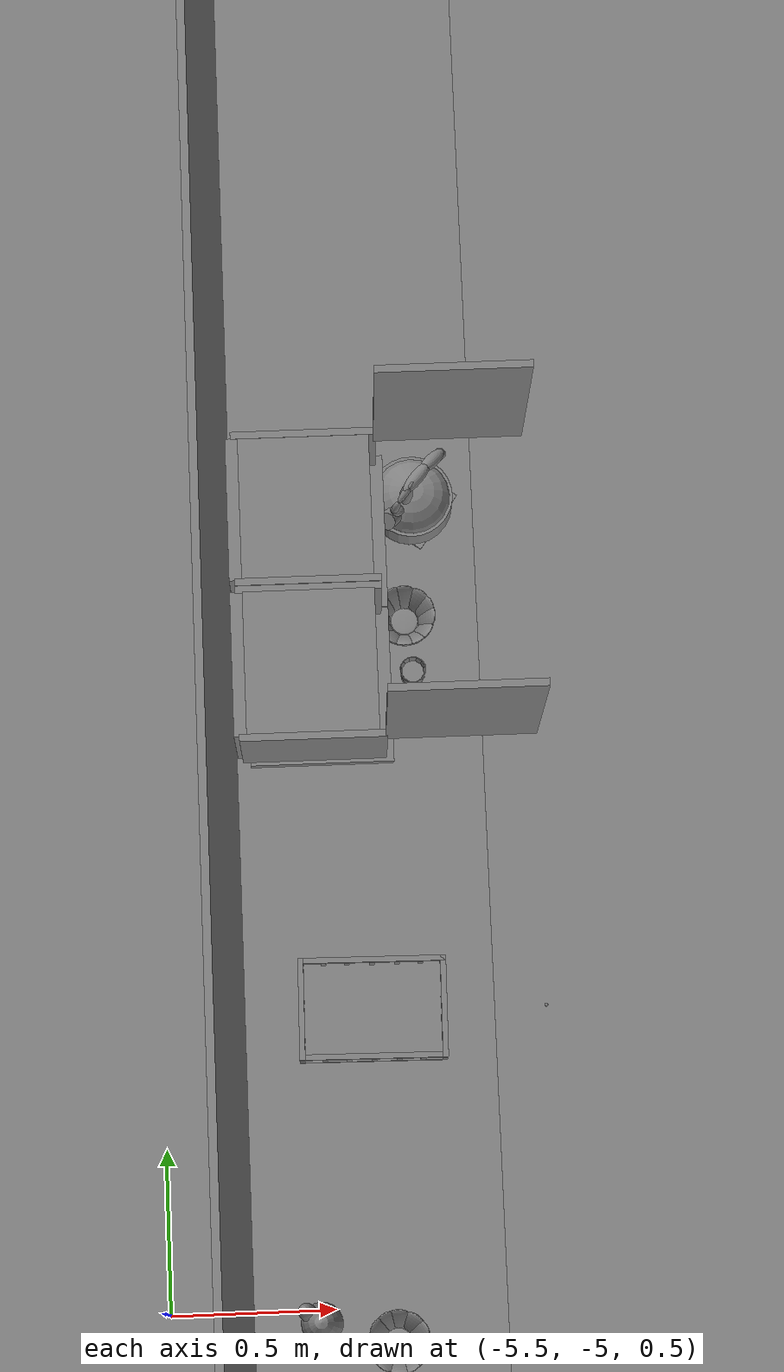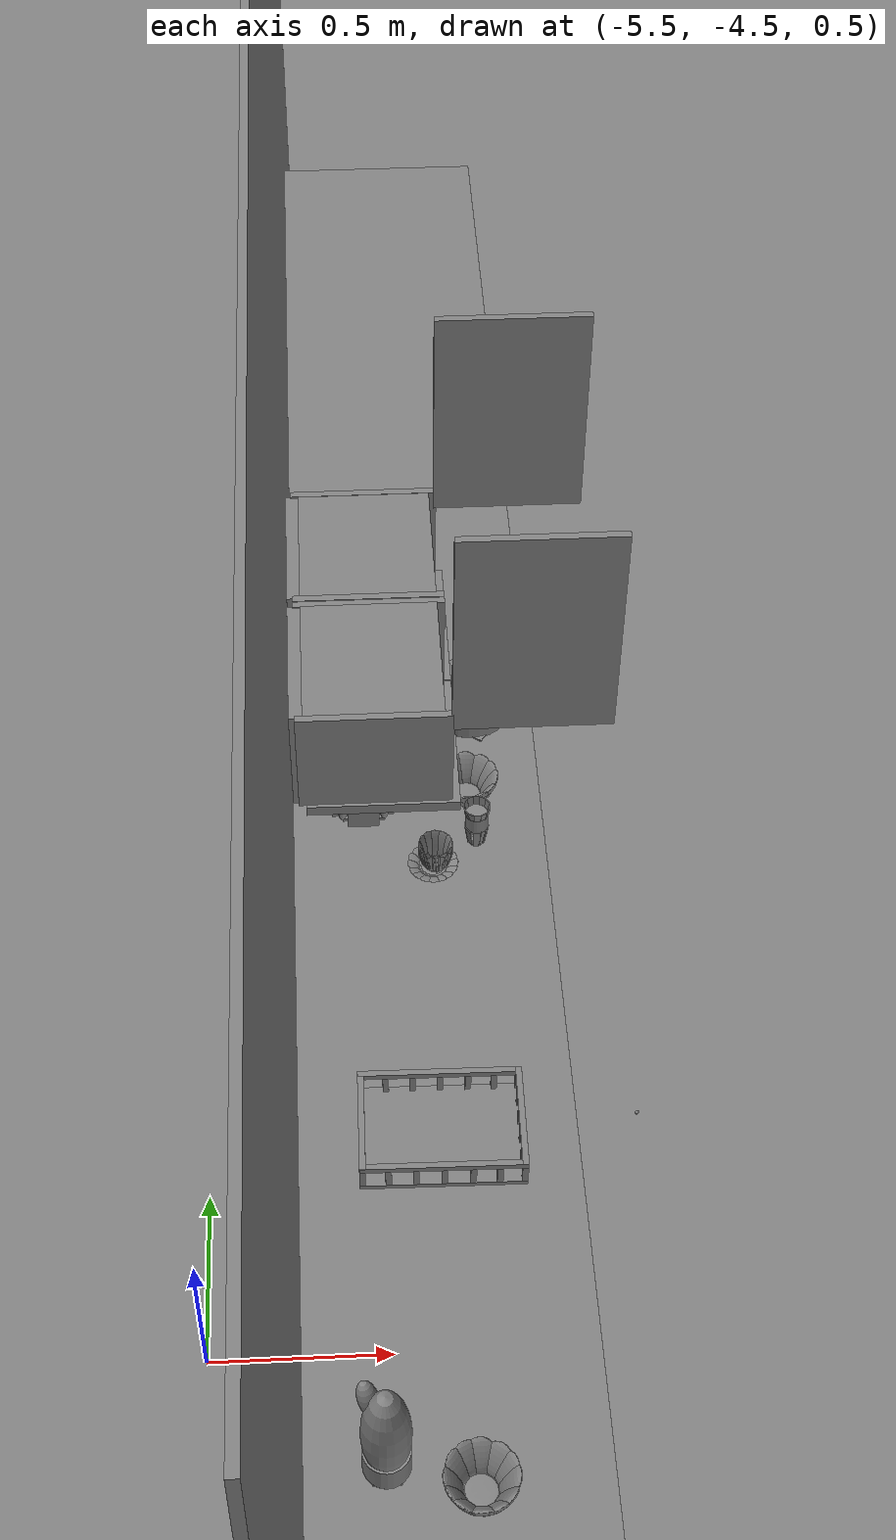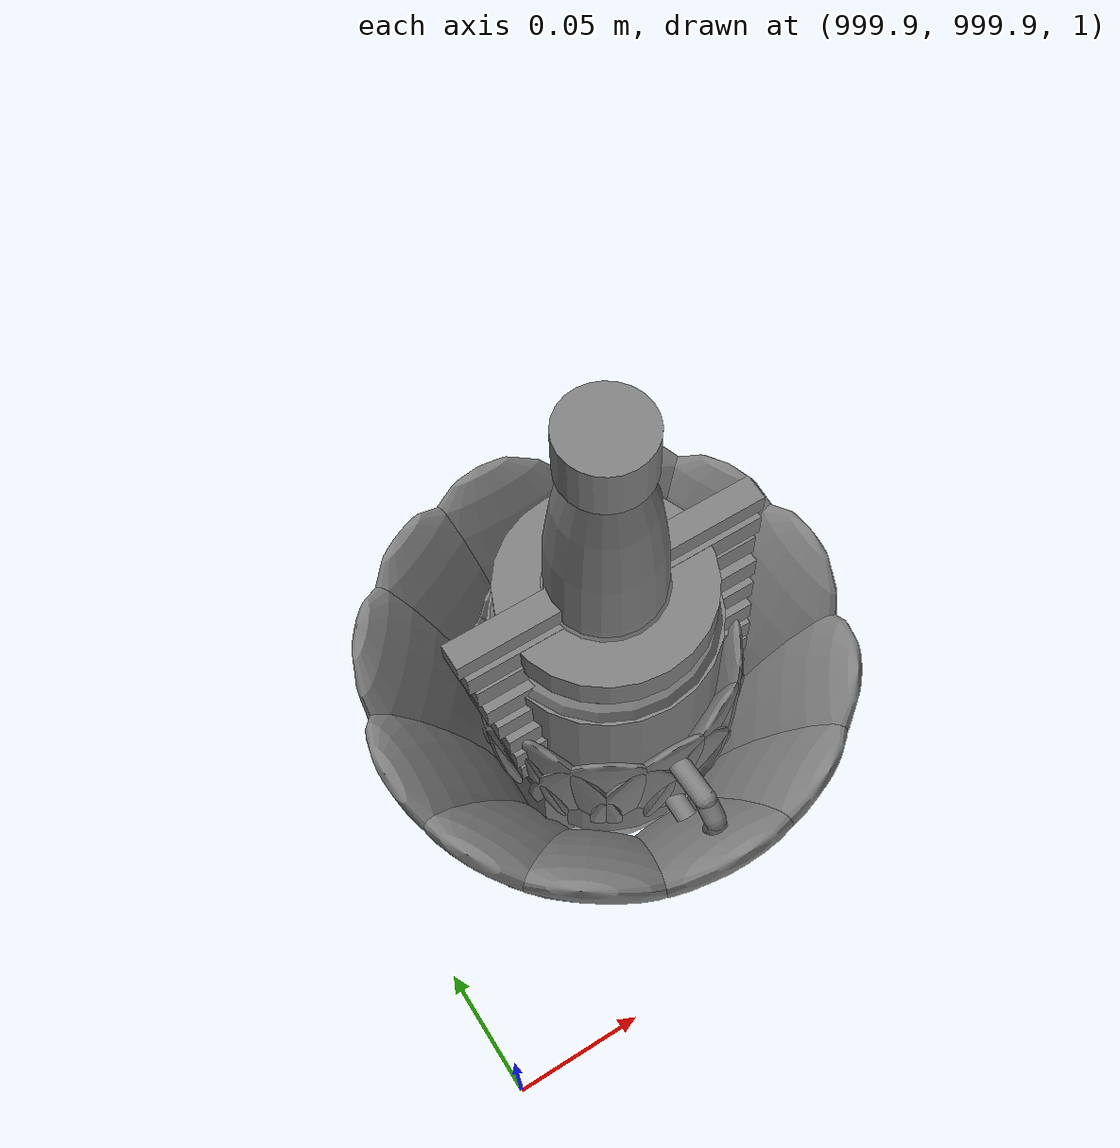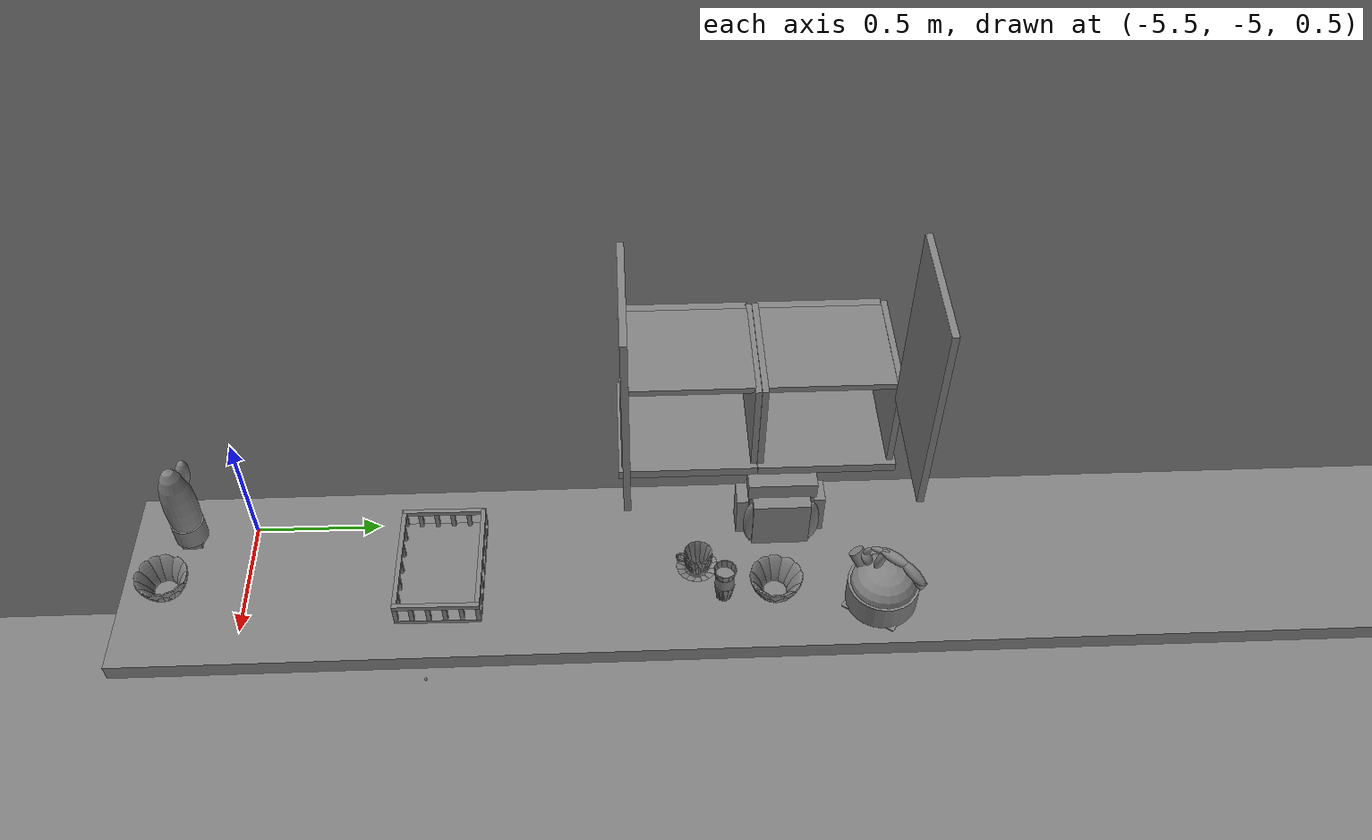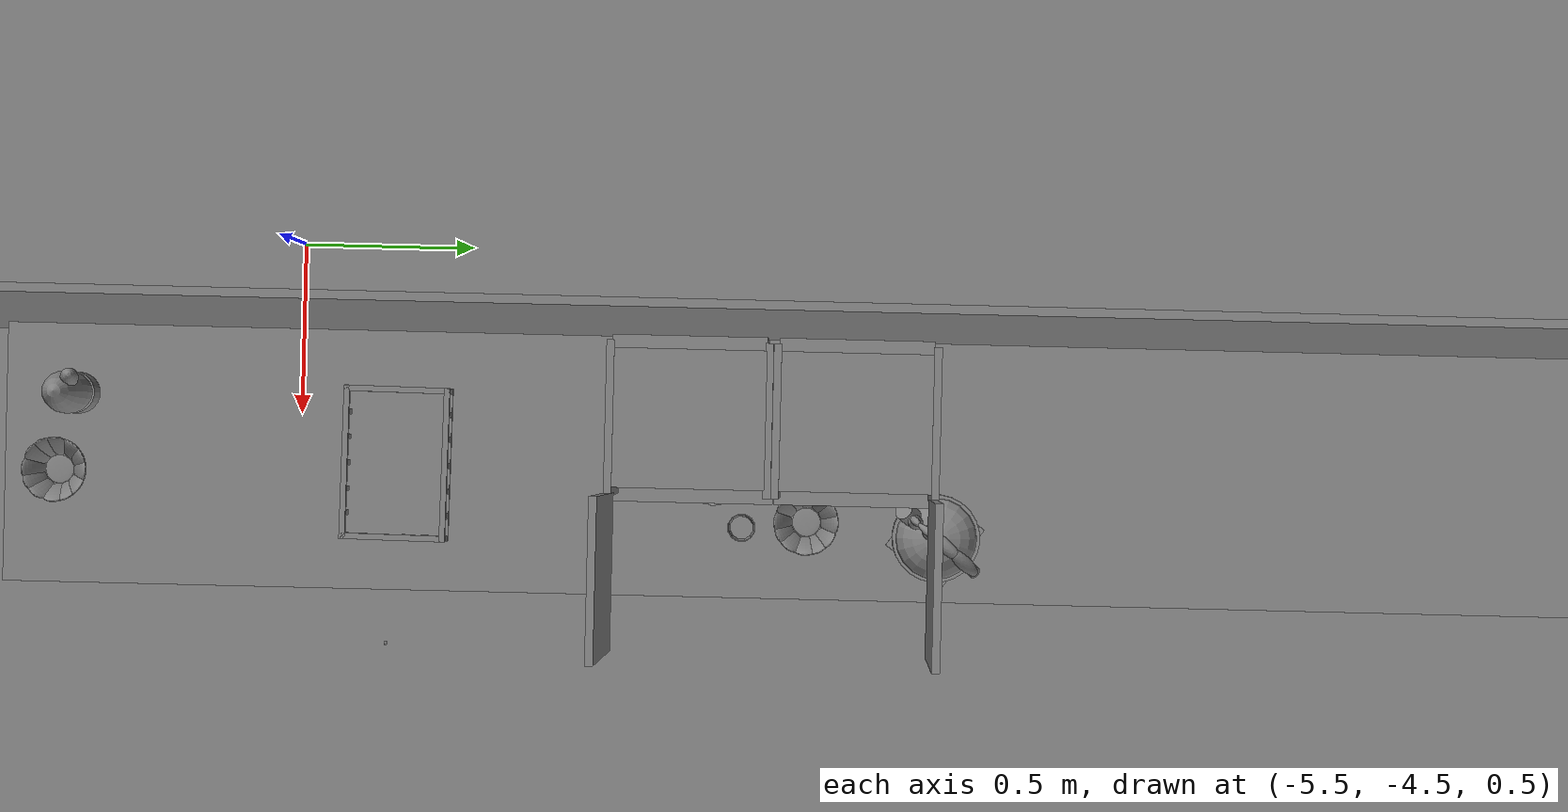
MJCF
<mujoco>
    <option gravity="0.000000000 0.000000000 -9.810000420" timestep="0.0049999999" integrator="implicitfast" density="9.8000002" viscosity="1.8000001e-05" noslip_iterations="10" iterations="100" sdf_iterations="50">
        <flag multiccd="disable"/>
    </option>
    <size memory="1000M"/>
    <compiler coordinate="local"/>
    <worldbody>
        <light cutoff="30" pos="0 1 1" dir="0 -1 -2"/>
        <light cutoff="30" pos="0 -1 1" dir="0 1 -2"/>
        <body pos="-5.046103477 -5.051773071 1.001502514" euler="0.000000000 0.000000000 0.000000000" name="Interactive Objcets_huapen">
            <geom contype="1" conaffinity="1" density="1000" type="ellipsoid" material="" rgba="0.500000000 0.500000000 0.500000000 1.000000000" solimp="0.899999976 0.949999988 0.001000000" friction="1.000000000 0.005000000 0.000100000" solref="0.020000000 1.000000000" margin="0" condim="3" group="0" pos="0.008062840 0.004346371 0.205056787" quat="1.000000000 0.000000000 0.000000000 0.000000000" size="0.059999999 0.059999999 0.180000007" name="Interactive Objcets_huapen_hua_CA230B5C_E439_47EF_BF2E_EA85F453C098"/>
            <geom contype="1" conaffinity="1" density="1000" type="cylinder" material="" rgba="0.500000000 0.500000000 0.500000000 1.000000000" solimp="0.899999976 0.949999988 0.001000000" friction="1.000000000 0.005000000 0.000100000" solref="0.020000000 1.000000000" margin="0" condim="3" group="0" pos="0.008062840 0.003952026 0.080107450" quat="1.000000000 0.000000000 0.000000000 0.000000000" size="0.057999998 0.039999999 1.000000000" name="Interactive Objcets_huapen_hua_EC6E0614_D3A0_4783_ABF2_923469C0131F"/>
            <geom contype="1" conaffinity="1" density="1000" type="box" material="" rgba="0.500000000 0.500000000 0.500000000 1.000000000" solimp="0.899999976 0.949999988 0.001000000" friction="1.000000000 0.005000000 0.000100000" solref="0.020000000 1.000000000" margin="0" condim="3" group="0" pos="0.008062840 0.003952503 0.020566106" quat="1.000000000 0.000000000 0.000000000 0.000000000" size="0.035000000 0.035000000 0.020000000" name="Interactive Objcets_huapen_hua_D8351165_553C_4AF8_83D4_E7A082E761E4"/>
            <geom contype="1" conaffinity="1" density="1000" type="ellipsoid" material="" rgba="0.500000000 0.500000000 0.500000000 1.000000000" solimp="0.899999976 0.949999988 0.001000000" friction="1.000000000 0.005000000 0.000100000" solref="0.020000000 1.000000000" margin="0" condim="3" group="0" pos="-0.029900074 0.033599377 0.321917295" quat="0.992658079 -0.083605267 -0.087364964 0.002748166" size="0.025000000 0.025000000 0.059999999" name="Interactive Objcets_huapen_hua_85511993_0FD4_43F2_AC2F_D584A6FFB42E"/>
            <freejoint name="Interactive Objcets_huapen"/>
        </body>
        <body pos="1000.000000000 1000.000000000 1.000000000" euler="0.000000000 0.000000000 0.000000000" name="openloong_gripper_2f85_fix_base_usda_jar_01">
            <geom contype="1" conaffinity="1" density="1000" type="box" material="" rgba="0.500000000 0.500000000 0.500000000 1.000000000" solimp="0.899999976 0.949999988 0.001000000" friction="1.000000000 0.005000000 0.000100000" solref="0.020000000 1.000000000" margin="0" condim="3" group="0" pos="0.000000000 0.000000000 0.006158113" quat="1.000000000 0.000000000 0.000000000 0.000000000" size="0.020000000 0.020000000 0.005000000" name="openloong_gripper_2f85_fix_base_usda_geom_2B643AEE_D01C_4173_8A10_A2A38D3D93FF"/>
            <geom contype="1" conaffinity="1" density="1000" type="cylinder" material="" rgba="0.500000000 0.500000000 0.500000000 1.000000000" solimp="0.899999976 0.949999988 0.001000000" friction="1.000000000 0.005000000 0.000100000" solref="0.020000000 1.000000000" margin="0" condim="3" group="0" pos="0.000000000 0.000000000 0.062744498" quat="1.000000000 0.000000000 0.000000000 0.000000000" size="0.041000001 0.052999999 1.000000000" name="openloong_gripper_2f85_fix_base_usda_geom_ABFB345F_480A_421B_969D_D6C6547A16A4"/>
            <geom contype="1" conaffinity="1" density="1000" type="ellipsoid" material="" rgba="0.500000000 0.500000000 0.500000000 1.000000000" solimp="0.899999976 0.949999988 0.001000000" friction="1.000000000 0.005000000 0.000100000" solref="0.020000000 1.000000000" margin="0" condim="3" group="0" pos="0.000000000 0.000000000 0.122252703" quat="1.000000000 0.000000000 0.000000000 0.000000000" size="0.035999998 0.035999998 0.010000000" name="openloong_gripper_2f85_fix_base_usda_geom_7E9E8E64_E4A1_46E3_A1E0_D04D471FF7F3"/>
            <geom contype="1" conaffinity="1" density="1000" type="cylinder" material="" rgba="0.500000000 0.500000000 0.500000000 1.000000000" solimp="0.899999976 0.949999988 0.001000000" friction="1.000000000 0.005000000 0.000100000" solref="0.020000000 1.000000000" margin="0" condim="3" group="0" pos="0.000000000 0.000000000 0.015747190" quat="1.000000000 0.000000000 0.000000000 0.000000000" size="0.035000000 0.010000000 1.000000000" name="openloong_gripper_2f85_fix_base_usda_geom_FFB44336_06E5_4BAE_A2FE_CD1E94C51BB0"/>
            <geom contype="1" conaffinity="1" density="1000" type="ellipsoid" material="" rgba="0.500000000 0.500000000 0.500000000 1.000000000" solimp="0.899999976 0.949999988 0.001000000" friction="1.000000000 0.005000000 0.000100000" solref="0.020000000 1.000000000" margin="0" condim="3" group="0" pos="0.000000000 0.000000000 0.115815401" quat="1.000000000 0.000000000 0.000000000 0.000000000" size="0.039999999 0.039999999 0.010000000" name="openloong_gripper_2f85_fix_base_usda_geom_E58B3DE2_9AB0_431C_B89F_006E173AFE48"/>
            <geom contype="1" conaffinity="1" density="1000" type="cylinder" material="" rgba="0.500000000 0.500000000 0.500000000 1.000000000" solimp="0.899999976 0.949999988 0.001000000" friction="1.000000000 0.005000000 0.000100000" solref="0.020000000 1.000000000" margin="0" condim="3" group="0" pos="0.000000000 0.000000000 0.133183479" quat="1.000000000 0.000000000 0.000000000 0.000000000" size="0.037999999 0.006500000 1.000000000" name="openloong_gripper_2f85_fix_base_usda_geom_018EE235_0B70_44DE_8909_63BB7B5C8AB7"/>
            <freejoint name="openloong_gripper_2f85_fix_base_usda_jar_01_joint"/>
            <site size="0.005000000 0.005000000 0.005000000" rgba="0.500000000 0.500000000 0.500000000 1.000000000" pos="0.000000000 0.000000000 0.000000000" quat="1.000000000 0.000000000 0.000000000 0.000000000" group="0" type="sphere" name="openloong_gripper_2f85_fix_base_usda_jar_01site"/>
        </body>
        <body pos="1000.000000000 1000.000000000 1.000000000" euler="0.000000000 0.000000000 0.000000000" name="openloong_gripper_2f85_fix_base_usda_salt">
            <geom contype="1" conaffinity="1" density="1000" type="box" material="" rgba="0.500000000 0.500000000 0.500000000 1.000000000" solimp="0.899999976 0.949999988 0.001000000" friction="1.000000000 0.005000000 0.000100000" solref="0.020000000 1.000000000" margin="0" condim="3" group="0" pos="0.000305176 0.000000000 0.084862232" quat="1.000000000 0.000000000 0.000000000 0.000000000" size="0.048999999 0.018999999 0.005000000" name="openloong_gripper_2f85_fix_base_usda_geom_DB9D9424_1D65_4623_A14A_A3319C41893E"/>
            <geom contype="1" conaffinity="1" density="1000" type="box" material="" rgba="0.500000000 0.500000000 0.500000000 1.000000000" solimp="0.899999976 0.949999988 0.001000000" friction="1.000000000 0.005000000 0.000100000" solref="0.020000000 1.000000000" margin="0" condim="3" group="0" pos="0.000305176 0.000000000 0.104564309" quat="1.000000000 0.000000000 0.000000000 0.000000000" size="0.052000001 0.014000000 0.005000000" name="openloong_gripper_2f85_fix_base_usda_geom_1869378B_0319_4403_A5E4_DC941EFD3177"/>
            <geom contype="1" conaffinity="1" density="1000" type="box" material="" rgba="0.500000000 0.500000000 0.500000000 1.000000000" solimp="0.899999976 0.949999988 0.001000000" friction="1.000000000 0.005000000 0.000100000" solref="0.020000000 1.000000000" margin="0" condim="3" group="0" pos="0.000305176 0.000000000 0.114487171" quat="1.000000000 0.000000000 0.000000000 0.000000000" size="0.054000001 0.011500000 0.005000000" name="openloong_gripper_2f85_fix_base_usda_geom_4D5CB6A1_E2A4_48FE_89F9_F702FA332E9E"/>
            <geom contype="1" conaffinity="1" density="1000" type="box" material="" rgba="0.500000000 0.500000000 0.500000000 1.000000000" solimp="0.899999976 0.949999988 0.001000000" friction="1.000000000 0.005000000 0.000100000" solref="0.020000000 1.000000000" margin="0" condim="3" group="0" pos="0.000305176 0.000000000 0.075103164" quat="1.000000000 0.000000000 0.000000000 0.000000000" size="0.048000000 0.020000000 0.005000000" name="openloong_gripper_2f85_fix_base_usda_geom_B4FAFF00_6C50_4E7C_A221_41CB6180B94E"/>
            <geom contype="1" conaffinity="1" density="1000" type="box" material="" rgba="0.500000000 0.500000000 0.500000000 1.000000000" solimp="0.899999976 0.949999988 0.001000000" friction="1.000000000 0.005000000 0.000100000" solref="0.020000000 1.000000000" margin="0" condim="3" group="0" pos="0.000305176 0.000000000 0.134892464" quat="1.000000000 0.000000000 0.000000000 0.000000000" size="0.057000000 0.007000000 0.005000000" name="openloong_gripper_2f85_fix_base_usda_geom_3B08BD14_9837_4D48_A707_AF0F14573976"/>
            <geom contype="1" conaffinity="1" density="1000" type="box" material="" rgba="0.500000000 0.500000000 0.500000000 1.000000000" solimp="0.899999976 0.949999988 0.001000000" friction="1.000000000 0.005000000 0.000100000" solref="0.020000000 1.000000000" margin="0" condim="3" group="0" pos="0.000305176 0.000000000 0.094920278" quat="1.000000000 0.000000000 0.000000000 0.000000000" size="0.050000001 0.017000001 0.005000000" name="openloong_gripper_2f85_fix_base_usda_geom_B5DFA9AB_7AD0_4260_83C5_F5C52323ACB9"/>
            <geom contype="1" conaffinity="1" density="1000" type="box" material="" rgba="0.500000000 0.500000000 0.500000000 1.000000000" solimp="0.899999976 0.949999988 0.001000000" friction="1.000000000 0.005000000 0.000100000" solref="0.020000000 1.000000000" margin="0" condim="3" group="0" pos="0.000305176 0.000000000 0.065204859" quat="1.000000000 0.000000000 0.000000000 0.000000000" size="0.045000002 0.021000000 0.005000000" name="openloong_gripper_2f85_fix_base_usda_geom_EC187882_B796_41B3_9D83_DCDF05295821"/>
            <geom contype="1" conaffinity="1" density="1000" type="box" material="" rgba="0.500000000 0.500000000 0.500000000 1.000000000" solimp="0.899999976 0.949999988 0.001000000" friction="1.000000000 0.005000000 0.000100000" solref="0.020000000 1.000000000" margin="0" condim="3" group="0" pos="0.000305176 0.000000000 0.144135714" quat="1.000000000 0.000000000 0.000000000 0.000000000" size="0.059000000 0.005000000 0.004000000" name="openloong_gripper_2f85_fix_base_usda_geom_56856D90_8EE9_4B94_B267_BC2F56793949"/>
            <geom contype="1" conaffinity="1" density="1000" type="box" material="" rgba="0.500000000 0.500000000 0.500000000 1.000000000" solimp="0.899999976 0.949999988 0.001000000" friction="1.000000000 0.005000000 0.000100000" solref="0.020000000 1.000000000" margin="0" condim="3" group="0" pos="0.000000000 0.000000000 0.031593561" quat="1.000000000 0.000000000 0.000000000 0.000000000" size="0.041999999 0.024000000 0.029999999" name="openloong_gripper_2f85_fix_base_usda_geom_43CC3473_8F16_4470_B118_8F5B6718A6DF"/>
            <geom contype="1" conaffinity="1" density="1000" type="box" material="" rgba="0.500000000 0.500000000 0.500000000 1.000000000" solimp="0.899999976 0.949999988 0.001000000" friction="1.000000000 0.005000000 0.000100000" solref="0.020000000 1.000000000" margin="0" condim="3" group="0" pos="0.000305176 0.000000000 0.124608755" quat="1.000000000 0.000000000 0.000000000 0.000000000" size="0.055000000 0.008000000 0.005000000" name="openloong_gripper_2f85_fix_base_usda_geom_892509B5_350E_4649_95C6_ED9AB532746F"/>
            <freejoint name="openloong_gripper_2f85_fix_base_usda_salt_joint"/>
            <site size="0.005000000 0.005000000 0.005000000" rgba="0.500000000 0.500000000 0.500000000 1.000000000" pos="0.000000000 0.000000000 0.000000000" quat="1.000000000 0.000000000 0.000000000 0.000000000" group="0" type="sphere" name="openloong_gripper_2f85_fix_base_usda_saltsite"/>
        </body>
        <body pos="1000.000000000 1000.000000000 1.000000000" euler="0.000000000 0.000000000 0.000000000" name="openloong_gripper_2f85_fix_base_usda_bow_yellow_kps">
            <geom contype="1" conaffinity="1" density="1000" type="ellipsoid" material="" rgba="0.500000000 0.500000000 0.500000000 1.000000000" solimp="0.899999976 0.949999988 0.001000000" friction="1.000000000 0.005000000 0.000100000" solref="0.020000000 1.000000000" margin="0" condim="3" group="0" pos="-0.052185059 0.040283203 0.044118762" quat="0.919264615 -0.076883033 -0.225593656 -0.313287765" size="0.010000000 0.039999999 0.052000001" name="openloong_gripper_2f85_fix_base_usda_geom_27447841_73A2_4E60_B85B_F03B4016B389"/>
            <geom contype="1" conaffinity="1" density="1000" type="ellipsoid" material="" rgba="0.500000000 0.500000000 0.500000000 1.000000000" solimp="0.899999976 0.949999988 0.001000000" friction="1.000000000 0.005000000 0.000100000" solref="0.020000000 1.000000000" margin="0" condim="3" group="0" pos="-0.000061035 0.065979004 0.044118762" quat="0.687598765 -0.168314874 -0.168741167 -0.685860336" size="0.010000000 0.039999999 0.052000001" name="openloong_gripper_2f85_fix_base_usda_geom_6A56726F_7757_4E93_9D06_1005752E54E2"/>
            <geom contype="1" conaffinity="1" density="1000" type="box" material="" rgba="0.500000000 0.500000000 0.500000000 1.000000000" solimp="0.899999976 0.949999988 0.001000000" friction="1.000000000 0.005000000 0.000100000" solref="0.020000000 1.000000000" margin="0" condim="3" group="0" pos="0.000061035 0.000000000 -0.002001643" quat="1.000000000 0.000000000 0.000000000 0.000000000" size="0.029999999 0.029999999 0.002000000" name="openloong_gripper_2f85_fix_base_usda_geom_70F6DAC6_C39F_4BD4_B470_CA22EEED396B"/>
            <geom contype="1" conaffinity="1" density="1000" type="ellipsoid" material="" rgba="0.500000000 0.500000000 0.500000000 1.000000000" solimp="0.899999976 0.949999988 0.001000000" friction="1.000000000 0.005000000 0.000100000" solref="0.020000000 1.000000000" margin="0" condim="3" group="0" pos="0.029418945 -0.059082031 0.044118762" quat="0.825555861 0.125530601 0.202597082 -0.511521280" size="0.010000000 0.039999999 0.052000001" name="openloong_gripper_2f85_fix_base_usda_geom_A295D3FD_ACBD_4663_8718_CA43AE808604"/>
            <geom contype="1" conaffinity="1" density="1000" type="ellipsoid" material="" rgba="0.500000000 0.500000000 0.500000000 1.000000000" solimp="0.899999976 0.949999988 0.001000000" friction="1.000000000 0.005000000 0.000100000" solref="0.020000000 1.000000000" margin="0" condim="3" group="0" pos="0.000244141 -0.065979004 0.044118762" quat="0.687598765 0.168314651 0.168741375 -0.685860336" size="0.010000000 0.039999999 0.052000001" name="openloong_gripper_2f85_fix_base_usda_geom_F7538A7A_3716_45EA_80F5_43E3A50CBB08"/>
            <geom contype="1" conaffinity="1" density="1000" type="ellipsoid" material="" rgba="0.500000000 0.500000000 0.500000000 1.000000000" solimp="0.899999976 0.949999988 0.001000000" friction="1.000000000 0.005000000 0.000100000" solref="0.020000000 1.000000000" margin="0" condim="3" group="0" pos="0.000061035 0.000000000 0.000446677" quat="1.000000000 0.000000000 0.000000000 0.000000000" size="0.039999999 0.039999999 0.002000000" name="openloong_gripper_2f85_fix_base_usda_geom_9CB3B368_0D59_4FB0_875D_FF4E381F75B8"/>
            <geom contype="1" conaffinity="1" density="1000" type="ellipsoid" material="" rgba="0.500000000 0.500000000 0.500000000 1.000000000" solimp="0.899999976 0.949999988 0.001000000" friction="1.000000000 0.005000000 0.000100000" solref="0.020000000 1.000000000" margin="0" condim="3" group="0" pos="0.059082031 0.029541016 0.044118762" quat="0.223252773 -0.231952220 -0.054787423 -0.945174456" size="0.010000000 0.039999999 0.052000001" name="openloong_gripper_2f85_fix_base_usda_geom_14345D7E_4C3E_46CE_8C0D_DF1C04E899C1"/>
            <geom contype="1" conaffinity="1" density="1000" type="ellipsoid" material="" rgba="0.500000000 0.500000000 0.500000000 1.000000000" solimp="0.899999976 0.949999988 0.001000000" friction="1.000000000 0.005000000 0.000100000" solref="0.020000000 1.000000000" margin="0" condim="3" group="0" pos="0.000061035 0.000000000 0.007335305" quat="1.000000000 0.000000000 0.000000000 0.000000000" size="0.039999999 0.039999999 0.002000000" name="openloong_gripper_2f85_fix_base_usda_geom_6CE3D758_A33C_4452_8F97_D2DA93491809"/>
            <geom contype="1" conaffinity="1" density="1000" type="ellipsoid" material="" rgba="0.500000000 0.500000000 0.500000000 1.000000000" solimp="0.899999976 0.949999988 0.001000000" friction="1.000000000 0.005000000 0.000100000" solref="0.020000000 1.000000000" margin="0" condim="3" group="0" pos="-0.029296875 0.059082031 0.044118762" quat="0.825555861 -0.125530809 -0.202596918 -0.511521280" size="0.010000000 0.039999999 0.052000001" name="openloong_gripper_2f85_fix_base_usda_geom_A4B6CEC5_9048_40AE_BC4F_168E70D49525"/>
            <geom contype="1" conaffinity="1" density="1000" type="ellipsoid" material="" rgba="0.500000000 0.500000000 0.500000000 1.000000000" solimp="0.899999976 0.949999988 0.001000000" friction="1.000000000 0.005000000 0.000100000" solref="0.020000000 1.000000000" margin="0" condim="3" group="0" pos="0.040222168 0.052368164 0.044118762" quat="0.429593176 -0.213750049 -0.105424821 -0.871002972" size="0.010000000 0.039999999 0.052000001" name="openloong_gripper_2f85_fix_base_usda_geom_D646EAF5_6E85_475A_AAF8_4A5C5A31E344"/>
            <geom contype="1" conaffinity="1" density="1000" type="ellipsoid" material="" rgba="0.500000000 0.500000000 0.500000000 1.000000000" solimp="0.899999976 0.949999988 0.001000000" friction="1.000000000 0.005000000 0.000100000" solref="0.020000000 1.000000000" margin="0" condim="3" group="0" pos="0.066040039 0.000000000 0.044118762" quat="0.971183062 -0.000000156 0.238334835 0.000000030" size="0.010000000 0.039999999 0.052000001" name="openloong_gripper_2f85_fix_base_usda_geom_001B91DE_9485_47A9_8AD6_7FC77309947A"/>
            <geom contype="1" conaffinity="1" density="1000" type="ellipsoid" material="" rgba="0.500000000 0.500000000 0.500000000 1.000000000" solimp="0.899999976 0.949999988 0.001000000" friction="1.000000000 0.005000000 0.000100000" solref="0.020000000 1.000000000" margin="0" condim="3" group="0" pos="0.052307129 -0.040283203 0.044118762" quat="0.919264674 0.076882750 0.225593731 -0.313287705" size="0.010000000 0.039999999 0.052000001" name="openloong_gripper_2f85_fix_base_usda_geom_A5B07B4F_9AD4_4F44_B14A_54183230EC4B"/>
            <geom contype="1" conaffinity="1" density="1000" type="ellipsoid" material="" rgba="0.500000000 0.500000000 0.500000000 1.000000000" solimp="0.899999976 0.949999988 0.001000000" friction="1.000000000 0.005000000 0.000100000" solref="0.020000000 1.000000000" margin="0" condim="3" group="0" pos="-0.065917969 0.000000000 0.044118762" quat="0.971183062 -0.000000142 -0.238334835 0.000000030" size="0.010000000 0.039999999 0.052000001" name="openloong_gripper_2f85_fix_base_usda_geom_243F7C46_816E_495E_AD9C_7C9DB0BD93D0"/>
            <geom contype="1" conaffinity="1" density="1000" type="ellipsoid" material="" rgba="0.500000000 0.500000000 0.500000000 1.000000000" solimp="0.899999976 0.949999988 0.001000000" friction="1.000000000 0.005000000 0.000100000" solref="0.020000000 1.000000000" margin="0" condim="3" group="0" pos="-0.058898926 -0.029541016 0.044118762" quat="0.223252758 0.231952101 0.054787733 -0.945174575" size="0.010000000 0.039999999 0.052000001" name="openloong_gripper_2f85_fix_base_usda_geom_1F7BD150_7D83_4096_BCDD_843D666965DD"/>
            <geom contype="1" conaffinity="1" density="1000" type="ellipsoid" material="" rgba="0.500000000 0.500000000 0.500000000 1.000000000" solimp="0.899999976 0.949999988 0.001000000" friction="1.000000000 0.005000000 0.000100000" solref="0.020000000 1.000000000" margin="0" condim="3" group="0" pos="-0.040100098 -0.052368164 0.044118762" quat="0.429593235 0.213749886 0.105425082 -0.871003032" size="0.010000000 0.039999999 0.052000001" name="openloong_gripper_2f85_fix_base_usda_geom_EA50C3B0_4FC8_4B81_8D0D_FC5ABFEF732C"/>
            <freejoint name="openloong_gripper_2f85_fix_base_usda_bow_yellow_kps_joint"/>
            <site size="0.005000000 0.005000000 0.005000000" rgba="0.500000000 0.500000000 0.500000000 1.000000000" pos="0.000000000 0.000000000 0.000000000" quat="0.999961913 0.008726534 0.000000000 0.000000000" group="0" type="sphere" name="openloong_gripper_2f85_fix_base_usda_bow_yellow_kps"/>
        </body>
        <body pos="-4.486755848 -3.775493383 1.820592403" euler="-64.611572266 80.439056396 41.402622223" mocap="true" name="spotlight2_SpotLight"/>
        <body pos="-4.285274029 -4.113828659 1.810731173" euler="-85.412658691 64.819107056 -64.811126709" mocap="true" name="spotlight5_SpotLight"/>
        <body pos="1000.000000000 1000.000000000 1.000000000" euler="0.000000000 0.000000000 0.000000000" name="openloong_gripper_2f85_fix_base_usda_coffeecup_white_kps">
            <geom contype="1" conaffinity="1" density="1000" type="capsule" material="" rgba="0.500000000 0.500000000 0.500000000 1.000000000" solimp="0.899999976 0.949999988 0.001000000" friction="1.000000000 0.005000000 0.000100000" solref="0.020000000 1.000000000" margin="0" condim="3" group="0" pos="-0.000854492 -0.065795898 0.050029993" quat="0.343559504 -0.613204718 0.626912475 0.336047262" size="0.004000000 0.005000000 1.000000000" name="openloong_gripper_2f85_fix_base_usda_geom_F3B72CD5_7350_456D_B56B_953B0370D4E6"/>
            <geom contype="1" conaffinity="1" density="1000" type="ellipsoid" material="" rgba="0.500000000 0.500000000 0.500000000 1.000000000" solimp="0.899999976 0.949999988 0.001000000" friction="1.000000000 0.005000000 0.000100000" solref="0.020000000 1.000000000" margin="0" condim="3" group="0" pos="-0.000793457 -0.038452148 0.048040152" quat="0.711656272 0.066323131 -0.067805752 0.696095467" size="0.005000000 0.029999999 0.048999999" name="openloong_gripper_2f85_fix_base_usda_geom_63F1F3A9_EAB3_419B_B7E5_2374D4246C84"/>
            <geom contype="1" conaffinity="1" density="1000" type="ellipsoid" material="" rgba="0.500000000 0.500000000 0.500000000 1.000000000" solimp="0.899999976 0.949999988 0.001000000" friction="1.000000000 0.005000000 0.000100000" solref="0.020000000 1.000000000" margin="0" condim="3" group="0" pos="0.037719727 -0.001892090 0.048040152" quat="0.995387912 0.001371633 0.094835162 -0.014391154" size="0.005000000 0.029999999 0.048999999" name="openloong_gripper_2f85_fix_base_usda_geom_17AA249D_8F21_45BF_99CB_E18210F8BCCE"/>
            <geom contype="1" conaffinity="1" density="1000" type="ellipsoid" material="" rgba="0.500000000 0.500000000 0.500000000 1.000000000" solimp="0.899999976 0.949999988 0.001000000" friction="1.000000000 0.005000000 0.000100000" solref="0.020000000 1.000000000" margin="0" condim="3" group="0" pos="0.033996582 0.015502930 0.048040152" quat="0.970659733 -0.021051638 0.092478797 0.220962167" size="0.005000000 0.029999999 0.048999999" name="openloong_gripper_2f85_fix_base_usda_geom_E6D67133_F70F_40CD_B86D_7C7C2404FE7B"/>
            <geom contype="1" conaffinity="1" density="1000" type="box" material="" rgba="0.500000000 0.500000000 0.500000000 1.000000000" solimp="0.899999976 0.949999988 0.001000000" friction="1.000000000 0.005000000 0.000100000" solref="0.020000000 1.000000000" margin="0" condim="3" group="0" pos="0.000793457 -0.000183105 0.000156164" quat="0.714879215 0.000000000 0.000000000 0.699247897" size="0.020000000 0.020000000 0.002000000" name="openloong_gripper_2f85_fix_base_usda_geom_B02E59DF_704A_473C_9D56_3255F4C0AF50"/>
            <geom contype="1" conaffinity="1" density="1000" type="ellipsoid" material="" rgba="0.500000000 0.500000000 0.500000000 1.000000000" solimp="0.899999976 0.949999988 0.001000000" friction="1.000000000 0.005000000 0.000100000" solref="0.020000000 1.000000000" margin="0" condim="3" group="0" pos="-0.019409180 -0.033081055 0.048040152" quat="0.866879702 0.046630561 -0.082595348 0.489411235" size="0.005000000 0.029999999 0.048999999" name="openloong_gripper_2f85_fix_base_usda_geom_CCEB1F5D_DCF0_4D15_A890_D637DF528050"/>
            <geom contype="1" conaffinity="1" density="1000" type="ellipsoid" material="" rgba="0.500000000 0.500000000 0.500000000 1.000000000" solimp="0.899999976 0.949999988 0.001000000" friction="1.000000000 0.005000000 0.000100000" solref="0.020000000 1.000000000" margin="0" condim="3" group="0" pos="-0.016052246 0.033264160 0.048040152" quat="0.840792537 -0.050782297 -0.080109790 -0.532983541" size="0.005000000 0.029999999 0.048999999" name="openloong_gripper_2f85_fix_base_usda_geom_C206ADAC_CFC5_4AE1_80B4_A63A14A48461"/>
            <geom contype="1" conaffinity="1" density="1000" type="capsule" material="" rgba="0.500000000 0.500000000 0.500000000 1.000000000" solimp="0.899999976 0.949999988 0.001000000" friction="1.000000000 0.005000000 0.000100000" solref="0.020000000 1.000000000" margin="0" condim="3" group="0" pos="-0.000549316 -0.053527832 0.046825886" quat="0.505496025 -0.494442940 0.505495846 0.494442940" size="0.004000000 0.005000000 1.000000000" name="openloong_gripper_2f85_fix_base_usda_geom_DB51D461_CD9B_43E0_8375_ACA7A9B6C1B7"/>
            <geom contype="1" conaffinity="1" density="1000" type="ellipsoid" material="" rgba="0.500000000 0.500000000 0.500000000 1.000000000" solimp="0.899999976 0.949999988 0.001000000" friction="1.000000000 0.005000000 0.000100000" solref="0.020000000 1.000000000" margin="0" condim="3" group="0" pos="-0.032104492 0.018920898 0.048040152" quat="0.958129764 -0.025742561 -0.091288343 -0.270168930" size="0.005000000 0.029999999 0.048999999" name="openloong_gripper_2f85_fix_base_usda_geom_9AE23B74_3AF3_40AA_A280_BEC7D402C93C"/>
            <geom contype="1" conaffinity="1" density="1000" type="ellipsoid" material="" rgba="0.500000000 0.500000000 0.500000000 1.000000000" solimp="0.899999976 0.949999988 0.001000000" friction="1.000000000 0.005000000 0.000100000" solref="0.020000000 1.000000000" margin="0" condim="3" group="0" pos="-0.037597656 0.000305176 0.048040152" quat="0.995387554 -0.001371440 -0.094839431 -0.014389008" size="0.005000000 0.029999999 0.048999999" name="openloong_gripper_2f85_fix_base_usda_geom_961F16E5_9D41_4ACF_9924_6A3B9ECAEA3F"/>
            <geom contype="1" conaffinity="1" density="1000" type="capsule" material="" rgba="0.500000000 0.500000000 0.500000000 1.000000000" solimp="0.899999976 0.949999988 0.001000000" friction="1.000000000 0.005000000 0.000100000" solref="0.020000000 1.000000000" margin="0" condim="3" group="0" pos="-0.000366211 -0.043762207 0.044118762" quat="0.260488123 -0.651174724 0.665731549 0.254792154" size="0.004000000 0.003000000 1.000000000" name="openloong_gripper_2f85_fix_base_usda_geom_4970B9DE_0771_4DA9_A8F2_CCE0C3501042"/>
            <geom contype="1" conaffinity="1" density="1000" type="capsule" material="" rgba="0.500000000 0.500000000 0.500000000 1.000000000" solimp="0.899999976 0.949999988 0.001000000" friction="1.000000000 0.005000000 0.000100000" solref="0.020000000 1.000000000" margin="0" condim="3" group="0" pos="-0.000915527 -0.068542480 0.082936406" quat="0.624995589 -0.339446366 0.347034454 0.611329615" size="0.004000000 0.004000000 1.000000000" name="openloong_gripper_2f85_fix_base_usda_geom_F460BA93_A40A_4C39_A290_6DC0D39C2FCF"/>
            <geom contype="1" conaffinity="1" density="1000" type="ellipsoid" material="" rgba="0.500000000 0.500000000 0.500000000 1.000000000" solimp="0.899999976 0.949999988 0.001000000" friction="1.000000000 0.005000000 0.000100000" solref="0.020000000 1.000000000" margin="0" condim="3" group="0" pos="0.016113281 -0.034851074 0.048040152" quat="0.840793252 0.050779939 0.080106191 -0.532983422" size="0.005000000 0.029999999 0.048999999" name="openloong_gripper_2f85_fix_base_usda_geom_BCA5D6E7_4FC3_4223_8097_4DAABCA23E4D"/>
            <geom contype="1" conaffinity="1" density="1000" type="ellipsoid" material="" rgba="0.500000000 0.500000000 0.500000000 1.000000000" solimp="0.899999976 0.949999988 0.001000000" friction="1.000000000 0.005000000 0.000100000" solref="0.020000000 1.000000000" margin="0" condim="3" group="0" pos="0.000854492 0.036865234 0.048040152" quat="0.711656570 -0.066320375 0.067802906 0.696095705" size="0.005000000 0.029999999 0.048999999" name="openloong_gripper_2f85_fix_base_usda_geom_3D9AE105_D89C_433E_B420_2FAE33AD90EF"/>
            <geom contype="1" conaffinity="1" density="1000" type="ellipsoid" material="" rgba="0.500000000 0.500000000 0.500000000 1.000000000" solimp="0.899999976 0.949999988 0.001000000" friction="1.000000000 0.005000000 0.000100000" solref="0.020000000 1.000000000" margin="0" condim="3" group="0" pos="-0.033935547 -0.017089844 0.048040152" quat="0.970659137 0.021052625 -0.092483103 0.220962465" size="0.005000000 0.029999999 0.048999999" name="openloong_gripper_2f85_fix_base_usda_geom_56164B48_04EC_4A14_B743_9333D354D994"/>
            <geom contype="1" conaffinity="1" density="1000" type="ellipsoid" material="" rgba="0.500000000 0.500000000 0.500000000 1.000000000" solimp="0.899999976 0.949999988 0.001000000" friction="1.000000000 0.005000000 0.000100000" solref="0.020000000 1.000000000" margin="0" condim="3" group="0" pos="0.019531250 0.031494141 0.048040152" quat="0.866880119 -0.046628602 0.082591817 0.489411235" size="0.005000000 0.029999999 0.048999999" name="openloong_gripper_2f85_fix_base_usda_geom_5E49DF2D_5B56_4DF0_B68D_15F648F146EA"/>
            <geom contype="1" conaffinity="1" density="1000" type="ellipsoid" material="" rgba="0.500000000 0.500000000 0.500000000 1.000000000" solimp="0.899999976 0.949999988 0.001000000" friction="1.000000000 0.005000000 0.000100000" solref="0.020000000 1.000000000" margin="0" condim="3" group="0" pos="0.032165527 -0.020507812 0.048040152" quat="0.958128154 0.025740955 0.091285400 -0.270175666" size="0.005000000 0.029999999 0.048999999" name="openloong_gripper_2f85_fix_base_usda_geom_34CC4087_E38F_4456_899D_C311D89FBD9B"/>
            <geom contype="1" conaffinity="1" density="1000" type="capsule" material="" rgba="0.500000000 0.500000000 0.500000000 1.000000000" solimp="0.899999976 0.949999988 0.001000000" friction="1.000000000 0.005000000 0.000100000" solref="0.020000000 1.000000000" margin="0" condim="3" group="0" pos="-0.000610352 -0.056823730 0.083572865" quat="0.452654332 -0.541215360 0.553313971 0.442756712" size="0.004000000 0.009000000 1.000000000" name="openloong_gripper_2f85_fix_base_usda_geom_4CDBC6D1_7CEC_4A6B_91F2_A8BB2CF6150D"/>
            <geom contype="1" conaffinity="1" density="1000" type="ellipsoid" material="" rgba="0.500000000 0.500000000 0.500000000 1.000000000" solimp="0.899999976 0.949999988 0.001000000" friction="1.000000000 0.005000000 0.000100000" solref="0.020000000 1.000000000" margin="0" condim="3" group="0" pos="0.000061035 -0.000183105 0.001848221" quat="0.714879215 0.000000000 0.000000000 0.699247897" size="0.029999999 0.029999999 0.001000000" name="openloong_gripper_2f85_fix_base_usda_geom_577E9C6C_8842_458B_8089_45162BF89C5B"/>
            <geom contype="1" conaffinity="1" density="1000" type="capsule" material="" rgba="0.500000000 0.500000000 0.500000000 1.000000000" solimp="0.899999976 0.949999988 0.001000000" friction="1.000000000 0.005000000 0.000100000" solref="0.020000000 1.000000000" margin="0" condim="3" group="0" pos="-0.000976562 -0.071838379 0.066101432" quat="0.031849027 -0.698553741 0.714169443 0.031152546" size="0.004000000 0.012000000 1.000000000" name="openloong_gripper_2f85_fix_base_usda_geom_230C3E07_4462_4F01_BA59_9913584814AD"/>
            <freejoint name="openloong_gripper_2f85_fix_base_usda_coffeecup_white_kps_joint"/>
            <site size="0.005000000 0.005000000 0.005000000" rgba="0.500000000 0.500000000 0.500000000 1.000000000" pos="0.000000000 0.000000000 0.000000000" quat="0.999961913 0.008726534 0.000000000 0.000000000" group="0" type="sphere" name="openloong_gripper_2f85_fix_base_usda_coffeecup_white_kps"/>
        </body>
        <body pos="-4.384322643 -3.929530382 1.774594665" euler="65.162246704 -44.738220215 61.408962250" mocap="true" name="spotlight4_SpotLight"/>
        <body pos="1000.000000000 1000.000000000 1.000000000" euler="0.000000000 0.000000000 0.000000000" name="openloong_gripper_2f85_fix_base_usda_bottle_red">
            <geom contype="1" conaffinity="1" density="1000" type="ellipsoid" material="" rgba="0.500000000 0.500000000 0.500000000 1.000000000" solimp="0.899999976 0.949999988 0.001000000" friction="1.000000000 0.005000000 0.000100000" solref="0.020000000 1.000000000" margin="0" condim="3" group="0" pos="0.000000000 0.000000000 0.144284487" quat="1.000000000 0.000000000 0.000000000 0.000000000" size="0.021000000 0.021000000 0.079999998" name="openloong_gripper_2f85_fix_base_usda_geom_57D52AFC_6A4C_4EAB_9AE7_F57EE8B68F6B"/>
            <geom contype="1" conaffinity="1" density="1000" type="cylinder" material="" rgba="0.500000000 0.500000000 0.500000000 1.000000000" solimp="0.899999976 0.949999988 0.001000000" friction="1.000000000 0.005000000 0.000100000" solref="0.020000000 1.000000000" margin="0" condim="3" group="0" pos="0.000000000 0.000000000 0.220618963" quat="1.000000000 0.000000000 0.000000000 0.000000000" size="0.016000001 0.010000000 1.000000000" name="openloong_gripper_2f85_fix_base_usda_geom_00BD2E68_C05E_4019_BA5D_198577090033"/>
            <geom contype="1" conaffinity="1" density="1000" type="ellipsoid" material="" rgba="0.500000000 0.500000000 0.500000000 1.000000000" solimp="0.899999976 0.949999988 0.001000000" friction="1.000000000 0.005000000 0.000100000" solref="0.020000000 1.000000000" margin="0" condim="3" group="0" pos="0.000000000 0.000000000 0.118945479" quat="1.000000000 0.000000000 0.000000000 0.000000000" size="0.030999999 0.030999999 0.029999999" name="openloong_gripper_2f85_fix_base_usda_geom_EB458DBD_262B_4A2C_8315_0B3C1DE41A86"/>
            <geom contype="1" conaffinity="1" density="1000" type="box" material="" rgba="0.500000000 0.500000000 0.500000000 1.000000000" solimp="0.899999976 0.949999988 0.001000000" friction="1.000000000 0.005000000 0.000100000" solref="0.020000000 1.000000000" margin="0" condim="3" group="0" pos="0.000000000 0.000000000 0.002189159" quat="1.000000000 0.000000000 0.000000000 0.000000000" size="0.020000000 0.020000000 0.003000000" name="openloong_gripper_2f85_fix_base_usda_geom_AB05ECA3_B273_4C7C_AE47_797BF9AD1F5A"/>
            <geom contype="1" conaffinity="1" density="1000" type="cylinder" material="" rgba="0.500000000 0.500000000 0.500000000 1.000000000" solimp="0.899999976 0.949999988 0.001000000" friction="1.000000000 0.005000000 0.000100000" solref="0.020000000 1.000000000" margin="0" condim="3" group="0" pos="0.000000000 -0.000366211 0.060884237" quat="1.000000000 0.000000000 0.000000000 0.000000000" size="0.030999999 0.057999998 1.000000000" name="openloong_gripper_2f85_fix_base_usda_geom_DF40AAA9_499B_4162_80B8_BC87CE4C099A"/>
            <freejoint name="openloong_gripper_2f85_fix_base_usda_bottle_red_joint"/>
            <site size="0.005000000 0.005000000 0.005000000" rgba="0.500000000 0.500000000 0.500000000 1.000000000" pos="0.000000000 0.000000000 0.000000000" quat="0.999961913 0.008726535 0.000000000 0.000000000" group="0" type="sphere" name="openloong_gripper_2f85_fix_base_usda_bottle_redsite"/>
        </body>
        <body pos="0.000000000 0.000000000 0.000000000" euler="0.000000000 0.000000000 0.000000000" name="Static Objcets_Static Objcets">
            <geom contype="1" conaffinity="1" density="1000" type="box" material="" rgba="0.500000000 0.500000000 0.500000000 1.000000000" solimp="0.899999976 0.949999988 0.001000000" friction="1.000000000 0.005000000 0.000100000" solref="0.020000000 1.000000000" margin="0" condim="3" group="0" pos="-4.999745846 -3.497932911 1.764780521" quat="0.707107067 0.707106471 0.000000000 0.000000000" size="0.200000003 0.159999996 0.010000000" name="Static Objcets_geom_2005B665_EAAE_465A_99CA_E627EA84D01A"/>
            <geom contype="1" conaffinity="1" density="1000" type="box" material="" rgba="0.500000000 0.500000000 0.500000000 1.000000000" solimp="0.899999976 0.949999988 0.001000000" friction="1.000000000 0.005000000 0.000100000" solref="0.020000000 1.000000000" margin="0" condim="3" group="0" pos="-4.979488373 -3.297635794 1.591412544" quat="0.707106829 0.707106709 0.000000000 0.000000000" size="0.200000003 0.015000000 0.219999999" name="Static Objcets_geom_1CA0AD38_C35C_404E_B5AF_E7DF62D0F01F"/>
            <geom contype="1" conaffinity="1" density="1000" type="box" material="" rgba="0.500000000 0.500000000 0.500000000 1.000000000" solimp="0.899999976 0.949999988 0.001000000" friction="1.000000000 0.005000000 0.000100000" solref="0.020000000 1.000000000" margin="0" condim="3" group="0" pos="-4.999745846 -3.087441683 1.763863802" quat="0.707107067 0.707106471 0.000000000 0.000000000" size="0.200000003 0.159999996 0.010000000" name="Static Objcets_geom_27E5AB41_5F51_4631_97B0_29AEDB21BA58"/>
            <geom contype="1" conaffinity="1" density="1000" type="box" material="" rgba="0.500000000 0.500000000 0.500000000 1.000000000" solimp="0.899999976 0.949999988 0.001000000" friction="1.000000000 0.005000000 0.000100000" solref="0.020000000 1.000000000" margin="0" condim="3" group="0" pos="-5.189302921 -3.293644905 1.760152459" quat="0.707107067 0.707106471 0.000000000 0.000000000" size="0.025000000 0.159999996 0.200000003" name="Static Objcets_geom_18988DA8_FE40_40FE_9089_992115D0645E"/>
            <geom contype="1" conaffinity="1" density="1000" type="box" material="" rgba="0.500000000 0.500000000 0.500000000 1.000000000" solimp="0.899999976 0.949999988 0.001000000" friction="1.000000000 0.005000000 0.000100000" solref="0.020000000 1.000000000" margin="0" condim="3" group="0" pos="-5.000125408 -3.294431210 1.913951039" quat="0.707107067 0.707106471 0.000000000 0.000000000" size="0.180000007 0.010000000 0.200000003" name="Static Objcets_geom_D3B530BB_C8CE_4C58_B370_7259D829632B"/>
            <geom contype="1" conaffinity="1" density="1000" type="box" material="" rgba="0.500000000 0.500000000 0.500000000 1.000000000" solimp="0.899999976 0.949999988 0.001000000" friction="1.000000000 0.005000000 0.000100000" solref="0.020000000 1.000000000" margin="0" condim="3" group="0" pos="-5.000125408 -2.861802340 1.913950682" quat="0.707107067 0.707106471 0.000000000 0.000000000" size="0.180000007 0.010000000 0.200000003" name="Static Objcets_geom_426D4A1D_56E4_4183_91FE_D6076CE5BEDF"/>
            <geom contype="1" conaffinity="1" density="1000" type="box" material="" rgba="0.500000000 0.500000000 0.500000000 1.000000000" solimp="0.899999976 0.949999988 0.001000000" friction="1.000000000 0.005000000 0.000100000" solref="0.020000000 1.000000000" margin="0" condim="3" group="0" pos="-4.979488373 -2.855390549 1.591412187" quat="0.707106709 0.707106769 0.000000000 0.000000000" size="0.200000003 0.015000000 0.219999999" name="Static Objcets_geom_5235FEE4_9913_48EA_B7E8_D4117BC4A949"/>
            <geom contype="1" conaffinity="1" density="1000" type="box" material="" rgba="0.500000000 0.500000000 0.500000000 1.000000000" solimp="0.899999976 0.949999988 0.001000000" friction="1.000000000 0.005000000 0.000100000" solref="0.020000000 1.000000000" margin="0" condim="3" group="0" pos="-4.999745846 -3.066934109 1.765979409" quat="0.707107067 0.707106471 0.000000000 0.000000000" size="0.200000003 0.159999996 0.010000000" name="Static Objcets_geom_96424F17_E43B_475F_B94D_8487D46D1215"/>
            <geom contype="1" conaffinity="1" density="1000" type="box" material="" rgba="0.500000000 0.500000000 0.500000000 1.000000000" solimp="0.899999976 0.949999988 0.001000000" friction="1.000000000 0.005000000 0.000100000" solref="0.020000000 1.000000000" margin="0" condim="3" group="0" pos="-4.999745846 -2.653569937 1.764779806" quat="0.707107067 0.707106471 0.000000000 0.000000000" size="0.200000003 0.159999996 0.010000000" name="Static Objcets_geom_CBE9BE35_CCBF_4D27_A9FA_5FE891BE501F"/>
            <geom contype="1" conaffinity="1" density="1000" type="box" material="" rgba="0.500000000 0.500000000 0.500000000 1.000000000" solimp="0.899999976 0.949999988 0.001000000" friction="1.000000000 0.005000000 0.000100000" solref="0.020000000 1.000000000" margin="0" condim="3" group="0" pos="-5.189302921 -2.861564636 1.760152102" quat="0.707107067 0.707106471 0.000000000 0.000000000" size="0.025000000 0.159999996 0.200000003" name="Static Objcets_geom_F25D98AC_93EB_4C76_B9FC_3A53D3278E58"/>
            <geom contype="1" conaffinity="1" density="1000" type="box" material="" rgba="0.500000000 0.500000000 0.500000000 1.000000000" solimp="0.899999976 0.949999988 0.001000000" friction="1.000000000 0.005000000 0.000100000" solref="0.020000000 1.000000000" margin="0" condim="3" group="0" pos="-4.873187065 -2.461376429 0.977675021" quat="0.707107067 0.707106471 0.000000000 0.000000000" size="0.370000005 0.029999999 2.799999952" name="Static Objcets_geom_83E27DCB_AFA2_4D16_A64B_91D38DA4F2C0"/>
            <geom contype="1" conaffinity="1" density="1000" type="box" material="" rgba="0.500000000 0.500000000 0.500000000 1.000000000" solimp="0.899999976 0.949999988 0.001000000" friction="1.000000000 0.005000000 0.000100000" solref="0.020000000 1.000000000" margin="0" condim="3" group="0" pos="-5.244853973 -2.375543594 1.820221663" quat="0.707107008 0.707106531 0.000000000 0.000000000" size="0.010000000 1.500000000 3.700000048" name="Static Objcets_geom_E10E9644_472B_4111_B8B3_E8797DEB95D9"/>
            <geom contype="1" conaffinity="1" density="1000" type="box" material="" rgba="0.500000000 0.500000000 0.500000000 1.000000000" solimp="0.899999976 0.949999988 0.001000000" friction="1.000000000 0.005000000 0.000100000" solref="0.020000000 1.000000000" margin="0" condim="3" group="0" pos="-0.720102787 0.222944975 -1.102830648" quat="0.000000954 1.000000000 0.000000000 0.000000000" size="8.000000000 8.000000000 0.010000000" name="Static Objcets_geom_A24231DE_C12C_4D55_AF07_F00374812216"/>
        </body>
        <body pos="-4.685121059 -2.618872881 1.139834642" euler="-89.999885559 -75.046211243 -179.999633789" name="Interactive Objcets_shuihu">
            <geom contype="1" conaffinity="1" density="1000" type="ellipsoid" material="" rgba="0.500000000 0.500000000 0.500000000 1.000000000" solimp="0.899999976 0.949999988 0.001000000" friction="1.000000000 0.005000000 0.000100000" solref="0.020000000 1.000000000" margin="0" condim="3" group="0" pos="0.031587839 0.066336274 0.011863232" quat="0.813834965 -0.098448642 0.568551302 0.068776846" size="0.020000000 0.059999999 0.015000000" name="Interactive Objcets_geom_5DA77E09_109D_4773_93D6_87A0F3F92ED0"/>
            <geom contype="1" conaffinity="1" density="1000" type="cylinder" material="" rgba="0.500000000 0.500000000 0.500000000 1.000000000" solimp="0.899999976 0.949999988 0.001000000" friction="1.000000000 0.005000000 0.000100000" solref="0.020000000 1.000000000" margin="0" condim="3" group="0" pos="0.097564876 0.019223809 0.042538166" quat="0.757945418 -0.330064029 0.507527351 0.242883876" size="0.027000001 0.032499999 1.000000000" name="Interactive Objcets_geom_A3129402_28D4_4575_B516_BC6D273745C8"/>
            <geom contype="1" conaffinity="1" density="1000" type="ellipsoid" material="" rgba="0.500000000 0.500000000 0.500000000 1.000000000" solimp="0.899999976 0.949999988 0.001000000" friction="1.000000000 0.005000000 0.000100000" solref="0.020000000 1.000000000" margin="0" condim="3" group="0" pos="0.079775751 0.074323297 0.032407284" quat="0.807211578 -0.212389767 0.536951303 0.122406662" size="0.011000000 0.029999999 0.010000000" name="Interactive Objcets_geom_1CCEF037_7DC6_4371_A2D9_B963CEFEA950"/>
            <geom contype="1" conaffinity="1" density="1000" type="cylinder" material="" rgba="0.500000000 0.500000000 0.500000000 1.000000000" solimp="0.899999976 0.949999988 0.001000000" friction="1.000000000 0.005000000 0.000100000" solref="0.020000000 1.000000000" margin="0" condim="3" group="0" pos="0.006719470 -0.083229184 -0.000185013" quat="0.579664290 -0.579662681 0.404957741 0.404956520" size="0.123000003 0.050000001 1.000000000" name="Interactive Objcets_geom_88321552_49D1_446C_9ED2_80BB5977FCD0"/>
            <geom contype="1" conaffinity="1" density="1000" type="cylinder" material="" rgba="0.500000000 0.500000000 0.500000000 1.000000000" solimp="0.899999976 0.949999988 0.001000000" friction="1.000000000 0.005000000 0.000100000" solref="0.020000000 1.000000000" margin="0" condim="3" group="0" pos="-0.109747589 0.061178923 -0.054180622" quat="0.791120291 -0.252390862 0.522301614 0.193980843" size="0.017000001 0.015000000 1.000000000" name="Interactive Objcets_geom_FA4249C6_F132_4856_823E_9CE2910ABEE2"/>
            <geom contype="1" conaffinity="1" density="1000" type="ellipsoid" material="" rgba="0.500000000 0.500000000 0.500000000 1.000000000" solimp="0.899999976 0.949999988 0.001000000" friction="1.000000000 0.005000000 0.000100000" solref="0.020000000 1.000000000" margin="0" condim="3" group="0" pos="-0.012925148 0.115441918 -0.008463383" quat="0.573223114 -0.617213011 0.363985062 0.397464871" size="0.020000000 0.059999999 0.017999999" name="Interactive Objcets_geom_D7B41CA3_AFE1_42A1_8C42_C2F0440850A9"/>
            <geom contype="1" conaffinity="1" density="1000" type="ellipsoid" material="" rgba="0.500000000 0.500000000 0.500000000 1.000000000" solimp="0.899999976 0.949999988 0.001000000" friction="1.000000000 0.005000000 0.000100000" solref="0.020000000 1.000000000" margin="0" condim="3" group="0" pos="0.076839805 0.041928887 0.028444767" quat="0.777403057 0.260122687 0.543099582 -0.181723833" size="0.020000000 0.029999999 0.015000000" name="Interactive Objcets_geom_12FF8ABC_1895_4499_9373_EC2A1948081B"/>
            <geom contype="1" conaffinity="1" density="1000" type="ellipsoid" material="" rgba="0.500000000 0.500000000 0.500000000 1.000000000" solimp="0.899999976 0.949999988 0.001000000" friction="1.000000000 0.005000000 0.000100000" solref="0.020000000 1.000000000" margin="0" condim="3" group="0" pos="-0.081469536 0.090929627 -0.040654182" quat="0.423473954 -0.728255510 0.250199795 0.477193654" size="0.020000000 0.059999999 0.017999999" name="Interactive Objcets_geom_E85501E4_592B_411C_AE89_989B7D951230"/>
            <geom contype="1" conaffinity="1" density="1000" type="ellipsoid" material="" rgba="0.500000000 0.500000000 0.500000000 1.000000000" solimp="0.899999976 0.949999988 0.001000000" friction="1.000000000 0.005000000 0.000100000" solref="0.020000000 1.000000000" margin="0" condim="3" group="0" pos="0.036164403 0.116219044 0.012343884" quat="0.691036344 -0.468154669 0.465933800 0.293608427" size="0.011000000 0.039999999 0.010000000" name="Interactive Objcets_geom_AEAFADDE_7CE7_41C2_905F_C5062E7522F9"/>
            <geom contype="1" conaffinity="1" density="1000" type="box" material="" rgba="0.500000000 0.500000000 0.500000000 1.000000000" solimp="0.899999976 0.949999988 0.001000000" friction="1.000000000 0.005000000 0.000100000" solref="0.020000000 1.000000000" margin="0" condim="3" group="0" pos="0.006720424 -0.132364750 -0.000183582" quat="0.579664230 -0.579662681 0.404957652 0.404956520" size="0.100000001 0.100000001 0.005000000" name="Interactive Objcets_geom_6E7B8F84_BC37_4B42_91DC_FB2C3E62F357"/>
            <geom contype="1" conaffinity="1" density="1000" type="ellipsoid" material="" rgba="0.500000000 0.500000000 0.500000000 1.000000000" solimp="0.899999976 0.949999988 0.001000000" friction="1.000000000 0.005000000 0.000100000" solref="0.020000000 1.000000000" margin="0" condim="3" group="0" pos="0.006307602 -0.038442492 -0.000561237" quat="0.579664290 -0.579662681 0.404957741 0.404956520" size="0.115000002 0.115000002 0.079999998" name="Interactive Objcets_geom_5810B667_ED34_423A_9BDF_E90688FC5F34"/>
            <freejoint name="Interactive Objcets_shuihu"/>
        </body>
        <body pos="-4.821335316 -5.105734825 1.007418752" euler="0.000000000 0.000000000 89.999946594" name="Interactive Objcets_bow_04">
            <geom contype="1" conaffinity="1" density="1000" type="ellipsoid" material="" rgba="0.500000000 0.500000000 0.500000000 1.000000000" solimp="0.899999976 0.949999988 0.001000000" friction="1.000000000 0.005000000 0.000100000" solref="0.020000000 1.000000000" margin="0" condim="3" group="0" pos="-0.000090122 0.065967083 0.044118762" quat="0.687598825 -0.168314755 -0.168741047 -0.685860395" size="0.010000000 0.039999999 0.052000001" name="Interactive Objcets_geom_BA6FC93B_4CAB_40A7_9EF1_43C5E01125EF"/>
            <geom contype="1" conaffinity="1" density="1000" type="ellipsoid" material="" rgba="0.500000000 0.500000000 0.500000000 1.000000000" solimp="0.899999976 0.949999988 0.001000000" friction="1.000000000 0.005000000 0.000100000" solref="0.020000000 1.000000000" margin="0" condim="3" group="0" pos="-0.040080309 -0.052354813 0.044118762" quat="0.429593146 0.213749856 0.105425127 -0.871003032" size="0.010000000 0.039999999 0.052000001" name="Interactive Objcets_geom_F5727CEE_CCF0_4143_934A_802FAFE254C6"/>
            <geom contype="1" conaffinity="1" density="1000" type="ellipsoid" material="" rgba="0.500000000 0.500000000 0.500000000 1.000000000" solimp="0.899999976 0.949999988 0.001000000" friction="1.000000000 0.005000000 0.000100000" solref="0.020000000 1.000000000" margin="0" condim="3" group="0" pos="-0.029293537 0.059069157 0.044118762" quat="0.825556040 -0.125530839 -0.202596709 -0.511521041" size="0.010000000 0.039999999 0.052000001" name="Interactive Objcets_geom_385C5AE0_698F_4EDD_9786_7C57495CD1EA"/>
            <geom contype="1" conaffinity="1" density="1000" type="ellipsoid" material="" rgba="0.500000000 0.500000000 0.500000000 1.000000000" solimp="0.899999976 0.949999988 0.001000000" friction="1.000000000 0.005000000 0.000100000" solref="0.020000000 1.000000000" margin="0" condim="3" group="0" pos="-0.065898657 -0.000007629 0.044118762" quat="0.971183062 -0.000000142 -0.238334835 0.000000030" size="0.010000000 0.039999999 0.052000001" name="Interactive Objcets_geom_B8A1B92E_005E_4550_AB24_9761D5C8754C"/>
            <geom contype="1" conaffinity="1" density="1000" type="ellipsoid" material="" rgba="0.500000000 0.500000000 0.500000000 1.000000000" solimp="0.899999976 0.949999988 0.001000000" friction="1.000000000 0.005000000 0.000100000" solref="0.020000000 1.000000000" margin="0" condim="3" group="0" pos="0.000082970 0.000000000 0.000446677" quat="1.000000000 0.000000000 0.000000000 0.000000000" size="0.039999999 0.039999999 0.002000000" name="Interactive Objcets_geom_5D956CC1_ED7C_4C03_BF81_31332C5C727D"/>
            <geom contype="1" conaffinity="1" density="1000" type="ellipsoid" material="" rgba="0.500000000 0.500000000 0.500000000 1.000000000" solimp="0.899999976 0.949999988 0.001000000" friction="1.000000000 0.005000000 0.000100000" solref="0.020000000 1.000000000" margin="0" condim="3" group="0" pos="0.000243664 -0.065983295 0.044118762" quat="0.687598884 0.168314576 0.168741226 -0.685860336" size="0.010000000 0.039999999 0.052000001" name="Interactive Objcets_geom_D0DA9BB3_8FE0_490B_9518_11EF48EC2B7D"/>
            <geom contype="1" conaffinity="1" density="1000" type="ellipsoid" material="" rgba="0.500000000 0.500000000 0.500000000 1.000000000" solimp="0.899999976 0.949999988 0.001000000" friction="1.000000000 0.005000000 0.000100000" solref="0.020000000 1.000000000" margin="0" condim="3" group="0" pos="0.000082970 0.000000000 0.003118873" quat="1.000000000 0.000000000 0.000000000 0.000000000" size="0.039999999 0.039999999 0.002000000" name="Interactive Objcets_geom_7D1DD66A_D917_46FA_840B_24ADA065BA70"/>
            <geom contype="1" conaffinity="1" density="1000" type="ellipsoid" material="" rgba="0.500000000 0.500000000 0.500000000 1.000000000" solimp="0.899999976 0.949999988 0.001000000" friction="1.000000000 0.005000000 0.000100000" solref="0.020000000 1.000000000" margin="0" condim="3" group="0" pos="0.040234327 0.052339077 0.044118762" quat="0.429593533 -0.213750005 -0.105424747 -0.871002972" size="0.010000000 0.039999999 0.052000001" name="Interactive Objcets_geom_383E3303_CAD9_42CB_ABA8_4A259BD6F313"/>
            <geom contype="1" conaffinity="1" density="1000" type="ellipsoid" material="" rgba="0.500000000 0.500000000 0.500000000 1.000000000" solimp="0.899999976 0.949999988 0.001000000" friction="1.000000000 0.005000000 0.000100000" solref="0.020000000 1.000000000" margin="0" condim="3" group="0" pos="0.066051960 -0.000007629 0.044118762" quat="0.971183062 -0.000000156 0.238334835 0.000000030" size="0.010000000 0.039999999 0.052000001" name="Interactive Objcets_geom_3D07BC4B_ACC2_4E9C_B099_87550EC9115D"/>
            <geom contype="1" conaffinity="1" density="1000" type="ellipsoid" material="" rgba="0.500000000 0.500000000 0.500000000 1.000000000" solimp="0.899999976 0.949999988 0.001000000" friction="1.000000000 0.005000000 0.000100000" solref="0.020000000 1.000000000" margin="0" condim="3" group="0" pos="-0.058925867 -0.029528618 0.044118762" quat="0.223252863 0.231952116 0.054787725 -0.945174456" size="0.010000000 0.039999999 0.052000001" name="Interactive Objcets_geom_4D01C7D9_1DCF_4E14_8144_B25C3307B1C2"/>
            <geom contype="1" conaffinity="1" density="1000" type="ellipsoid" material="" rgba="0.500000000 0.500000000 0.500000000 1.000000000" solimp="0.899999976 0.949999988 0.001000000" friction="1.000000000 0.005000000 0.000100000" solref="0.020000000 1.000000000" margin="0" condim="3" group="0" pos="0.029448032 -0.059085369 0.044118762" quat="0.825555801 0.125530601 0.202597082 -0.511521280" size="0.010000000 0.039999999 0.052000001" name="Interactive Objcets_geom_AF692509_E81B_4141_92DB_717B66F2F294"/>
            <geom contype="1" conaffinity="1" density="1000" type="ellipsoid" material="" rgba="0.500000000 0.500000000 0.500000000 1.000000000" solimp="0.899999976 0.949999988 0.001000000" friction="1.000000000 0.005000000 0.000100000" solref="0.020000000 1.000000000" margin="0" condim="3" group="0" pos="0.059080124 0.029511929 0.044118762" quat="0.223252952 -0.231952190 -0.054787360 -0.945174456" size="0.010000000 0.039999999 0.052000001" name="Interactive Objcets_geom_8F21A373_696B_431A_BC33_7A90E0307250"/>
            <geom contype="1" conaffinity="1" density="1000" type="ellipsoid" material="" rgba="0.500000000 0.500000000 0.500000000 1.000000000" solimp="0.899999976 0.949999988 0.001000000" friction="1.000000000 0.005000000 0.000100000" solref="0.020000000 1.000000000" margin="0" condim="3" group="0" pos="-0.052167892 0.040281773 0.044118762" quat="0.919264615 -0.076883025 -0.225593626 -0.313287735" size="0.010000000 0.039999999 0.052000001" name="Interactive Objcets_geom_ECE03B07_2768_490F_99DE_514040F33F10"/>
            <geom contype="1" conaffinity="1" density="1000" type="ellipsoid" material="" rgba="0.500000000 0.500000000 0.500000000 1.000000000" solimp="0.899999976 0.949999988 0.001000000" friction="1.000000000 0.005000000 0.000100000" solref="0.020000000 1.000000000" margin="0" condim="3" group="0" pos="0.052321672 -0.040297985 0.044118762" quat="0.919264674 0.076882720 0.225593746 -0.313287675" size="0.010000000 0.039999999 0.052000001" name="Interactive Objcets_geom_5D0FFD11_4622_43DA_B7F7_DD6DF0861A3B"/>
            <freejoint name="Interactive Objcets_bow_04"/>
        </body>
        <body pos="-4.835184574 -3.254794121 1.033557892" euler="0.000000000 0.000000000 0.000000000" name="Interactive Objcets_cupplate_01">
            <geom contype="1" conaffinity="1" density="1000" type="ellipsoid" material="" rgba="0.500000000 0.500000000 0.500000000 1.000000000" solimp="0.899999976 0.949999988 0.001000000" friction="1.000000000 0.005000000 0.000100000" solref="0.020000000 1.000000000" margin="0" condim="3" group="0" pos="0.052457333 0.022318602 0.000154614" quat="0.165263638 -0.548659503 -0.111679509 -0.811904132" size="0.002000000 0.020000000 0.017000001" name="Interactive Objcets_geom_6441076B_D3E6_4F46_B2BC_76AD56E0DFA1"/>
            <geom contype="1" conaffinity="1" density="1000" type="ellipsoid" material="" rgba="0.500000000 0.500000000 0.500000000 1.000000000" solimp="0.899999976 0.949999988 0.001000000" friction="1.000000000 0.005000000 0.000100000" solref="0.020000000 1.000000000" margin="0" condim="3" group="0" pos="0.000000000 0.000000000 -0.007192612" quat="1.000000000 0.000000000 0.000000000 0.000000000" size="0.039999999 0.039999999 0.001000000" name="Interactive Objcets_geom_97BA441A_44E0_4B3C_8211_D225EF5FCA69"/>
            <geom contype="1" conaffinity="1" density="1000" type="ellipsoid" material="" rgba="0.500000000 0.500000000 0.500000000 1.000000000" solimp="0.899999976 0.949999988 0.001000000" friction="1.000000000 0.005000000 0.000100000" solref="0.020000000 1.000000000" margin="0" condim="3" group="0" pos="0.022432804 0.052464008 0.000154614" quat="0.455865860 -0.467545629 -0.308059722 -0.691871881" size="0.002000000 0.020000000 0.017000001" name="Interactive Objcets_geom_128CD113_7806_4EF3_B38C_2BA8B45F9324"/>
            <geom contype="1" conaffinity="1" density="1000" type="ellipsoid" material="" rgba="0.500000000 0.500000000 0.500000000 1.000000000" solimp="0.899999976 0.949999988 0.001000000" friction="1.000000000 0.005000000 0.000100000" solref="0.020000000 1.000000000" margin="0" condim="3" group="0" pos="-0.052522659 0.022613287 0.000154614" quat="0.811438143 -0.113215551 -0.548344791 -0.167535841" size="0.002000000 0.020000000 0.017000001" name="Interactive Objcets_geom_5B54C56F_F72A_4577_8F5B_DD5C13E61057"/>
            <geom contype="1" conaffinity="1" density="1000" type="ellipsoid" material="" rgba="0.500000000 0.500000000 0.500000000 1.000000000" solimp="0.899999976 0.949999988 0.001000000" friction="1.000000000 0.005000000 0.000100000" solref="0.020000000 1.000000000" margin="0" condim="3" group="0" pos="0.057000160 0.000000477 0.000000000" quat="0.828553081 0.000000000 0.559910476 0.000000000" size="0.002000000 0.020000000 0.017000001" name="Interactive Objcets_geom_DE726B60_71B1_4A3B_91AD_17B6EBEA8A81"/>
            <geom contype="1" conaffinity="1" density="1000" type="ellipsoid" material="" rgba="0.500000000 0.500000000 0.500000000 1.000000000" solimp="0.899999976 0.949999988 0.001000000" friction="1.000000000 0.005000000 0.000100000" solref="0.020000000 1.000000000" margin="0" condim="3" group="0" pos="-0.039110661 0.041686535 0.000154614" quat="0.760133922 -0.222795680 -0.513674736 -0.329691947" size="0.002000000 0.020000000 0.017000001" name="Interactive Objcets_geom_FE167A64_E90E_4EAC_8A2C_71E97EE00B3D"/>
            <geom contype="1" conaffinity="1" density="1000" type="ellipsoid" material="" rgba="0.500000000 0.500000000 0.500000000 1.000000000" solimp="0.899999976 0.949999988 0.001000000" friction="1.000000000 0.005000000 0.000100000" solref="0.020000000 1.000000000" margin="0" condim="3" group="0" pos="-0.041719437 -0.039082766 0.000000000" quat="0.304989874 0.520597219 0.206102297 -0.770377457" size="0.002000000 0.020000000 0.017000001" name="Interactive Objcets_geom_BA2F311C_F316_47CA_B125_231B517A7EF2"/>
            <geom contype="1" conaffinity="1" density="1000" type="ellipsoid" material="" rgba="0.500000000 0.500000000 0.500000000 1.000000000" solimp="0.899999976 0.949999988 0.001000000" friction="1.000000000 0.005000000 0.000100000" solref="0.020000000 1.000000000" margin="0" condim="3" group="0" pos="-0.000003815 -0.057095528 0.000000000" quat="0.586347640 0.395597160 0.396235406 -0.585402966" size="0.002000000 0.020000000 0.017000001" name="Interactive Objcets_geom_6669EC91_4B05_45B5_876D_2424B4B9B069"/>
            <geom contype="1" conaffinity="1" density="1000" type="ellipsoid" material="" rgba="0.500000000 0.500000000 0.500000000 1.000000000" solimp="0.899999976 0.949999988 0.001000000" friction="1.000000000 0.005000000 0.000100000" solref="0.020000000 1.000000000" margin="0" condim="3" group="0" pos="0.041527748 0.039082766 0.000154614" quat="0.304989874 -0.520597219 -0.206102297 -0.770377457" size="0.002000000 0.020000000 0.017000001" name="Interactive Objcets_geom_CA3C9F0B_88E0_4323_A472_215396E88577"/>
            <geom contype="1" conaffinity="1" density="1000" type="ellipsoid" material="" rgba="0.500000000 0.500000000 0.500000000 1.000000000" solimp="0.899999976 0.949999988 0.001000000" friction="1.000000000 0.005000000 0.000100000" solref="0.020000000 1.000000000" margin="0" condim="3" group="0" pos="0.022139072 -0.052588940 0.000000119" quat="0.690592766 0.309367865 0.466681093 -0.457801163" size="0.002000000 0.020000000 0.017000001" name="Interactive Objcets_geom_2040CF15_9A9C_4A59_A560_91D8E2F29F0F"/>
            <geom contype="1" conaffinity="1" density="1000" type="ellipsoid" material="" rgba="0.500000000 0.500000000 0.500000000 1.000000000" solimp="0.899999976 0.949999988 0.001000000" friction="1.000000000 0.005000000 0.000100000" solref="0.020000000 1.000000000" margin="0" condim="3" group="0" pos="-0.057191849 0.000000477 0.000154614" quat="0.828553081 0.000000000 -0.559910476 0.000000000" size="0.002000000 0.020000000 0.017000001" name="Interactive Objcets_geom_180783BC_45C2_47E2_8A88_747BF7503F13"/>
            <geom contype="1" conaffinity="1" density="1000" type="ellipsoid" material="" rgba="0.500000000 0.500000000 0.500000000 1.000000000" solimp="0.899999976 0.949999988 0.001000000" friction="1.000000000 0.005000000 0.000100000" solref="0.020000000 1.000000000" margin="0" condim="3" group="0" pos="-0.052649021 -0.022319317 0.000000119" quat="0.165263638 0.548659503 0.111679509 -0.811904132" size="0.002000000 0.020000000 0.017000001" name="Interactive Objcets_geom_B4FBDDEB_88B7_4F80_9A2B_79DB8E6F6C19"/>
            <geom contype="1" conaffinity="1" density="1000" type="ellipsoid" material="" rgba="0.500000000 0.500000000 0.500000000 1.000000000" solimp="0.899999976 0.949999988 0.001000000" friction="1.000000000 0.005000000 0.000100000" solref="0.020000000 1.000000000" margin="0" condim="3" group="0" pos="0.038919926 -0.041685820 0.000000000" quat="0.760133922 0.222795680 0.513674736 -0.329691947" size="0.002000000 0.020000000 0.017000001" name="Interactive Objcets_geom_0274E7AE_2308_4D66_8B01_C6DE6CBBE221"/>
            <geom contype="1" conaffinity="1" density="1000" type="ellipsoid" material="" rgba="0.500000000 0.500000000 0.500000000 1.000000000" solimp="0.899999976 0.949999988 0.001000000" friction="1.000000000 0.005000000 0.000100000" solref="0.020000000 1.000000000" margin="0" condim="3" group="0" pos="-0.000187874 0.057096481 0.000154614" quat="0.586347640 -0.395597160 -0.396235406 -0.585402966" size="0.002000000 0.020000000 0.017000001" name="Interactive Objcets_geom_097F497A_985E_4DBC_A74F_E95B5F89108A"/>
            <geom contype="1" conaffinity="1" density="1000" type="ellipsoid" material="" rgba="0.500000000 0.500000000 0.500000000 1.000000000" solimp="0.899999976 0.949999988 0.001000000" friction="1.000000000 0.005000000 0.000100000" solref="0.020000000 1.000000000" margin="0" condim="3" group="0" pos="0.052331448 -0.022612572 0.000000000" quat="0.811438143 0.113215551 0.548344791 -0.167535841" size="0.002000000 0.020000000 0.017000001" name="Interactive Objcets_geom_8DC46BDA_5AEE_429F_983C_4E99490E5495"/>
            <geom contype="1" conaffinity="1" density="1000" type="ellipsoid" material="" rgba="0.500000000 0.500000000 0.500000000 1.000000000" solimp="0.899999976 0.949999988 0.001000000" friction="1.000000000 0.005000000 0.000100000" solref="0.020000000 1.000000000" margin="0" condim="3" group="0" pos="0.000000000 0.000000000 -0.006308794" quat="1.000000000 0.000000000 0.000000000 0.000000000" size="0.035000000 0.035000000 0.001000000" name="Interactive Objcets_geom_26D2F606_2828_4A77_BA86_AB6894009E74"/>
            <geom contype="1" conaffinity="1" density="1000" type="ellipsoid" material="" rgba="0.500000000 0.500000000 0.500000000 1.000000000" solimp="0.899999976 0.949999988 0.001000000" friction="1.000000000 0.005000000 0.000100000" solref="0.020000000 1.000000000" margin="0" condim="3" group="0" pos="-0.022624493 -0.052463770 0.000000000" quat="0.455865860 0.467545629 0.308059722 -0.691871881" size="0.002000000 0.020000000 0.017000001" name="Interactive Objcets_geom_97241E80_FEFE_495F_A136_835075376A38"/>
            <geom contype="1" conaffinity="1" density="1000" type="ellipsoid" material="" rgba="0.500000000 0.500000000 0.500000000 1.000000000" solimp="0.899999976 0.949999988 0.001000000" friction="1.000000000 0.005000000 0.000100000" solref="0.020000000 1.000000000" margin="0" condim="3" group="0" pos="-0.022329807 0.052588463 0.000154614" quat="0.690592766 -0.309367865 -0.466681093 -0.457801163" size="0.002000000 0.020000000 0.017000001" name="Interactive Objcets_geom_7AC49604_0E1D_459B_92BC_CA8FF8F263DF"/>
            <freejoint name="Interactive Objcets_cupplate_01"/>
        </body>
        <body pos="-5.020127296 -2.953741550 1.135127425" euler="89.999946594 0.000000000 0.000000000" name="Interactive Objcets_Bread">
            <geom contype="1" conaffinity="1" density="1000" type="ellipsoid" material="" rgba="0.500000000 0.500000000 0.500000000 1.000000000" solimp="0.899999976 0.949999988 0.001000000" friction="1.000000000 0.005000000 0.000100000" solref="0.020000000 1.000000000" margin="0" condim="3" group="0" pos="-0.069190502 -0.026057363 0.101458766" quat="0.707107067 -0.707106471 0.000000021 -0.000000021" size="0.020000000 0.029999999 0.094999999" name="Interactive Objcets_geom_97A1430F_5BFD_4A1E_AB1A_A30F40C4774F"/>
            <geom contype="1" conaffinity="1" density="1000" type="box" material="" rgba="0.500000000 0.500000000 0.500000000 1.000000000" solimp="0.899999976 0.949999988 0.001000000" friction="1.000000000 0.005000000 0.000100000" solref="0.020000000 1.000000000" margin="0" condim="3" group="0" pos="-0.008702755 -0.017670274 -0.135069147" quat="0.707107067 -0.707106471 0.000000021 -0.000000021" size="0.045000002 0.020000000 0.079999998" name="Interactive Objcets_geom_7783097B_83B2_4BCB_AC6C_C5079A27D080"/>
            <geom contype="1" conaffinity="1" density="1000" type="box" material="" rgba="0.500000000 0.500000000 0.500000000 1.000000000" solimp="0.899999976 0.949999988 0.001000000" friction="1.000000000 0.005000000 0.000100000" solref="0.020000000 1.000000000" margin="0" condim="3" group="0" pos="0.033925056 -0.123201847 0.086778767" quat="0.707107067 -0.707106471 0.000000021 -0.000000021" size="0.020000000 0.020000000 0.005000000" name="Interactive Objcets_geom_6886BA3E_1905_4C1A_8609_89CF1BFE8CC5"/>
            <geom contype="1" conaffinity="1" density="1000" type="box" material="" rgba="0.500000000 0.500000000 0.500000000 1.000000000" solimp="0.899999976 0.949999988 0.001000000" friction="1.000000000 0.005000000 0.000100000" solref="0.020000000 1.000000000" margin="0" condim="3" group="0" pos="-0.008702755 0.104617000 -0.003706597" quat="0.707107067 -0.707106471 0.000000021 -0.000000021" size="0.039999999 0.119999997 0.030999999" name="Interactive Objcets_geom_78CA1F46_EC42_40EE_8AB0_F6543B24DCBA"/>
            <geom contype="1" conaffinity="1" density="1000" type="ellipsoid" material="" rgba="0.500000000 0.500000000 0.500000000 1.000000000" solimp="0.899999976 0.949999988 0.001000000" friction="1.000000000 0.005000000 0.000100000" solref="0.020000000 1.000000000" margin="0" condim="3" group="0" pos="0.052222252 -0.026057363 0.101459242" quat="0.707107067 -0.707106471 0.000000021 -0.000000021" size="0.020000000 0.029999999 0.094999999" name="Interactive Objcets_geom_119E9025_FA43_4107_9297_126A6C376120"/>
            <geom contype="1" conaffinity="1" density="1000" type="ellipsoid" material="" rgba="0.500000000 0.500000000 0.500000000 1.000000000" solimp="0.899999976 0.949999988 0.001000000" friction="1.000000000 0.005000000 0.000100000" solref="0.020000000 1.000000000" margin="0" condim="3" group="0" pos="0.052222252 -0.026057243 -0.106481344" quat="0.707107067 -0.707106471 0.000000021 -0.000000021" size="0.020000000 0.029999999 0.094999999" name="Interactive Objcets_geom_1A61EAD8_2307_4C2E_B018_863D2CE50680"/>
            <geom contype="1" conaffinity="1" density="1000" type="box" material="" rgba="0.500000000 0.500000000 0.500000000 1.000000000" solimp="0.899999976 0.949999988 0.001000000" friction="1.000000000 0.005000000 0.000100000" solref="0.020000000 1.000000000" margin="0" condim="3" group="0" pos="-0.050020695 -0.123201847 0.086778767" quat="0.707107067 -0.707106471 0.000000021 -0.000000021" size="0.020000000 0.020000000 0.005000000" name="Interactive Objcets_geom_31A1E909_D3AB_4633_A4BB_9B67A56E45C2"/>
            <geom contype="1" conaffinity="1" density="1000" type="box" material="" rgba="0.500000000 0.500000000 0.500000000 1.000000000" solimp="0.899999976 0.949999988 0.001000000" friction="1.000000000 0.005000000 0.000100000" solref="0.020000000 1.000000000" margin="0" condim="3" group="0" pos="0.033925056 -0.123201728 -0.092369899" quat="0.707107067 -0.707106471 0.000000021 -0.000000021" size="0.020000000 0.020000000 0.005000000" name="Interactive Objcets_geom_4567C9AE_DAA2_4464_9396_2EAB9B83D99E"/>
            <geom contype="1" conaffinity="1" density="1000" type="box" material="" rgba="0.500000000 0.500000000 0.500000000 1.000000000" solimp="0.899999976 0.949999988 0.001000000" friction="1.000000000 0.005000000 0.000100000" solref="0.020000000 1.000000000" margin="0" condim="3" group="0" pos="-0.050020695 -0.123201728 -0.092370376" quat="0.707107067 -0.707106471 0.000000021 -0.000000021" size="0.020000000 0.020000000 0.005000000" name="Interactive Objcets_geom_8E7B5FC5_7716_49ED_B238_31555F250A24"/>
            <geom contype="1" conaffinity="1" density="1000" type="box" material="" rgba="0.500000000 0.500000000 0.500000000 1.000000000" solimp="0.899999976 0.949999988 0.001000000" friction="1.000000000 0.005000000 0.000100000" solref="0.020000000 1.000000000" margin="0" condim="3" group="0" pos="-0.008702755 -0.017670155 0.134585604" quat="0.707107067 -0.707106471 0.000000021 -0.000000021" size="0.045000002 0.020000000 0.079999998" name="Interactive Objcets_geom_692144C6_0089_43DC_8FC7_62AD78422501"/>
            <geom contype="1" conaffinity="1" density="1000" type="box" material="" rgba="0.500000000 0.500000000 0.500000000 1.000000000" solimp="0.899999976 0.949999988 0.001000000" friction="1.000000000 0.005000000 0.000100000" solref="0.020000000 1.000000000" margin="0" condim="3" group="0" pos="-0.008702755 -0.016588926 0.000174277" quat="0.707107067 -0.707106471 0.000000021 -0.000000021" size="0.090000004 0.100000001 0.094999999" name="Interactive Objcets_geom_4FCCF7E3_AD0E_4244_9731_B079C2DF7002"/>
            <geom contype="1" conaffinity="1" density="1000" type="ellipsoid" material="" rgba="0.500000000 0.500000000 0.500000000 1.000000000" solimp="0.899999976 0.949999988 0.001000000" friction="1.000000000 0.005000000 0.000100000" solref="0.020000000 1.000000000" margin="0" condim="3" group="0" pos="-0.067312241 -0.026057482 -0.101716787" quat="0.707107067 -0.707106471 0.000000021 -0.000000021" size="0.020000000 0.029999999 0.094999999" name="Interactive Objcets_geom_16CB7A77_41A6_46A7_A50B_E449FD250C45"/>
            <freejoint name="Interactive Objcets_Bread"/>
        </body>
        <body pos="-4.705342293 -3.169416904 1.103703976" euler="0.000000000 0.000000000 0.000000000" name="Interactive Objcets_cup_02">
            <geom contype="1" conaffinity="1" density="1000" type="box" material="" rgba="0.500000000 0.500000000 0.500000000 1.000000000" solimp="0.899999976 0.949999988 0.001000000" friction="1.000000000 0.005000000 0.000100000" solref="0.020000000 1.000000000" margin="0" condim="3" group="0" pos="-0.016875744 0.022189617 -0.037281752" quat="0.944716334 -0.074092269 -0.024973858 0.318430305" size="0.010000000 0.001000000 0.035000000" name="Interactive Objcets_geom_8EF3402F_1EC4_407C_B84B_F080AC5545C3"/>
            <geom contype="1" conaffinity="1" density="1000" type="box" material="" rgba="0.500000000 0.500000000 0.500000000 1.000000000" solimp="0.899999976 0.949999988 0.001000000" friction="1.000000000 0.005000000 0.000100000" solref="0.020000000 1.000000000" margin="0" condim="3" group="0" pos="0.029378891 -0.018181801 0.062637210" quat="0.870895982 0.068302706 0.038053915 0.485208035" size="0.010000000 0.001000000 0.015000000" name="Interactive Objcets_geom_C0B6525D_B376_4F1E_98A5_2ECD99FCF603"/>
            <geom contype="1" conaffinity="1" density="1000" type="box" material="" rgba="0.500000000 0.500000000 0.500000000 1.000000000" solimp="0.899999976 0.949999988 0.001000000" friction="1.000000000 0.005000000 0.000100000" solref="0.020000000 1.000000000" margin="0" condim="3" group="0" pos="0.027999878 0.000000000 -0.037281752" quat="0.704941988 -0.055288255 0.055288251 -0.704942048" size="0.010000000 0.001000000 0.035000000" name="Interactive Objcets_geom_2C3E8923_D222_4D2D_AA84_580CEA71F05D"/>
            <geom contype="1" conaffinity="1" density="1000" type="box" material="" rgba="0.500000000 0.500000000 0.500000000 1.000000000" solimp="0.899999976 0.949999988 0.001000000" friction="1.000000000 0.005000000 0.000100000" solref="0.020000000 1.000000000" margin="0" condim="3" group="0" pos="0.022285938 0.016949892 -0.037281752" quat="0.893179297 -0.070051625 0.034732576 -0.442851186" size="0.010000000 0.001000000 0.035000000" name="Interactive Objcets_geom_9A3F73F4_4034_46F4_975D_5C811AEC747F"/>
            <geom contype="1" conaffinity="1" density="1000" type="cylinder" material="" rgba="0.500000000 0.500000000 0.500000000 1.000000000" solimp="0.899999976 0.949999988 0.001000000" friction="1.000000000 0.005000000 0.000100000" solref="0.020000000 1.000000000" margin="0" condim="3" group="0" pos="0.000000000 0.000000000 0.022491097" quat="1.000000000 0.000000030 0.000000000 0.000000000" size="0.033000000 0.025000000 1.000000000" name="Interactive Objcets_geom_A1BEE38A_497D_4C5F_A48F_E5005F849A5B"/>
            <geom contype="1" conaffinity="1" density="1000" type="box" material="" rgba="0.500000000 0.500000000 0.500000000 1.000000000" solimp="0.899999976 0.949999988 0.001000000" friction="1.000000000 0.005000000 0.000100000" solref="0.020000000 1.000000000" margin="0" condim="3" group="0" pos="0.000000000 0.034549713 0.062637210" quat="0.996938646 -0.078187965 0.000000000 0.000000000" size="0.010000000 0.001000000 0.015000000" name="Interactive Objcets_geom_CE3ADB32_B845_4A10_9469_733EB6DE5BFE"/>
            <geom contype="1" conaffinity="1" density="1000" type="box" material="" rgba="0.500000000 0.500000000 0.500000000 1.000000000" solimp="0.899999976 0.949999988 0.001000000" friction="1.000000000 0.005000000 0.000100000" solref="0.020000000 1.000000000" margin="0" condim="3" group="0" pos="-0.018181324 -0.029377937 0.062637210" quat="0.958910167 0.075206861 -0.021389510 -0.272722572" size="0.010000000 0.001000000 0.015000000" name="Interactive Objcets_geom_74F3CFF2_1702_4BFE_B80C_758AEA5FC577"/>
            <geom contype="1" conaffinity="1" density="1000" type="box" material="" rgba="0.500000000 0.500000000 0.500000000 1.000000000" solimp="0.899999976 0.949999988 0.001000000" friction="1.000000000 0.005000000 0.000100000" solref="0.020000000 1.000000000" margin="0" condim="3" group="0" pos="-0.034549713 0.000000000 0.062637210" quat="0.704941988 0.055288255 -0.055288251 -0.704942048" size="0.010000000 0.001000000 0.015000000" name="Interactive Objcets_geom_315F8F82_273A_4993_B7A2_A59B892D7146"/>
            <geom contype="1" conaffinity="1" density="1000" type="box" material="" rgba="0.500000000 0.500000000 0.500000000 1.000000000" solimp="0.899999976 0.949999988 0.001000000" friction="1.000000000 0.005000000 0.000100000" solref="0.020000000 1.000000000" margin="0" condim="3" group="0" pos="0.011943817 0.025323629 -0.037281752" quat="0.972834349 -0.076298930 0.017089661 -0.217898533" size="0.010000000 0.001000000 0.035000000" name="Interactive Objcets_geom_EAA2C4BD_CFBE_4560_BD09_91DE89A573F3"/>
            <geom contype="1" conaffinity="1" density="1000" type="box" material="" rgba="0.500000000 0.500000000 0.500000000 1.000000000" solimp="0.899999976 0.949999988 0.001000000" friction="1.000000000 0.005000000 0.000100000" solref="0.020000000 1.000000000" margin="0" condim="3" group="0" pos="0.017436981 -0.029826880 0.062637210" quat="0.962265730 0.075468659 0.020441191 0.260636479" size="0.010000000 0.001000000 0.015000000" name="Interactive Objcets_geom_CA8FDE40_D31B_4A19_A893_58CC7FF19446"/>
            <geom contype="1" conaffinity="1" density="1000" type="box" material="" rgba="0.500000000 0.500000000 0.500000000 1.000000000" solimp="0.899999976 0.949999988 0.001000000" friction="1.000000000 0.005000000 0.000100000" solref="0.020000000 1.000000000" margin="0" condim="3" group="0" pos="0.000000000 -0.034549713 0.062637210" quat="0.996938646 0.078187965 0.000000000 0.000000000" size="0.010000000 0.001000000 0.015000000" name="Interactive Objcets_geom_798BE8D8_13B1_4D94_A126_4A6FC49B15D1"/>
            <geom contype="1" conaffinity="1" density="1000" type="box" material="" rgba="0.500000000 0.500000000 0.500000000 1.000000000" solimp="0.899999976 0.949999988 0.001000000" friction="1.000000000 0.005000000 0.000100000" solref="0.020000000 1.000000000" margin="0" condim="3" group="0" pos="0.016875744 -0.022189379 -0.037281752" quat="0.944716334 0.074092269 0.024973858 0.318430305" size="0.010000000 0.001000000 0.035000000" name="Interactive Objcets_geom_B737E1C3_6CAA_45FE_9B05_E0B6C66868E6"/>
            <geom contype="1" conaffinity="1" density="1000" type="box" material="" rgba="0.500000000 0.500000000 0.500000000 1.000000000" solimp="0.899999976 0.949999988 0.001000000" friction="1.000000000 0.005000000 0.000100000" solref="0.020000000 1.000000000" margin="0" condim="3" group="0" pos="-0.025214195 0.011891127 -0.037281752" quat="0.841975451 -0.066034243 -0.041866414 0.533820212" size="0.010000000 0.001000000 0.035000000" name="Interactive Objcets_geom_3A79DA06_DA43_4417_9B41_4CF8C50B7803"/>
            <geom contype="1" conaffinity="1" density="1000" type="box" material="" rgba="0.500000000 0.500000000 0.500000000 1.000000000" solimp="0.899999976 0.949999988 0.001000000" friction="1.000000000 0.005000000 0.000100000" solref="0.020000000 1.000000000" margin="0" condim="3" group="0" pos="0.000000000 0.027877331 -0.037281752" quat="0.996938646 -0.078187965 0.000000000 0.000000000" size="0.010000000 0.001000000 0.035000000" name="Interactive Objcets_geom_06D11029_A9DB_4545_8835_F88A80947631"/>
            <geom contype="1" conaffinity="1" density="1000" type="box" material="" rgba="0.500000000 0.500000000 0.500000000 1.000000000" solimp="0.899999976 0.949999988 0.001000000" friction="1.000000000 0.005000000 0.000100000" solref="0.020000000 1.000000000" margin="0" condim="3" group="0" pos="0.000000000 0.000000000 -0.075536966" quat="1.000000000 0.000000000 0.000000000 0.000000000" size="0.015000000 0.015000000 0.002000000" name="Interactive Objcets_geom_D6AE1058_6274_4C05_B21A_85017AF2FFDD"/>
            <geom contype="1" conaffinity="1" density="1000" type="box" material="" rgba="0.500000000 0.500000000 0.500000000 1.000000000" solimp="0.899999976 0.949999988 0.001000000" friction="1.000000000 0.005000000 0.000100000" solref="0.020000000 1.000000000" margin="0" condim="3" group="0" pos="-0.022286415 -0.016949654 -0.037281752" quat="0.893179297 0.070051625 -0.034732576 -0.442851186" size="0.010000000 0.001000000 0.035000000" name="Interactive Objcets_geom_EC5B6BF6_41D0_4F7B_A071_7293F97189B9"/>
            <geom contype="1" conaffinity="1" density="1000" type="box" material="" rgba="0.500000000 0.500000000 0.500000000 1.000000000" solimp="0.899999976 0.949999988 0.001000000" friction="1.000000000 0.005000000 0.000100000" solref="0.020000000 1.000000000" margin="0" condim="3" group="0" pos="-0.017436504 0.029826880 0.062637210" quat="0.962265730 -0.075468659 -0.020441191 0.260636479" size="0.010000000 0.001000000 0.015000000" name="Interactive Objcets_geom_FD8AA514_C0EB_402C_9832_F6E28F505446"/>
            <geom contype="1" conaffinity="1" density="1000" type="box" material="" rgba="0.500000000 0.500000000 0.500000000 1.000000000" solimp="0.899999976 0.949999988 0.001000000" friction="1.000000000 0.005000000 0.000100000" solref="0.020000000 1.000000000" margin="0" condim="3" group="0" pos="0.034549713 0.000000000 0.062637210" quat="0.704941988 -0.055288255 0.055288251 -0.704942048" size="0.010000000 0.001000000 0.015000000" name="Interactive Objcets_geom_DE1AA3EB_70D9_476A_AD68_A50459F05773"/>
            <geom contype="1" conaffinity="1" density="1000" type="box" material="" rgba="0.500000000 0.500000000 0.500000000 1.000000000" solimp="0.899999976 0.949999988 0.001000000" friction="1.000000000 0.005000000 0.000100000" solref="0.020000000 1.000000000" margin="0" condim="3" group="0" pos="0.029827118 0.017437220 0.062637210" quat="0.864722252 -0.067819774 0.038910985 -0.496126890" size="0.010000000 0.001000000 0.015000000" name="Interactive Objcets_geom_F1A290A8_CAE1_4AB8_8F91_1AE158AAC7D9"/>
            <geom contype="1" conaffinity="1" density="1000" type="box" material="" rgba="0.500000000 0.500000000 0.500000000 1.000000000" solimp="0.899999976 0.949999988 0.001000000" friction="1.000000000 0.005000000 0.000100000" solref="0.020000000 1.000000000" margin="0" condim="3" group="0" pos="0.018182278 0.029379368 0.062637210" quat="0.958910167 -0.075206861 0.021389510 -0.272722572" size="0.010000000 0.001000000 0.015000000" name="Interactive Objcets_geom_EA37634F_533D_4F51_8A45_A3C7D2D9F34D"/>
            <geom contype="1" conaffinity="1" density="1000" type="box" material="" rgba="0.500000000 0.500000000 0.500000000 1.000000000" solimp="0.899999976 0.949999988 0.001000000" friction="1.000000000 0.005000000 0.000100000" solref="0.020000000 1.000000000" margin="0" condim="3" group="0" pos="-0.027999878 0.000000000 -0.037281752" quat="0.704941988 0.055288255 -0.055288251 -0.704942048" size="0.010000000 0.001000000 0.035000000" name="Interactive Objcets_geom_1D361BF4_413A_40E4_8211_5D677B19F66F"/>
            <geom contype="1" conaffinity="1" density="1000" type="box" material="" rgba="0.500000000 0.500000000 0.500000000 1.000000000" solimp="0.899999976 0.949999988 0.001000000" friction="1.000000000 0.005000000 0.000100000" solref="0.020000000 1.000000000" margin="0" condim="3" group="0" pos="0.000000000 -0.027877331 -0.037281752" quat="0.996938646 0.078187965 0.000000000 0.000000000" size="0.010000000 0.001000000 0.035000000" name="Interactive Objcets_geom_9860E9F3_29CC_450F_9AE6_0294F9952239"/>
            <geom contype="1" conaffinity="1" density="1000" type="box" material="" rgba="0.500000000 0.500000000 0.500000000 1.000000000" solimp="0.899999976 0.949999988 0.001000000" friction="1.000000000 0.005000000 0.000100000" solref="0.020000000 1.000000000" margin="0" condim="3" group="0" pos="-0.029377937 0.018182278 0.062637210" quat="0.870895982 -0.068302706 -0.038053915 0.485208035" size="0.010000000 0.001000000 0.015000000" name="Interactive Objcets_geom_789E711C_2C6B_4BAC_A403_D7C1160B6A11"/>
            <geom contype="1" conaffinity="1" density="1000" type="box" material="" rgba="0.500000000 0.500000000 0.500000000 1.000000000" solimp="0.899999976 0.949999988 0.001000000" friction="1.000000000 0.005000000 0.000100000" solref="0.020000000 1.000000000" margin="0" condim="3" group="0" pos="0.025214195 -0.011892319 -0.037281752" quat="0.841975451 0.066034243 0.041866414 0.533820212" size="0.010000000 0.001000000 0.035000000" name="Interactive Objcets_geom_F3199832_3418_4978_81BC_7C7033A928F3"/>
            <geom contype="1" conaffinity="1" density="1000" type="box" material="" rgba="0.500000000 0.500000000 0.500000000 1.000000000" solimp="0.899999976 0.949999988 0.001000000" friction="1.000000000 0.005000000 0.000100000" solref="0.020000000 1.000000000" margin="0" condim="3" group="0" pos="-0.029826641 -0.017436504 0.062637210" quat="0.864722252 0.067819774 -0.038910985 -0.496126890" size="0.010000000 0.001000000 0.015000000" name="Interactive Objcets_geom_3A7DEDAD_A272_41EC_A5F8_FEDC8DA39FBC"/>
            <freejoint name="Interactive Objcets_cup_02"/>
        </body>
        <body pos="-4.805274963 -2.665403366 1.876015186" euler="89.999877930 89.999969482 0.000000000" name="Interactive Objcets_guimen_02">
            <geom contype="1" conaffinity="1" density="1000" type="box" material="" rgba="0.500000000 0.500000000 0.500000000 1.000000000" solimp="0.899999976 0.949999988 0.001000000" friction="1.000000000 0.005000000 0.000100000" solref="0.020000000 1.000000000" margin="0" condim="3" group="0" pos="0.006727815 0.314709663 0.203009367" quat="0.999999940 0.000000000 0.000000000 0.000000000" size="0.010000000 0.317999989 0.204999998" name="Interactive Objcets_geom_603E2334_490A_4A14_8BFE_56543E1A8392"/>
            <joint armature="0" stiffness="0" damping="1" axis="0.000000 1.000000 0.000000" type="hinge" name="Interactive Objcets_guimen_02"/>
        </body>
        <body pos="-4.827295780 -3.287638187 1.074643731" euler="0.000000000 0.000000000 89.999992371" name="Interactive Objcets_coffeecup_01">
            <geom contype="1" conaffinity="1" density="1000" type="ellipsoid" material="" rgba="0.500000000 0.500000000 0.500000000 1.000000000" solimp="0.899999976 0.949999988 0.001000000" friction="1.000000000 0.005000000 0.000100000" solref="0.020000000 1.000000000" margin="0" condim="3" group="0" pos="0.053700209 0.033117294 0.002976775" quat="0.496025741 -0.082236379 -0.047260769 -0.863111615" size="0.005000000 0.029999999 0.048999999" name="Interactive Objcets_geom_27F1CC43_1B66_4111_82E4_01A9FE8971FF"/>
            <geom contype="1" conaffinity="1" density="1000" type="ellipsoid" material="" rgba="0.500000000 0.500000000 0.500000000 1.000000000" solimp="0.899999976 0.949999988 0.001000000" friction="1.000000000 0.005000000 0.000100000" solref="0.020000000 1.000000000" margin="0" condim="3" group="0" pos="0.068445444 0.017385960 0.002976775" quat="0.228377223 -0.092319682 -0.021759447 -0.968941331" size="0.005000000 0.029999999 0.048999999" name="Interactive Objcets_geom_B3C088F5_D79F_4728_B6E5_A505E286B01E"/>
            <geom contype="1" conaffinity="1" density="1000" type="capsule" material="" rgba="0.500000000 0.500000000 0.500000000 1.000000000" solimp="0.899999976 0.949999988 0.001000000" friction="1.000000000 0.005000000 0.000100000" solref="0.020000000 1.000000000" margin="0" condim="3" group="0" pos="-0.030251026 0.000000000 0.004966617" quat="0.480583906 -0.000000000 0.876948774 -0.000000126" size="0.004000000 0.005000000 1.000000000" name="Interactive Objcets_geom_0F18A64E_0BA6_41C5_8353_B904559EFC43"/>
            <geom contype="1" conaffinity="1" density="1000" type="ellipsoid" material="" rgba="0.500000000 0.500000000 0.500000000 1.000000000" solimp="0.899999976 0.949999988 0.001000000" friction="1.000000000 0.005000000 0.000100000" solref="0.020000000 1.000000000" margin="0" condim="3" group="0" pos="0.034471050 -0.037125111 0.002976775" quat="0.701517045 0.067293778 0.066836871 -0.706313014" size="0.005000000 0.029999999 0.048999999" name="Interactive Objcets_geom_08D3B4A5_CCEE_4B7A_9F3D_7D0BFBC28A75"/>
            <geom contype="1" conaffinity="1" density="1000" type="ellipsoid" material="" rgba="0.500000000 0.500000000 0.500000000 1.000000000" solimp="0.899999976 0.949999988 0.001000000" friction="1.000000000 0.005000000 0.000100000" solref="0.020000000 1.000000000" margin="0" condim="3" group="0" pos="0.035336256 0.000558376 -0.045152068" quat="0.999999881 0.000000000 0.000000000 0.000000000" size="0.029999999 0.029999999 0.001000000" name="Interactive Objcets_geom_26E05233_B42B_4B9A_8F6C_41E6F8182D8E"/>
            <geom contype="1" conaffinity="1" density="1000" type="capsule" material="" rgba="0.500000000 0.500000000 0.500000000 1.000000000" solimp="0.899999976 0.949999988 0.001000000" friction="1.000000000 0.005000000 0.000100000" solref="0.020000000 1.000000000" margin="0" condim="3" group="0" pos="-0.021276474 0.000000000 0.038509369" quat="0.633189917 0.000000000 0.773996413 0.000000000" size="0.004000000 0.009000000 1.000000000" name="Interactive Objcets_geom_D2A86DC6_03E0_4720_BB76_D91A48F7DEF9"/>
            <geom contype="1" conaffinity="1" density="1000" type="capsule" material="" rgba="0.500000000 0.500000000 0.500000000 1.000000000" solimp="0.899999976 0.949999988 0.001000000" friction="1.000000000 0.005000000 0.000100000" solref="0.020000000 1.000000000" margin="0" condim="3" group="0" pos="-0.018014431 0.000000000 0.001762271" quat="0.707106769 -0.000000004 0.707106709 -0.000000088" size="0.004000000 0.005000000 1.000000000" name="Interactive Objcets_geom_3B6339C3_5485_43AD_93D9_B6213DD300B1"/>
            <geom contype="1" conaffinity="1" density="1000" type="ellipsoid" material="" rgba="0.500000000 0.500000000 0.500000000 1.000000000" solimp="0.899999976 0.949999988 0.001000000" friction="1.000000000 0.005000000 0.000100000" solref="0.020000000 1.000000000" margin="0" condim="3" group="0" pos="0.001010895 -0.016271591 0.002976775" quat="0.228377163 0.092315644 0.021758538 -0.968941689" size="0.005000000 0.029999999 0.048999999" name="Interactive Objcets_geom_53D2EBE4_23B5_4877_BA9A_153EE15169FE"/>
            <geom contype="1" conaffinity="1" density="1000" type="capsule" material="" rgba="0.500000000 0.500000000 0.500000000 1.000000000" solimp="0.899999976 0.949999988 0.001000000" friction="1.000000000 0.005000000 0.000100000" solref="0.020000000 1.000000000" margin="0" condim="3" group="0" pos="-0.008219719 0.000000000 -0.000944734" quat="0.364379913 0.000000063 0.931250274 -0.000000063" size="0.004000000 0.003000000 1.000000000" name="Interactive Objcets_geom_0B319AF7_1D0E_4C22_923D_E9CA7330C543"/>
            <geom contype="1" conaffinity="1" density="1000" type="ellipsoid" material="" rgba="0.500000000 0.500000000 0.500000000 1.000000000" solimp="0.899999976 0.949999988 0.001000000" friction="1.000000000 0.005000000 0.000100000" solref="0.020000000 1.000000000" margin="0" condim="3" group="0" pos="0.002039194 0.019308567 0.002976775" quat="0.961933970 -0.024419386 -0.091652036 -0.256293654" size="0.005000000 0.029999999 0.048999999" name="Interactive Objcets_geom_7B0A3492_6B0E_4F47_82C8_5DC71446EC6A"/>
            <geom contype="1" conaffinity="1" density="1000" type="capsule" material="" rgba="0.500000000 0.500000000 0.500000000 1.000000000" solimp="0.899999976 0.949999988 0.001000000" friction="1.000000000 0.005000000 0.000100000" solref="0.020000000 1.000000000" margin="0" condim="3" group="0" pos="-0.033022881 0.000000000 0.037873149" quat="0.874267220 0.000000042 0.485444903 -0.000000084" size="0.004000000 0.004000000 1.000000000" name="Interactive Objcets_geom_F285A9EB_D299_4D24_89C5_5D3E4756DCAE"/>
            <geom contype="1" conaffinity="1" density="1000" type="ellipsoid" material="" rgba="0.500000000 0.500000000 0.500000000 1.000000000" solimp="0.899999976 0.949999988 0.001000000" friction="1.000000000 0.005000000 0.000100000" solref="0.020000000 1.000000000" margin="0" condim="3" group="0" pos="0.034984604 0.038240910 0.002976775" quat="0.701516926 -0.067296736 -0.066839755 -0.706312656" size="0.005000000 0.029999999 0.048999999" name="Interactive Objcets_geom_6D3528AB_F660_413F_9456_99D80B25AF64"/>
            <geom contype="1" conaffinity="1" density="1000" type="ellipsoid" material="" rgba="0.500000000 0.500000000 0.500000000 1.000000000" solimp="0.899999976 0.949999988 0.001000000" friction="1.000000000 0.005000000 0.000100000" solref="0.020000000 1.000000000" margin="0" condim="3" group="0" pos="-0.002956629 0.000558376 0.002976775" quat="0.995491505 0.000000004 -0.094849378 -0.000000089" size="0.005000000 0.029999999 0.048999999" name="Interactive Objcets_geom_28B347B7_2FFC_459F_B6BE_878DBB724123"/>
            <geom contype="1" conaffinity="1" density="1000" type="ellipsoid" material="" rgba="0.500000000 0.500000000 0.500000000 1.000000000" solimp="0.899999976 0.949999988 0.001000000" friction="1.000000000 0.005000000 0.000100000" solref="0.020000000 1.000000000" margin="0" condim="3" group="0" pos="0.017669693 0.034160614 0.002976775" quat="0.848410904 -0.049618516 -0.080835648 -0.520770907" size="0.005000000 0.029999999 0.048999999" name="Interactive Objcets_geom_4B025386_A028_4C83_9D12_3EBAC4875B8C"/>
            <geom contype="1" conaffinity="1" density="1000" type="ellipsoid" material="" rgba="0.500000000 0.500000000 0.500000000 1.000000000" solimp="0.899999976 0.949999988 0.001000000" friction="1.000000000 0.005000000 0.000100000" solref="0.020000000 1.000000000" margin="0" condim="3" group="0" pos="0.051787138 -0.033043861 0.002976775" quat="0.848411202 0.049616337 0.080832161 -0.520771146" size="0.005000000 0.029999999 0.048999999" name="Interactive Objcets_geom_080F6F31_DF28_49D2_A8FD_E704217020AF"/>
            <geom contype="1" conaffinity="1" density="1000" type="ellipsoid" material="" rgba="0.500000000 0.500000000 0.500000000 1.000000000" solimp="0.899999976 0.949999988 0.001000000" friction="1.000000000 0.005000000 0.000100000" solref="0.020000000 1.000000000" margin="0" condim="3" group="0" pos="0.035336256 0.000558376 -0.043215394" quat="0.999999881 0.000000000 0.000000000 0.000000000" size="0.029999999 0.029999999 0.001000000" name="Interactive Objcets_geom_544CB363_63BB_431C_B87D_68B808743937"/>
            <geom contype="1" conaffinity="1" density="1000" type="capsule" material="" rgba="0.500000000 0.500000000 0.500000000 1.000000000" solimp="0.899999976 0.949999988 0.001000000" friction="1.000000000 0.005000000 0.000100000" solref="0.020000000 1.000000000" margin="0" condim="3" group="0" pos="-0.036300898 0.000000000 0.021037936" quat="0.044551343 -0.000000000 0.999007046 -0.000000126" size="0.004000000 0.012000000 1.000000000" name="Interactive Objcets_geom_A0E4C347_13F6_4C40_B385_56740F0DFF9F"/>
            <geom contype="1" conaffinity="1" density="1000" type="ellipsoid" material="" rgba="0.500000000 0.500000000 0.500000000 1.000000000" solimp="0.899999976 0.949999988 0.001000000" friction="1.000000000 0.005000000 0.000100000" solref="0.020000000 1.000000000" margin="0" condim="3" group="0" pos="0.067416430 -0.018191338 0.002976775" quat="0.961934388 0.024418317 0.091648072 -0.256293803" size="0.005000000 0.029999999 0.048999999" name="Interactive Objcets_geom_29C29DF3_2968_40F2_8CE5_5C2C1CEB8C21"/>
            <geom contype="1" conaffinity="1" density="1000" type="ellipsoid" material="" rgba="0.500000000 0.500000000 0.500000000 1.000000000" solimp="0.899999976 0.949999988 0.001000000" friction="1.000000000 0.005000000 0.000100000" solref="0.020000000 1.000000000" margin="0" condim="3" group="0" pos="0.015755907 -0.032001972 0.002976775" quat="0.496025920 0.082232773 0.047258731 -0.863112032" size="0.005000000 0.029999999 0.048999999" name="Interactive Objcets_geom_182A98E1_7580_41B1_AF81_179B74F184D5"/>
            <geom contype="1" conaffinity="1" density="1000" type="ellipsoid" material="" rgba="0.500000000 0.500000000 0.500000000 1.000000000" solimp="0.899999976 0.949999988 0.001000000" friction="1.000000000 0.005000000 0.000100000" solref="0.020000000 1.000000000" margin="0" condim="3" group="0" pos="0.072411790 0.000558376 0.002976775" quat="0.995491922 -0.000000019 0.094845265 -0.000000089" size="0.005000000 0.029999999 0.048999999" name="Interactive Objcets_geom_B232637C_C303_4EF2_8341_5D889F6EADB5"/>
            <freejoint name="Interactive Objcets_coffeecup_01"/>
        </body>
        <body pos="-4.802892208 -3.488179445 1.876015186" euler="89.999992371 -89.999946594 0.000000000" name="Interactive Objcets_guimen_01">
            <geom contype="1" conaffinity="1" density="1000" type="box" material="" rgba="0.500000000 0.500000000 0.500000000 1.000000000" solimp="0.899999976 0.949999988 0.001000000" friction="1.000000000 0.005000000 0.000100000" solref="0.020000000 1.000000000" margin="0" condim="3" group="0" pos="0.006727934 0.314709902 -0.203009605" quat="1.000000000 0.000000119 -0.000000119 0.000000000" size="0.010000000 0.317999989 0.204999998" name="Interactive Objcets_geom_2FCCD1F8_F492_4DB4_88F7_1EA7CC9417C3"/>
            <joint armature="0" stiffness="0" damping="1" axis="0.000000 1.000000 0.000000" type="hinge" name="Interactive Objcets_guimen_01"/>
        </body>
        <body pos="-4.721817970 -2.990536690 1.027358174" euler="0.000000000 0.000000000 89.999946594" name="Interactive Objcets_bow_02">
            <geom contype="1" conaffinity="1" density="1000" type="ellipsoid" material="" rgba="0.500000000 0.500000000 0.500000000 1.000000000" solimp="0.899999976 0.949999988 0.001000000" friction="1.000000000 0.005000000 0.000100000" solref="0.020000000 1.000000000" margin="0" condim="3" group="0" pos="-0.058925860 -0.029528141 0.044118762" quat="0.223252773 0.231952101 0.054787740 -0.945174515" size="0.010000000 0.039999999 0.052000001" name="Interactive Objcets_geom_A9EDE94F_38E3_42F7_9B85_93348304C548"/>
            <geom contype="1" conaffinity="1" density="1000" type="ellipsoid" material="" rgba="0.500000000 0.500000000 0.500000000 1.000000000" solimp="0.899999976 0.949999988 0.001000000" friction="1.000000000 0.005000000 0.000100000" solref="0.020000000 1.000000000" margin="0" condim="3" group="0" pos="0.000082973 0.000000000 0.000446677" quat="1.000000000 0.000000000 0.000000000 0.000000000" size="0.039999999 0.039999999 0.002000000" name="Interactive Objcets_geom_FFB06B7B_2EEF_487A_8C7D_601201FE7128"/>
            <geom contype="1" conaffinity="1" density="1000" type="ellipsoid" material="" rgba="0.500000000 0.500000000 0.500000000 1.000000000" solimp="0.899999976 0.949999988 0.001000000" friction="1.000000000 0.005000000 0.000100000" solref="0.020000000 1.000000000" margin="0" condim="3" group="0" pos="0.029448029 -0.059084892 0.044118762" quat="0.825555801 0.125530601 0.202597082 -0.511521280" size="0.010000000 0.039999999 0.052000001" name="Interactive Objcets_geom_E51889E6_0157_4CEA_8542_00605AAF214E"/>
            <geom contype="1" conaffinity="1" density="1000" type="ellipsoid" material="" rgba="0.500000000 0.500000000 0.500000000 1.000000000" solimp="0.899999976 0.949999988 0.001000000" friction="1.000000000 0.005000000 0.000100000" solref="0.020000000 1.000000000" margin="0" condim="3" group="0" pos="0.000082973 0.000000000 0.005656481" quat="1.000000000 0.000000000 0.000000000 0.000000000" size="0.039999999 0.039999999 0.002000000" name="Interactive Objcets_geom_7079C151_F7A8_4A0F_9B6E_A0E2B8B89CEF"/>
            <geom contype="1" conaffinity="1" density="1000" type="ellipsoid" material="" rgba="0.500000000 0.500000000 0.500000000 1.000000000" solimp="0.899999976 0.949999988 0.001000000" friction="1.000000000 0.005000000 0.000100000" solref="0.020000000 1.000000000" margin="0" condim="3" group="0" pos="-0.040080305 -0.052354336 0.044118762" quat="0.429593205 0.213749886 0.105425082 -0.871003032" size="0.010000000 0.039999999 0.052000001" name="Interactive Objcets_geom_D8CA7DCA_FDC7_4553_8B1F_DE68AC65A660"/>
            <geom contype="1" conaffinity="1" density="1000" type="ellipsoid" material="" rgba="0.500000000 0.500000000 0.500000000 1.000000000" solimp="0.899999976 0.949999988 0.001000000" friction="1.000000000 0.005000000 0.000100000" solref="0.020000000 1.000000000" margin="0" condim="3" group="0" pos="-0.065898418 -0.000007629 0.044118762" quat="0.971183062 -0.000000142 -0.238334835 0.000000030" size="0.010000000 0.039999999 0.052000001" name="Interactive Objcets_geom_9A77FD2C_B9D2_4A9B_9616_64661B0DF325"/>
            <geom contype="1" conaffinity="1" density="1000" type="ellipsoid" material="" rgba="0.500000000 0.500000000 0.500000000 1.000000000" solimp="0.899999976 0.949999988 0.001000000" friction="1.000000000 0.005000000 0.000100000" solref="0.020000000 1.000000000" margin="0" condim="3" group="0" pos="0.059080135 0.029512405 0.044118762" quat="0.223252743 -0.231952220 -0.054787420 -0.945174456" size="0.010000000 0.039999999 0.052000001" name="Interactive Objcets_geom_30BEABF8_45B0_4BEE_8044_8A47783F6FF9"/>
            <geom contype="1" conaffinity="1" density="1000" type="ellipsoid" material="" rgba="0.500000000 0.500000000 0.500000000 1.000000000" solimp="0.899999976 0.949999988 0.001000000" friction="1.000000000 0.005000000 0.000100000" solref="0.020000000 1.000000000" margin="0" condim="3" group="0" pos="0.066052437 -0.000007629 0.044118762" quat="0.971183062 -0.000000156 0.238334835 0.000000030" size="0.010000000 0.039999999 0.052000001" name="Interactive Objcets_geom_055E9B62_E7A2_4FCF_B62E_B8CBD6E1B9A5"/>
            <geom contype="1" conaffinity="1" density="1000" type="ellipsoid" material="" rgba="0.500000000 0.500000000 0.500000000 1.000000000" solimp="0.899999976 0.949999988 0.001000000" friction="1.000000000 0.005000000 0.000100000" solref="0.020000000 1.000000000" margin="0" condim="3" group="0" pos="0.000243668 -0.065982819 0.044118762" quat="0.687598705 0.168314636 0.168741375 -0.685860336" size="0.010000000 0.039999999 0.052000001" name="Interactive Objcets_geom_F659C6B2_F20E_4A6D_8592_C8C93491F796"/>
            <geom contype="1" conaffinity="1" density="1000" type="ellipsoid" material="" rgba="0.500000000 0.500000000 0.500000000 1.000000000" solimp="0.899999976 0.949999988 0.001000000" friction="1.000000000 0.005000000 0.000100000" solref="0.020000000 1.000000000" margin="0" condim="3" group="0" pos="-0.000090118 0.065967560 0.044118762" quat="0.687598705 -0.168314859 -0.168741152 -0.685860336" size="0.010000000 0.039999999 0.052000001" name="Interactive Objcets_geom_C807C18B_9ABC_4FE3_9CC1_9E075E3036F4"/>
            <geom contype="1" conaffinity="1" density="1000" type="ellipsoid" material="" rgba="0.500000000 0.500000000 0.500000000 1.000000000" solimp="0.899999976 0.949999988 0.001000000" friction="1.000000000 0.005000000 0.000100000" solref="0.020000000 1.000000000" margin="0" condim="3" group="0" pos="0.052321676 -0.040297508 0.044118762" quat="0.919264674 0.076882742 0.225593731 -0.313287675" size="0.010000000 0.039999999 0.052000001" name="Interactive Objcets_geom_8D0538F2_B6DE_4DFA_B511_052592F92266"/>
            <geom contype="1" conaffinity="1" density="1000" type="ellipsoid" material="" rgba="0.500000000 0.500000000 0.500000000 1.000000000" solimp="0.899999976 0.949999988 0.001000000" friction="1.000000000 0.005000000 0.000100000" solref="0.020000000 1.000000000" margin="0" condim="3" group="0" pos="0.040234569 0.052338600 0.044118762" quat="0.429593176 -0.213750035 -0.105424814 -0.871002913" size="0.010000000 0.039999999 0.052000001" name="Interactive Objcets_geom_A16720C3_D8CE_41E8_BD89_60A160DF3608"/>
            <geom contype="1" conaffinity="1" density="1000" type="ellipsoid" material="" rgba="0.500000000 0.500000000 0.500000000 1.000000000" solimp="0.899999976 0.949999988 0.001000000" friction="1.000000000 0.005000000 0.000100000" solref="0.020000000 1.000000000" margin="0" condim="3" group="0" pos="-0.052167647 0.040282249 0.044118762" quat="0.919264615 -0.076883025 -0.225593641 -0.313287735" size="0.010000000 0.039999999 0.052000001" name="Interactive Objcets_geom_C6A9BB1C_4A50_4325_BBB4_C5FBB07028DA"/>
            <geom contype="1" conaffinity="1" density="1000" type="ellipsoid" material="" rgba="0.500000000 0.500000000 0.500000000 1.000000000" solimp="0.899999976 0.949999988 0.001000000" friction="1.000000000 0.005000000 0.000100000" solref="0.020000000 1.000000000" margin="0" condim="3" group="0" pos="-0.029293532 0.059069633 0.044118762" quat="0.825555801 -0.125530809 -0.202596903 -0.511521280" size="0.010000000 0.039999999 0.052000001" name="Interactive Objcets_geom_D5429045_258C_45BB_8691_B950D3D5F981"/>
            <freejoint name="Interactive Objcets_bow_02"/>
        </body>
        <body pos="-4.860558033 -4.149443150 1.004824400" euler="0.000000000 0.000000000 -90.691085815" name="openloong_gripper_2f85_fix_base_usda_Basket_Kitchen_01">
            <geom contype="1" conaffinity="1" density="1000" type="box" material="" rgba="0.500000000 0.500000000 0.500000000 1.000000000" solimp="0.899999976 0.949999988 0.001000000" friction="1.000000000 0.005000000 0.000100000" solref="0.020000000 1.000000000" margin="0" condim="3" group="0" pos="0.086542420 0.207580194 0.047888089" quat="0.707106888 0.000000000 0.000000000 0.707106292" size="0.007600000 0.007600000 0.032000002" name="openloong_gripper_2f85_fix_base_usda_geom_A66EFCC0_8E1D_421D_A264_BA4F2BF199EF"/>
            <geom contype="1" conaffinity="1" density="1000" type="box" material="" rgba="0.500000000 0.500000000 0.500000000 1.000000000" solimp="0.899999976 0.949999988 0.001000000" friction="1.000000000 0.005000000 0.000100000" solref="0.020000000 1.000000000" margin="0" condim="3" group="0" pos="-0.140816495 0.143604279 0.047889519" quat="0.707106888 0.000000000 0.000000000 0.707106292" size="0.007600000 0.007600000 0.032000002" name="openloong_gripper_2f85_fix_base_usda_geom_6AFE47EC_474E_483A_B73A_29E6B3D6B99B"/>
            <geom contype="1" conaffinity="1" density="1000" type="box" material="" rgba="0.500000000 0.500000000 0.500000000 1.000000000" solimp="0.899999976 0.949999988 0.001000000" friction="1.000000000 0.005000000 0.000100000" solref="0.020000000 1.000000000" margin="0" condim="3" group="0" pos="-0.140816122 -0.070957564 0.047889043" quat="0.707106888 0.000000000 0.000000000 0.707106292" size="0.007600000 0.007600000 0.032000002" name="openloong_gripper_2f85_fix_base_usda_geom_0F0EE78E_C686_4EF3_9BAF_6D6D815B8968"/>
            <geom contype="1" conaffinity="1" density="1000" type="box" material="" rgba="0.500000000 0.500000000 0.500000000 1.000000000" solimp="0.899999976 0.949999988 0.001000000" friction="1.000000000 0.005000000 0.000100000" solref="0.020000000 1.000000000" margin="0" condim="3" group="0" pos="0.140802577 0.207579806 0.047887992" quat="0.707106888 0.000000000 0.000000000 0.707106292" size="0.007600000 0.007600000 0.032000002" name="openloong_gripper_2f85_fix_base_usda_geom_C9BFD425_6818_42F6_BB33_5058D58CC686"/>
            <geom contype="1" conaffinity="1" density="1000" type="box" material="" rgba="0.500000000 0.500000000 0.500000000 1.000000000" solimp="0.899999976 0.949999988 0.001000000" friction="1.000000000 0.005000000 0.000100000" solref="0.020000000 1.000000000" margin="0" condim="3" group="0" pos="0.086541556 -0.207637027 0.047888376" quat="0.707106888 0.000000000 0.000000000 0.707106292" size="0.007600000 0.007600000 0.032000002" name="openloong_gripper_2f85_fix_base_usda_geom_AD973C80_68B0_47F0_A7B4_A92C075A6741"/>
            <geom contype="1" conaffinity="1" density="1000" type="box" material="" rgba="0.500000000 0.500000000 0.500000000 1.000000000" solimp="0.899999976 0.949999988 0.001000000" friction="1.000000000 0.005000000 0.000100000" solref="0.020000000 1.000000000" margin="0" condim="3" group="0" pos="0.140633583 -0.000002289 0.087263778" quat="0.707106888 0.000000000 0.000000000 0.707106292" size="0.215199992 0.008000000 0.008400000" name="openloong_gripper_2f85_fix_base_usda_geom_7D832E74_AC80_4977_9D47_D104DEC676ED"/>
            <geom contype="1" conaffinity="1" density="1000" type="box" material="" rgba="0.500000000 0.500000000 0.500000000 1.000000000" solimp="0.899999976 0.949999988 0.001000000" friction="1.000000000 0.005000000 0.000100000" solref="0.020000000 1.000000000" margin="0" condim="3" group="0" pos="-0.027960682 -0.207637414 0.047888566" quat="0.707106888 0.000000000 0.000000000 0.707106292" size="0.007600000 0.007600000 0.032000002" name="openloong_gripper_2f85_fix_base_usda_geom_553F1FE3_0998_476E_A6A0_3A7FD19E49E4"/>
            <geom contype="1" conaffinity="1" density="1000" type="box" material="" rgba="0.500000000 0.500000000 0.500000000 1.000000000" solimp="0.899999976 0.949999988 0.001000000" friction="1.000000000 0.005000000 0.000100000" solref="0.020000000 1.000000000" margin="0" condim="3" group="0" pos="-0.140816122 -0.141625986 0.047889043" quat="0.707106888 0.000000000 0.000000000 0.707106292" size="0.007600000 0.007600000 0.032000002" name="openloong_gripper_2f85_fix_base_usda_geom_09FACA13_80E4_4EB5_9D60_C2BF888373AB"/>
            <geom contype="1" conaffinity="1" density="1000" type="box" material="" rgba="0.500000000 0.500000000 0.500000000 1.000000000" solimp="0.899999976 0.949999988 0.001000000" friction="1.000000000 0.005000000 0.000100000" solref="0.020000000 1.000000000" margin="0" condim="3" group="0" pos="-0.140816122 0.207579806 0.047888756" quat="0.707106888 0.000000000 0.000000000 0.707106292" size="0.007600000 0.007600000 0.032000002" name="openloong_gripper_2f85_fix_base_usda_geom_7D9D7EE0_1ACC_494F_B845_01CD38A4E9EB"/>
            <geom contype="1" conaffinity="1" density="1000" type="box" material="" rgba="0.500000000 0.500000000 0.500000000 1.000000000" solimp="0.899999976 0.949999988 0.001000000" friction="1.000000000 0.005000000 0.000100000" solref="0.020000000 1.000000000" margin="0" condim="3" group="0" pos="0.140800670 -0.070957184 0.047888566" quat="0.707106888 0.000000000 0.000000000 0.707106292" size="0.007600000 0.007600000 0.032000002" name="openloong_gripper_2f85_fix_base_usda_geom_11357F40_FB65_450E_BBFF_809607B729E6"/>
            <geom contype="1" conaffinity="1" density="1000" type="box" material="" rgba="0.500000000 0.500000000 0.500000000 1.000000000" solimp="0.899999976 0.949999988 0.001000000" friction="1.000000000 0.005000000 0.000100000" solref="0.020000000 1.000000000" margin="0" condim="3" group="0" pos="0.140800476 0.002392578 0.047888566" quat="0.707106888 0.000000000 0.000000000 0.707106292" size="0.007600000 0.007600000 0.032000002" name="openloong_gripper_2f85_fix_base_usda_geom_01636881_AE94_4225_A7E0_05BD53AA3029"/>
            <geom contype="1" conaffinity="1" density="1000" type="box" material="" rgba="0.500000000 0.500000000 0.500000000 1.000000000" solimp="0.899999976 0.949999988 0.001000000" friction="1.000000000 0.005000000 0.000100000" solref="0.020000000 1.000000000" margin="0" condim="3" group="0" pos="-0.140543744 -0.000001907 0.087263875" quat="0.707106888 0.000000000 0.000000000 0.707106292" size="0.215199992 0.008000000 0.008400000" name="openloong_gripper_2f85_fix_base_usda_geom_551E5B84_A2AD_4F7C_9E3D_54D43C158E7C"/>
            <geom contype="1" conaffinity="1" density="1000" type="box" material="" rgba="0.500000000 0.500000000 0.500000000 1.000000000" solimp="0.899999976 0.949999988 0.001000000" friction="1.000000000 0.005000000 0.000100000" solref="0.020000000 1.000000000" margin="0" condim="3" group="0" pos="-0.140816122 0.075379945 0.047889329" quat="0.707106888 0.000000000 0.000000000 0.707106292" size="0.007600000 0.007600000 0.032000002" name="openloong_gripper_2f85_fix_base_usda_geom_4A9B0CB0_C83B_4165_A39C_ED8AE9288806"/>
            <geom contype="1" conaffinity="1" density="1000" type="box" material="" rgba="0.500000000 0.500000000 0.500000000 1.000000000" solimp="0.899999976 0.949999988 0.001000000" friction="1.000000000 0.005000000 0.000100000" solref="0.020000000 1.000000000" margin="0" condim="3" group="0" pos="0.140801057 -0.141625986 0.047888376" quat="0.707106888 0.000000000 0.000000000 0.707106292" size="0.007600000 0.007600000 0.032000002" name="openloong_gripper_2f85_fix_base_usda_geom_0AE270E6_BFDA_40E4_996E_A5E108257E43"/>
            <geom contype="1" conaffinity="1" density="1000" type="box" material="" rgba="0.500000000 0.500000000 0.500000000 1.000000000" solimp="0.899999976 0.949999988 0.001000000" friction="1.000000000 0.005000000 0.000100000" solref="0.020000000 1.000000000" margin="0" condim="3" group="0" pos="-0.000000095 -0.207718655 0.087264061" quat="0.707106888 0.000000000 0.000000000 0.707106292" size="0.008000000 0.148000002 0.008400000" name="openloong_gripper_2f85_fix_base_usda_geom_4763E771_E401_4AD8_B0F3_22B71071BCE7"/>
            <geom contype="1" conaffinity="1" density="1000" type="box" material="" rgba="0.500000000 0.500000000 0.500000000 1.000000000" solimp="0.899999976 0.949999988 0.001000000" friction="1.000000000 0.005000000 0.000100000" solref="0.020000000 1.000000000" margin="0" condim="3" group="0" pos="0.029044246 -0.207636639 0.047888566" quat="0.707106888 0.000000000 0.000000000 0.707106292" size="0.007600000 0.007600000 0.032000002" name="openloong_gripper_2f85_fix_base_usda_geom_AB2F89D6_9961_4303_B43B_2045591F2DBB"/>
            <geom contype="1" conaffinity="1" density="1000" type="box" material="" rgba="0.500000000 0.500000000 0.500000000 1.000000000" solimp="0.899999976 0.949999988 0.001000000" friction="1.000000000 0.005000000 0.000100000" solref="0.020000000 1.000000000" margin="0" condim="3" group="0" pos="0.140800387 0.075379185 0.047888566" quat="0.707106888 0.000000000 0.000000000 0.707106292" size="0.007600000 0.007600000 0.032000002" name="openloong_gripper_2f85_fix_base_usda_geom_85D49E59_4054_4058_8C5D_B35C1C0A0A30"/>
            <geom contype="1" conaffinity="1" density="1000" type="box" material="" rgba="0.500000000 0.500000000 0.500000000 1.000000000" solimp="0.899999976 0.949999988 0.001000000" friction="1.000000000 0.005000000 0.000100000" solref="0.020000000 1.000000000" margin="0" condim="3" group="0" pos="-0.027959539 0.207579806 0.047888566" quat="0.707106888 0.000000000 0.000000000 0.707106292" size="0.007600000 0.007600000 0.032000002" name="openloong_gripper_2f85_fix_base_usda_geom_75AD4839_27B0_4AD8_8DD9_FFCF2F246684"/>
            <geom contype="1" conaffinity="1" density="1000" type="box" material="" rgba="0.500000000 0.500000000 0.500000000 1.000000000" solimp="0.899999976 0.949999988 0.001000000" friction="1.000000000 0.005000000 0.000100000" solref="0.020000000 1.000000000" margin="0" condim="3" group="0" pos="0.140799999 0.143603906 0.047888756" quat="0.707106888 0.000000000 0.000000000 0.707106292" size="0.007600000 0.007600000 0.032000002" name="openloong_gripper_2f85_fix_base_usda_geom_86EA0E32_F093_457E_AAAC_26A86EF8B8B6"/>
            <geom contype="1" conaffinity="1" density="1000" type="box" material="" rgba="0.500000000 0.500000000 0.500000000 1.000000000" solimp="0.899999976 0.949999988 0.001000000" friction="1.000000000 0.005000000 0.000100000" solref="0.020000000 1.000000000" margin="0" condim="3" group="0" pos="-0.140816122 0.002392960 0.047889233" quat="0.707106888 0.000000000 0.000000000 0.707106292" size="0.007600000 0.007600000 0.032000002" name="openloong_gripper_2f85_fix_base_usda_geom_D1C5239A_AF0B_4C13_BD1F_298E51DEC7F9"/>
            <geom contype="1" conaffinity="1" density="1000" type="box" material="" rgba="0.500000000 0.500000000 0.500000000 1.000000000" solimp="0.899999976 0.949999988 0.001000000" friction="1.000000000 0.005000000 0.000100000" solref="0.020000000 1.000000000" margin="0" condim="3" group="0" pos="-0.085476778 0.207579806 0.047888566" quat="0.707106888 0.000000000 0.000000000 0.707106292" size="0.007600000 0.007600000 0.032000002" name="openloong_gripper_2f85_fix_base_usda_geom_89DA9D17_2BDD_4FDA_97AD_964165739FBE"/>
            <geom contype="1" conaffinity="1" density="1000" type="box" material="" rgba="0.500000000 0.500000000 0.500000000 1.000000000" solimp="0.899999976 0.949999988 0.001000000" friction="1.000000000 0.005000000 0.000100000" solref="0.020000000 1.000000000" margin="0" condim="3" group="0" pos="-0.000000191 0.207717896 0.087264061" quat="0.707106888 0.000000000 0.000000000 0.707106292" size="0.008000000 0.148000002 0.008400000" name="openloong_gripper_2f85_fix_base_usda_geom_906183FC_5537_4897_AB82_106CBAD93474"/>
            <geom contype="1" conaffinity="1" density="1000" type="box" material="" rgba="0.500000000 0.500000000 0.500000000 1.000000000" solimp="0.899999976 0.949999988 0.001000000" friction="1.000000000 0.005000000 0.000100000" solref="0.020000000 1.000000000" margin="0" condim="3" group="0" pos="0.029045487 0.207580194 0.047888376" quat="0.707106888 0.000000000 0.000000000 0.707106292" size="0.007600000 0.007600000 0.032000002" name="openloong_gripper_2f85_fix_base_usda_geom_AFCEB47B_C138_44BF_94EB_F3E4C0056682"/>
            <geom contype="1" conaffinity="1" density="1000" type="box" material="" rgba="0.500000000 0.500000000 0.500000000 1.000000000" solimp="0.899999976 0.949999988 0.001000000" friction="1.000000000 0.005000000 0.000100000" solref="0.020000000 1.000000000" margin="0" condim="3" group="0" pos="-0.140816122 -0.207637027 0.047889043" quat="0.707106888 0.000000000 0.000000000 0.707106292" size="0.007600000 0.007600000 0.032000002" name="openloong_gripper_2f85_fix_base_usda_geom_4706D929_CA6B_4DA1_AC77_6488ACB96024"/>
            <geom contype="1" conaffinity="1" density="1000" type="box" material="" rgba="0.500000000 0.500000000 0.500000000 1.000000000" solimp="0.899999976 0.949999988 0.001000000" friction="1.000000000 0.005000000 0.000100000" solref="0.020000000 1.000000000" margin="0" condim="3" group="0" pos="-0.085477069 -0.207637414 0.047888853" quat="0.707106888 0.000000000 0.000000000 0.707106292" size="0.007600000 0.007600000 0.032000002" name="openloong_gripper_2f85_fix_base_usda_geom_9555B6E8_1BB3_4C2D_872E_4628E88BC07A"/>
            <geom contype="1" conaffinity="1" density="1000" type="box" material="" rgba="0.500000000 0.500000000 0.500000000 1.000000000" solimp="0.899999976 0.949999988 0.001000000" friction="1.000000000 0.005000000 0.000100000" solref="0.020000000 1.000000000" margin="0" condim="3" group="0" pos="-0.000012207 -0.000000381 0.008534431" quat="0.707106888 0.000000000 0.000000000 0.707106292" size="0.215199992 0.148800001 0.008400000" name="openloong_gripper_2f85_fix_base_usda_geom_0BE891D3_2095_4060_A7C5_A6175A8A326A"/>
            <geom contype="1" conaffinity="1" density="1000" type="box" material="" rgba="0.500000000 0.500000000 0.500000000 1.000000000" solimp="0.899999976 0.949999988 0.001000000" friction="1.000000000 0.005000000 0.000100000" solref="0.020000000 1.000000000" margin="0" condim="3" group="0" pos="0.140801430 -0.207637027 0.047888186" quat="0.707106888 0.000000000 0.000000000 0.707106292" size="0.007600000 0.007600000 0.032000002" name="openloong_gripper_2f85_fix_base_usda_geom_FC3C31B8_2591_4F60_84BF_B8C7256F48BA"/>
            <freejoint name="openloong_gripper_2f85_fix_base_usda_Basket_Kitchen_01_joint"/>
            <site size="0.005000000 0.005000000 0.005000000" rgba="0.500000000 0.500000000 0.500000000 1.000000000" pos="0.000000000 0.000000000 0.000000000" quat="1.000000000 0.000000000 0.000000000 0.000000000" group="0" type="sphere" name="openloong_gripper_2f85_fix_base_usda_Basket_Kitchen_01site"/>
        </body>
        <body pos="-4.356668472 -4.161190033 -0.097664952" euler="0.000000000 0.000000000 180.000000000" mocap="true" name="openloong_gripper_2f85_fix_base_usda_leftHandMocap"/>
        <body pos="-4.356668472 -4.161190033 -0.097664952" euler="0.000000000 0.000000000 180.000000000" mocap="true" name="openloong_gripper_2f85_fix_base_usda_rightHandMocap"/>
        <body pos="-4.356668472 -4.161190033 1.102335095" euler="0.000000000 0.000000000 180.000000000" name="openloong_gripper_2f85_fix_base_usda_base_link">
            <geom contype="1" conaffinity="1" density="1000" type="mesh" material="" rgba="0.783999979 0.783999979 0.783999979 1.000000000" solimp="0.899999976 0.949999988 0.001000000" friction="1.000000000 0.005000000 0.000100000" solref="0.020000000 1.000000000" margin="0" condim="3" group="3" mesh="base_link" pos="0.000000000 0.000000000 0.000000000" quat="1.000000000 0.000000000 0.000000000 0.000000000" size="1.000000000 1.000000000 1.000000000" name="openloong_gripper_2f85_fix_base_usda__geom_7_872F51A6_0E5E_4209_80D4_D51784C5A0B9"/>
            <site size="0.005000000 0.005000000 0.005000000" rgba="0.500000000 0.500000000 0.500000000 1.000000000" pos="0.000000000 0.000000000 0.000000000" quat="1.000000000 0.000000000 0.000000000 0.000000000" group="0" type="sphere" name="openloong_gripper_2f85_fix_base_usda_imu"/>
            <inertial mass="22.447001" pos="-0.005664100 -0.001336700 0.238289997" diaginertia="0.374352545 0.277180195 0.220617250" quat="0.999247074 0.035235517 -0.015086859 0.006023135"/>
            <body pos="0.000000000 0.000000000 0.300000072" euler="0.000000000 0.000000000 0.000000000" name="openloong_gripper_2f85_fix_base_usda_dummy_body">
                <geom contype="1" conaffinity="1" density="1000" type="sphere" material="" rgba="0.783999979 0.783999979 0.783999979 1.000000000" solimp="0.899999976 0.949999988 0.001000000" friction="1.000000000 0.005000000 0.000100000" solref="0.020000000 1.000000000" margin="0" condim="3" group="3" pos="0.000000000 0.000000000 0.000000000" quat="1.000000000 0.000000000 0.000000000 0.000000000" size="0.010000000 0.000000000 0.000000000" name="openloong_gripper_2f85_fix_base_usda__geom_8_12FBD07D_AED2_4DC6_BD47_5EB896F8E82B"/>
                <joint armature="0.0099999998" stiffness="0" damping="0.1" axis="0.000000 0.000000 1.000000" type="hinge" name="openloong_gripper_2f85_fix_base_usda_dummy_joint"/>
                <site size="0.010000000 0.005000000 0.005000000" rgba="0.500000000 0.500000000 0.500000000 1.000000000" pos="0.000000000 0.000000000 0.000000000" quat="1.000000000 0.000000000 0.000000000 0.000000000" group="3" type="sphere" name="openloong_gripper_2f85_fix_base_usda_dummy_site"/>
            </body>
            <body pos="0.009000063 0.000000000 0.406399965" euler="0.000000000 0.000000000 0.000000000" name="openloong_gripper_2f85_fix_base_usda_Link_head_yaw">
                <geom contype="1" conaffinity="1" density="1000" type="mesh" material="" rgba="0.783999979 0.783999979 0.783999979 1.000000000" solimp="0.899999976 0.949999988 0.001000000" friction="1.000000000 0.005000000 0.000100000" solref="0.020000000 1.000000000" margin="0" condim="3" group="3" mesh="Link_head_yaw" pos="0.000000000 0.000000000 0.000000000" quat="1.000000000 0.000000000 0.000000000 0.000000000" size="1.000000000 1.000000000 1.000000000" name="openloong_gripper_2f85_fix_base_usda__geom_10_AC90EAF1_F893_433C_987F_2E5FB2E4ED34"/>
                <inertial mass="0.84249002" pos="0.000000000 -0.002081400 0.044801001" diaginertia="0.000700588 0.000629000 0.000553812" quat="0.706933022 -0.015675601 0.015677100 0.706933022"/>
                <body pos="0.000000000 -0.034600019 0.048499942" euler="0.000000000 0.000000000 0.000000000" name="openloong_gripper_2f85_fix_base_usda_Link_head_pitch">
                    <geom contype="1" conaffinity="1" density="1000" type="mesh" material="" rgba="0.783999979 0.783999979 0.783999979 1.000000000" solimp="0.899999976 0.949999988 0.001000000" friction="1.000000000 0.005000000 0.000100000" solref="0.020000000 1.000000000" margin="0" condim="3" group="3" mesh="Link_head_pitch" pos="0.000000000 0.000000000 0.000000000" quat="1.000000000 0.000000000 0.000000000 0.000000000" size="1.000000000 1.000000000 1.000000000" name="openloong_gripper_2f85_fix_base_usda__geom_12_7933AB11_970F_4AB4_ABEA_5C07A6FE3268"/>
                    <inertial mass="1.3943" pos="0.020569000 0.033004001 0.125000000" diaginertia="0.006381400 0.006289940 0.004481460" quat="0.973390222 0.008406822 0.228157058 0.019624906"/>
                    <body pos="0.000000000 0.029999971 0.000000000" euler="0.000000000 0.000000000 0.000000000" name="openloong_gripper_2f85_fix_base_usda_neck_center_body">
                        <site size="0.010000000 0.005000000 0.005000000" rgba="0.500000000 0.500000000 0.500000000 1.000000000" pos="0.000000000 0.000000000 0.000000000" quat="1.000000000 0.000000000 0.000000000 0.000000000" group="3" type="sphere" name="openloong_gripper_2f85_fix_base_usda_neck_center_site"/>
                        <body pos="0.019999981 0.000000000 0.149999976" euler="-0.000002229 39.998176575 -90.000205994" name="openloong_gripper_2f85_fix_base_usda_camera_head">
                            <site size="0.010000000 0.005000000 0.005000000" rgba="0.500000000 0.500000000 0.500000000 1.000000000" pos="0.000000000 0.000000000 0.000000000" quat="1.000000000 0.000000000 0.000000000 0.000000000" group="3" type="sphere" name="openloong_gripper_2f85_fix_base_usda_camera_head_site"/>
                        </body>
                    </body>
                </body>
            </body>
            <body pos="0.003999949 -0.161599994 0.392199993" euler="0.000000000 0.000000000 0.000000000" name="openloong_gripper_2f85_fix_base_usda_Link_arm_r_01">
                <geom contype="1" conaffinity="1" density="1000" type="mesh" material="" rgba="0.783999979 0.783999979 0.783999979 1.000000000" solimp="0.899999976 0.949999988 0.001000000" friction="1.000000000 0.005000000 0.000100000" solref="0.020000000 1.000000000" margin="0" condim="3" group="3" mesh="Link_arm_r_01" pos="0.000000000 0.000000000 0.000000000" quat="1.000000000 0.000000000 0.000000000 0.000000000" size="1.000000000 1.000000000 1.000000000" name="openloong_gripper_2f85_fix_base_usda__geom_14_B95824DC_3D13_45CA_9042_3584275D7A04"/>
                <joint armature="0.0099999998" stiffness="0" damping="1" axis="0.000000 -1.000000 0.000000" limited="true" range="-170.000015259 170.000015259" type="hinge" name="openloong_gripper_2f85_fix_base_usda_J_arm_r_01"/>
                <inertial mass="0.75641" pos="0.004494600 -0.038293999 -0.000001874" diaginertia="0.000842990 0.000803050 0.000587120" quat="-0.000163502 0.707098067 0.000812463 0.707115054"/>
                <body pos="-0.042000055 -0.041000009 0.000000000" euler="0.000000000 0.000000000 0.000000000" name="openloong_gripper_2f85_fix_base_usda_Link_arm_r_02">
                    <geom contype="1" conaffinity="1" density="1000" type="mesh" material="" rgba="0.783999979 0.783999979 0.783999979 1.000000000" solimp="0.899999976 0.949999988 0.001000000" friction="1.000000000 0.005000000 0.000100000" solref="0.020000000 1.000000000" margin="0" condim="3" group="3" mesh="Link_arm_r_02" pos="0.000000000 0.000000000 0.000000000" quat="1.000000000 0.000000000 0.000000000 0.000000000" size="1.000000000 1.000000000 1.000000000" name="openloong_gripper_2f85_fix_base_usda__geom_16_0DC41458_264B_426B_9A77_DBD488783EF3"/>
                    <joint armature="0.0099999998" stiffness="0" damping="1" axis="-1.000000 0.000000 0.000000" limited="true" range="-105.000244141 105.000244141" type="hinge" name="openloong_gripper_2f85_fix_base_usda_J_arm_r_02"/>
                    <inertial mass="0.98500001" pos="0.041999999 -0.067430697 0.000000000" diaginertia="0.002262690 0.001730990 0.001154020" quat="0.500000000 0.500000000 -0.500000000 0.500000000"/>
                    <body pos="0.042000055 -0.122600019 0.000000000" euler="0.000000000 0.000000000 0.000000000" name="openloong_gripper_2f85_fix_base_usda_Link_arm_r_03">
                        <geom contype="1" conaffinity="1" density="1000" type="mesh" material="" rgba="0.783999979 0.783999979 0.783999979 1.000000000" solimp="0.899999976 0.949999988 0.001000000" friction="1.000000000 0.005000000 0.000100000" solref="0.020000000 1.000000000" margin="0" condim="3" group="3" mesh="Link_arm_r_03" pos="0.000000000 0.000000000 0.000000000" quat="1.000000000 0.000000000 0.000000000 0.000000000" size="1.000000000 1.000000000 1.000000000" name="openloong_gripper_2f85_fix_base_usda__geom_18_71FCFC55_B2CB_4201_9D9F_D6D80EE3A074"/>
                        <joint armature="0.0099999998" stiffness="0" damping="1" axis="0.000000 -1.000000 0.000000" limited="true" range="-170.000015259 170.000015259" type="hinge" name="openloong_gripper_2f85_fix_base_usda_J_arm_r_03"/>
                        <inertial mass="0.95899999" pos="-0.001413580 -0.164663002 0.020757901" diaginertia="0.002101340 0.002064590 0.000754802" quat="0.560480952 0.454391927 -0.443732947 0.531497955"/>
                        <body pos="0.035300016 -0.177399993 0.024000049" euler="0.000000000 0.000000000 0.000000000" name="openloong_gripper_2f85_fix_base_usda_Link_arm_r_04">
                            <geom contype="1" conaffinity="1" density="1000" type="mesh" material="" rgba="0.783999979 0.783999979 0.783999979 1.000000000" solimp="0.899999976 0.949999988 0.001000000" friction="1.000000000 0.005000000 0.000100000" solref="0.020000000 1.000000000" margin="0" condim="3" group="3" mesh="Link_arm_r_04" pos="0.000000000 0.000000000 0.000000000" quat="1.000000000 0.000000000 0.000000000 0.000000000" size="1.000000000 1.000000000 1.000000000" name="openloong_gripper_2f85_fix_base_usda__geom_20_008FD18C_6D64_47B0_80B1_5153C127AF4C"/>
                            <joint armature="0.0099999998" stiffness="0" damping="1" axis="-1.000000 0.000000 0.000000" limited="true" range="0.000000000 170.000015259" type="hinge" name="openloong_gripper_2f85_fix_base_usda_J_arm_r_04"/>
                            <inertial mass="0.60000002" pos="-0.038727000 -0.060766999 -0.021003000" diaginertia="0.001092610 0.000712422 0.000645102" quat="0.327701002 0.632602990 -0.467366993 0.523443997"/>
                            <body pos="-0.035300016 -0.103500009 -0.024000049" euler="0.000000000 0.000000000 0.000000000" name="openloong_gripper_2f85_fix_base_usda_Link_arm_r_05">
                                <geom contype="1" conaffinity="1" density="1000" type="mesh" material="" rgba="0.783999979 0.783999979 0.783999979 1.000000000" solimp="0.899999976 0.949999988 0.001000000" friction="1.000000000 0.005000000 0.000100000" solref="0.020000000 1.000000000" margin="0" condim="3" group="3" mesh="Link_arm_r_05" pos="0.000000000 0.000000000 0.000000000" quat="1.000000000 0.000000000 0.000000000 0.000000000" size="1.000000000 1.000000000 1.000000000" name="openloong_gripper_2f85_fix_base_usda__geom_22_C51592F1_30CC_448B_A5DC_101B96963E0D"/>
                                <joint armature="0.0099999998" stiffness="0" damping="1" axis="0.000000 -1.000000 0.000000" limited="true" range="-170.000015259 170.000015259" type="hinge" name="openloong_gripper_2f85_fix_base_usda_J_arm_r_05"/>
                                <inertial mass="0.68976003" pos="0.000032712 -0.068658002 -0.000111780" diaginertia="0.002522510 0.002411100 0.000448695" quat="0.707660973 0.706543028 -0.002603360 0.002470550"/>
                                <body pos="-0.026499987 -0.196500003 0.000000000" euler="0.000000000 0.000000000 0.000000000" name="openloong_gripper_2f85_fix_base_usda_Link_arm_r_06">
                                    <geom contype="1" conaffinity="1" density="1000" type="mesh" material="" rgba="0.783999979 0.783999979 0.783999979 1.000000000" solimp="0.899999976 0.949999988 0.001000000" friction="1.000000000 0.005000000 0.000100000" solref="0.020000000 1.000000000" margin="0" condim="3" group="3" mesh="Link_arm_r_06" pos="0.000000000 0.000000000 0.000000000" quat="1.000000000 0.000000000 0.000000000 0.000000000" size="1.000000000 1.000000000 1.000000000" name="openloong_gripper_2f85_fix_base_usda__geom_24_EF9CE30C_6C92_4FF3_89B0_3BE2A5A5B931"/>
                                    <joint armature="0.0099999998" stiffness="0" damping="1" axis="1.000000 0.000000 0.000000" limited="true" range="-105.000244141 105.000244141" type="hinge" name="openloong_gripper_2f85_fix_base_usda_J_arm_r_06"/>
                                    <inertial mass="0.28" pos="0.026078001 -0.000000896 0.001663700" diaginertia="0.000156930 0.000145601 0.000104979" quat="0.707080841 0.001851080 0.001883810 0.707127810"/>
                                    <body pos="0.026499987 0.000000000 0.031800032" euler="0.000000000 0.000000000 0.000000000" name="openloong_gripper_2f85_fix_base_usda_Link_arm_r_07">
                                        <geom contype="1" conaffinity="1" density="1000" type="mesh" material="" rgba="0.783999979 0.783999979 0.783999979 1.000000000" solimp="0.899999976 0.949999988 0.001000000" friction="1.000000000 0.005000000 0.000100000" solref="0.020000000 1.000000000" margin="0" condim="3" group="3" mesh="Link_arm_r_07" pos="0.000000000 0.000000000 0.000000000" quat="1.000000000 0.000000000 0.000000000 0.000000000" size="1.000000000 1.000000000 1.000000000" name="openloong_gripper_2f85_fix_base_usda__geom_26_26CC50C1_7AF7_4039_9D05_EFD6B69066B7"/>
                                        <joint armature="0.0099999998" stiffness="0" damping="1" axis="0.000000 0.000000 1.000000" limited="true" range="-60.000133514 60.000133514" type="hinge" name="openloong_gripper_2f85_fix_base_usda_J_arm_r_07"/>
                                        <inertial mass="0.61353999" pos="-0.007859000 -0.158170000 -0.027736001" diaginertia="0.003037610 0.002570910 0.000729379" quat="0.427542925 0.443532884 -0.553093910 0.560867906"/>
                                        <body pos="0.000000000 0.287000000 -0.269999981" euler="150.000350952 0.000000000 0.000000000" name="openloong_gripper_2f85_fix_base_usda_camera_wrist_r">
                                            <site size="0.010000000 0.005000000 0.005000000" rgba="0.500000000 0.500000000 0.500000000 1.000000000" pos="0.000000000 0.000000000 0.000000000" quat="1.000000000 0.000000000 0.000000000 0.000000000" group="3" type="sphere" name="openloong_gripper_2f85_fix_base_usda_camera_wrist_r_site"/>
                                        </body>
                                        <body pos="0.000000000 -0.219999999 -0.032999992" euler="0.000000000 0.000000000 179.999969482" name="openloong_gripper_2f85_fix_base_usda_ee_center_body_r">
                                            <site size="0.010000000 0.005000000 0.005000000" rgba="0.500000000 0.500000000 0.500000000 1.000000000" pos="0.000000000 0.000000000 0.000000000" quat="1.000000000 0.000000000 0.000000000 0.000000000" group="3" type="sphere" name="openloong_gripper_2f85_fix_base_usda_ee_center_site_r"/>
                                        </body>
                                        <body pos="0.000000000 -0.065999985 -0.031000018" euler="89.999984741 0.000000000 180.000000000" name="openloong_gripper_2f85_fix_base_usda_zbr_base_link">
                                            <geom contype="1" conaffinity="1" density="1000" type="mesh" material="" rgba="0.783999979 0.783999979 0.783999979 1.000000000" solimp="0.899999976 0.949999988 0.001000000" friction="1.000000000 0.005000000 0.000100000" solref="0.020000000 1.000000000" margin="0" condim="3" group="3" mesh="base" pos="0.000000238 0.000000000 0.000000000" quat="1.000000000 0.000000000 0.000000000 0.000000000" size="1.000000238 1.000000238 1.000000238" name="openloong_gripper_2f85_fix_base_usda__geom_30_2F02C6A5_F85B_493D_8C89_14C97983ED7B"/>
                                            <inertial mass="0.77744102" pos="0.000000000 -0.000027039 0.035467502" diaginertia="0.000260285 0.000225381 0.000152708" quat="0.999998808 -0.001528488 0.000000000 0.000000000"/>
                                            <body pos="-0.030600794 0.004750014 0.065704525" euler="-89.999977112 0.000000000 0.000000000" name="openloong_gripper_2f85_fix_base_usda_r_left_driver">
                                                <geom contype="1" conaffinity="1" density="1000" type="mesh" material="" rgba="0.783999979 0.783999979 0.783999979 1.000000000" solimp="0.899999976 0.949999988 0.001000000" friction="1.000000000 0.005000000 0.000100000" solref="0.020000000 1.000000000" margin="0" condim="3" group="3" mesh="driver" pos="0.030601032 0.054904506 -0.004699946" quat="0.707106709 0.707106590 0.000000000 0.000000000" size="1.000000238 1.000000238 1.000000238" name="openloong_gripper_2f85_fix_base_usda__geom_32_C9512994_6710_4E20_A9EC_078720C8E0EA"/>
                                                <joint armature="0.0049999999" stiffness="0" damping="0.1" axis="0.000000 0.000000 1.000000" limited="true" range="0.000000000 51.566200256" type="hinge" name="openloong_gripper_2f85_fix_base_usda_r_left_driver_joint"/>
                                                <inertial mass="0.0089956298" pos="0.000000000 0.017754700 0.001073140" diaginertia="0.000001724 0.000001609 0.000000322" quat="0.681301236 0.732003212 0.000000000 0.000000000"/>
                                                <body pos="-0.031425007 0.004532234 -0.010199907" euler="0.000000000 0.000000000 180.000000000" name="openloong_gripper_2f85_fix_base_usda_r_left_coupler">
                                                    <geom contype="1" conaffinity="1" density="1000" type="mesh" material="" rgba="0.783999979 0.783999979 0.783999979 1.000000000" solimp="0.899999976 0.949999988 0.001000000" friction="1.000000000 0.005000000 0.000100000" solref="0.020000000 1.000000000" margin="0" condim="3" group="3" mesh="coupler" pos="-0.062026039 -0.050372269 0.005499841" quat="0.707106709 -0.707106590 0.000000000 0.000000000" size="1.000000238 1.000000238 1.000000238" name="openloong_gripper_2f85_fix_base_usda__geom_34_6AFCC8BE_7461_4084_890C_E5BA18A3C8C1"/>
                                                    <inertial mass="0.0140974" pos="0.000000000 0.003012090 0.023217499" diaginertia="0.000004162 0.000003522 0.000000888" quat="0.705635548 -0.045590367 0.045590367 0.705635548"/>
                                                </body>
                                            </body>
                                            <body pos="-0.012699845 -0.011999848 0.072220027" euler="-89.999977112 0.000000000 0.000000000" name="openloong_gripper_2f85_fix_base_usda_r_left_spring_link">
                                                <geom contype="1" conaffinity="1" density="1000" type="mesh" material="" rgba="0.783999979 0.783999979 0.783999979 1.000000000" solimp="0.899999976 0.949999988 0.001000000" friction="1.000000000 0.005000000 0.000100000" solref="0.020000000 1.000000000" margin="0" condim="3" group="3" mesh="spring_link" pos="0.012700084 0.061420009 0.012049797" quat="0.707106709 0.707106590 0.000000000 0.000000000" size="1.000000238 1.000000238 1.000000238" name="openloong_gripper_2f85_fix_base_usda__geom_36_004B2757_D184_477D_AFF8_9313DDBF79AE"/>
                                                <joint armature="0.001" stiffness="0.050000001" damping="0.00125" axis="0.000000 0.000000 1.000000" limited="true" range="-17.000000000 51.566200256" type="hinge" name="openloong_gripper_2f85_fix_base_usda_r_left_spring_link_joint"/>
                                                <inertial mass="0.0221642" pos="-0.000000009 0.018162400 0.021265799" diaginertia="0.000008969 0.000006717 0.000002639" quat="0.663403213 -0.244737089 0.244737089 0.663403213"/>
                                                <body pos="-0.038208015 -0.042500284 0.002949954" euler="180.000000000 0.000000000 -0.002179886" name="openloong_gripper_2f85_fix_base_usda_r_left_follower">
                                                    <geom contype="1" conaffinity="1" density="1000" type="mesh" material="" rgba="0.783999979 0.783999979 0.783999979 1.000000000" solimp="0.899999976 0.949999988 0.001000000" friction="1.000000000 0.005000000 0.000100000" solref="0.020000000 1.000000000" margin="0" condim="3" group="3" mesh="tongue" pos="0.050908100 -0.103919990 -0.009099843" quat="0.707106709 -0.707106590 0.000000000 -0.000000000" size="1.000000238 1.000000238 1.000000238" name="openloong_gripper_2f85_fix_base_usda__geom_40_F404052D_7CB0_4ED6_8D7A_0D8BDCC2F506"/>
                                                    <geom contype="1" conaffinity="1" density="1000" type="mesh" material="" rgba="0.783999979 0.783999979 0.783999979 1.000000000" solimp="0.899999976 0.949999988 0.001000000" friction="1.000000000 0.005000000 0.000100000" solref="0.020000000 1.000000000" margin="0" condim="3" group="3" mesh="follower" pos="0.050908100 -0.103919990 -0.009099843" quat="0.707106709 -0.707106590 0.000000000 -0.000000000" size="1.000000238 1.000000238 1.000000238" name="openloong_gripper_2f85_fix_base_usda__geom_39_23E122D7_B1B3_45F7_BC8F_E5067DB324BC"/>
                                                    <joint armature="0.001" stiffness="0" damping="0.1" axis="0.000000 0.000000 1.000000" limited="true" range="-49.999961853 51.566200256" type="hinge" name="openloong_gripper_2f85_fix_base_usda_r_left_follower"/>
                                                    <inertial mass="0.0125222" pos="0.000000000 -0.011046000 0.012478600" diaginertia="0.000002674 0.000002456 0.000000602" quat="0.986436546 0.164143041 0.000000000 0.000000000"/>
                                                    <body pos="-0.037789591 -0.103915967 -0.009099843" euler="-89.999961853 0.000000000 -0.000000000" name="openloong_gripper_2f85_fix_base_usda_r_left_pad">
                                                        <geom contype="1" conaffinity="1" density="1000" type="box" material="" rgba="0.550000012 0.550000012 0.550000012 1.000000000" solimp="0.949999988 0.990000010 0.001000000" friction="0.699999988 0.005000000 0.000100000" solref="0.020000000 1.000000000" margin="0" condim="3" group="3" mass="1e-06" pos="0.043258440 0.000000000 0.120000005" quat="0.999999821 0.000000000 0.000000000 0.000000000" size="0.002000001 0.011000003 0.009375002" name="openloong_gripper_2f85_fix_base_usda_r_left_pad1_29D63E52_2A02_4D21_AE13_FF60AE20068A"/>
                                                        <geom contype="1" conaffinity="1" density="1000" type="box" material="" rgba="0.449999988 0.449999988 0.449999988 1.000000000" solimp="0.949999988 0.990000010 0.001000000" friction="0.600000024 0.005000000 0.000100000" solref="0.020000000 1.000000000" margin="0" condim="3" group="3" mass="1e-06" pos="0.043258201 0.000000000 0.138750002" quat="0.999999821 0.000000000 0.000000000 0.000000000" size="0.002000001 0.011000003 0.009375002" name="openloong_gripper_2f85_fix_base_usda_r_left_pad2_293465E2_1818_4C45_AD52_1290E1586189"/>
                                                    </body>
                                                </body>
                                            </body>
                                            <body pos="0.030601032 -0.004749895 0.065704525" euler="89.999984741 0.000000000 180.000000000" name="openloong_gripper_2f85_fix_base_usda_r_right_driver">
                                                <geom contype="1" conaffinity="1" density="1000" type="mesh" material="" rgba="0.783999979 0.783999979 0.783999979 1.000000000" solimp="0.899999976 0.949999988 0.001000000" friction="1.000000000 0.005000000 0.000100000" solref="0.020000000 1.000000000" margin="0" condim="3" group="3" mesh="driver" pos="0.030601032 0.054904506 -0.004699946" quat="0.707106829 0.707106709 0.000000000 0.000000000" size="1.000000238 1.000000238 1.000000238" name="openloong_gripper_2f85_fix_base_usda__geom_42_4EBA1F98_803B_4023_AE87_7AB8B15EF598"/>
                                                <joint armature="0.0049999999" stiffness="0" damping="0.1" axis="0.000000 0.000000 1.000000" limited="true" range="0.000000000 51.566200256" type="hinge" name="openloong_gripper_2f85_fix_base_usda_r_right_driver_joint"/>
                                                <inertial mass="0.0089956298" pos="0.000000000 0.017754700 0.001073140" diaginertia="0.000001724 0.000001609 0.000000322" quat="0.681301236 0.732003212 0.000000000 0.000000000"/>
                                                <body pos="-0.031425007 0.004532234 -0.010200026" euler="0.000000000 0.000000000 180.000000000" name="openloong_gripper_2f85_fix_base_usda_r_right_coupler">
                                                    <geom contype="1" conaffinity="1" density="1000" type="mesh" material="" rgba="0.783999979 0.783999979 0.783999979 1.000000000" solimp="0.899999976 0.949999988 0.001000000" friction="1.000000000 0.005000000 0.000100000" solref="0.020000000 1.000000000" margin="0" condim="3" group="3" mesh="coupler" pos="-0.062026039 -0.050372299 0.005499960" quat="0.707106829 -0.707106709 0.000000000 0.000000000" size="1.000000238 1.000000238 1.000000238" name="openloong_gripper_2f85_fix_base_usda__geom_44_16DC8DDA_F933_4265_9DA7_1345D48D84A7"/>
                                                    <inertial mass="0.0140974" pos="0.000000000 0.003012090 0.023217499" diaginertia="0.000004162 0.000003522 0.000000888" quat="0.705635548 -0.045590367 0.045590367 0.705635548"/>
                                                </body>
                                            </body>
                                            <body pos="0.012700084 0.012000087 0.072220027" euler="89.999984741 0.000000000 180.000000000" name="openloong_gripper_2f85_fix_base_usda_r_right_spring_link">
                                                <geom contype="1" conaffinity="1" density="1000" type="mesh" material="" rgba="0.783999979 0.783999979 0.783999979 1.000000000" solimp="0.899999976 0.949999988 0.001000000" friction="1.000000000 0.005000000 0.000100000" solref="0.020000000 1.000000000" margin="0" condim="3" group="3" mesh="spring_link" pos="0.012700084 0.061420009 0.012050035" quat="0.707106829 0.707106709 0.000000000 0.000000000" size="1.000000238 1.000000238 1.000000238" name="openloong_gripper_2f85_fix_base_usda__geom_46_91BDA576_8BEA_4EA2_B593_9389A4029EA7"/>
                                                <joint armature="0.001" stiffness="0.050000001" damping="0.00125" axis="0.000000 0.000000 1.000000" limited="true" range="-17.000000000 51.566200256" type="hinge" name="openloong_gripper_2f85_fix_base_usda_r_right_spring_link_joint"/>
                                                <inertial mass="0.0221642" pos="-0.000000009 0.018162400 0.021265799" diaginertia="0.000008969 0.000006717 0.000002639" quat="0.663403213 -0.244737089 0.244737089 0.663403213"/>
                                                <body pos="-0.038208015 -0.042500298 0.002949954" euler="180.000000000 0.000000000 0.000000000" name="openloong_gripper_2f85_fix_base_usda_r_right_follower">
                                                    <geom contype="1" conaffinity="1" density="1000" type="mesh" material="" rgba="0.783999979 0.783999979 0.783999979 1.000000000" solimp="0.899999976 0.949999988 0.001000000" friction="1.000000000 0.005000000 0.000100000" solref="0.020000000 1.000000000" margin="0" condim="3" group="3" mesh="tongue" pos="0.050907861 -0.103920005 -0.009099962" quat="0.707106829 -0.707106709 0.000000000 0.000000000" size="1.000000238 1.000000238 1.000000238" name="openloong_gripper_2f85_fix_base_usda__geom_49_1943DF5A_CF46_419F_A298_A0A95C000E47"/>
                                                    <geom contype="1" conaffinity="1" density="1000" type="mesh" material="" rgba="0.783999979 0.783999979 0.783999979 1.000000000" solimp="0.899999976 0.949999988 0.001000000" friction="1.000000000 0.005000000 0.000100000" solref="0.020000000 1.000000000" margin="0" condim="3" group="3" mesh="follower" pos="0.050907861 -0.103920005 -0.009099962" quat="0.707106829 -0.707106709 0.000000000 0.000000000" size="1.000000238 1.000000238 1.000000238" name="openloong_gripper_2f85_fix_base_usda__geom_50_79226B0C_EC39_4D5F_B6C4_3AD92BF615C0"/>
                                                    <joint armature="0.001" stiffness="0" damping="0.1" axis="0.000000 0.000000 1.000000" limited="true" range="-49.999961853 51.566200256" type="hinge" name="openloong_gripper_2f85_fix_base_usda_r_right_follower_joint"/>
                                                    <inertial mass="0.0125222" pos="0.000000000 -0.011046000 0.012478600" diaginertia="0.000002674 0.000002456 0.000000602" quat="0.986436546 0.164143041 0.000000000 0.000000000"/>
                                                    <body pos="-0.037789829 -0.103916012 -0.009099962" euler="-89.999984741 0.000000000 0.000000000" name="openloong_gripper_2f85_fix_base_usda_r_right_pad">
                                                        <geom contype="1" conaffinity="1" density="1000" type="box" material="" rgba="0.550000012 0.550000012 0.550000012 1.000000000" solimp="0.949999988 0.990000010 0.001000000" friction="0.699999988 0.005000000 0.000100000" solref="0.020000000 1.000000000" margin="0" condim="3" group="3" mass="1e-06" pos="0.043257963 0.000000000 0.119999975" quat="1.000000000 0.000000000 0.000000000 0.000000000" size="0.002000001 0.011000003 0.009375002" name="openloong_gripper_2f85_fix_base_usda_r_right_pad1_734087B6_252C_4738_9F1D_428D37626632"/>
                                                        <geom contype="1" conaffinity="1" density="1000" type="box" material="" rgba="0.449999988 0.449999988 0.449999988 1.000000000" solimp="0.949999988 0.990000010 0.001000000" friction="0.600000024 0.005000000 0.000100000" solref="0.020000000 1.000000000" margin="0" condim="3" group="3" mass="1e-06" pos="0.043257963 0.000000000 0.138750046" quat="1.000000000 0.000000000 0.000000000 0.000000000" size="0.002000001 0.011000003 0.009375002" name="openloong_gripper_2f85_fix_base_usda_r_right_pad2_8542EB73_AB7B_4EA0_8CA7_1A8E37C248DA"/>
                                                    </body>
                                                </body>
                                            </body>
                                        </body>
                                    </body>
                                </body>
                            </body>
                        </body>
                    </body>
                </body>
            </body>
            <body pos="0.003999949 0.161599994 0.392199993" euler="0.000000000 0.000000000 0.000000000" name="openloong_gripper_2f85_fix_base_usda_Link_arm_l_01">
                <geom contype="1" conaffinity="1" density="1000" type="mesh" material="" rgba="0.783999979 0.783999979 0.783999979 1.000000000" solimp="0.899999976 0.949999988 0.001000000" friction="1.000000000 0.005000000 0.000100000" solref="0.020000000 1.000000000" margin="0" condim="3" group="3" mesh="Link_arm_l_01" pos="0.000000000 0.000000000 0.000000000" quat="1.000000000 0.000000000 0.000000000 0.000000000" size="1.000000000 1.000000000 1.000000000" name="openloong_gripper_2f85_fix_base_usda__geom_52_97EFF770_B60A_4B06_8969_25004F6B08E0"/>
                <joint armature="0.0099999998" stiffness="0" damping="1" axis="0.000000 1.000000 0.000000" limited="true" range="-170.000015259 170.000015259" type="hinge" name="openloong_gripper_2f85_fix_base_usda_J_arm_l_01"/>
                <inertial mass="0.75640601" pos="-0.004494650 0.038294200 -0.000001874" diaginertia="0.000842986 0.000803053 0.000587115" quat="-0.000812496 0.707115054 0.000163424 0.707098067"/>
                <body pos="0.042000055 0.041000009 0.000000000" euler="0.000000000 0.000000000 0.000000000" name="openloong_gripper_2f85_fix_base_usda_Link_arm_l_02">
                    <geom contype="1" conaffinity="1" density="1000" type="mesh" material="" rgba="0.783999979 0.783999979 0.783999979 1.000000000" solimp="0.899999976 0.949999988 0.001000000" friction="1.000000000 0.005000000 0.000100000" solref="0.020000000 1.000000000" margin="0" condim="3" group="3" mesh="Link_arm_l_02" pos="0.000000000 0.000000000 0.000000000" quat="1.000000000 0.000000000 0.000000000 0.000000000" size="1.000000000 1.000000000 1.000000000" name="openloong_gripper_2f85_fix_base_usda__geom_54_60936A57_7596_44CE_B75A_7E7C4FFD79FD"/>
                    <joint armature="0.0099999998" stiffness="0" damping="1" axis="-1.000000 0.000000 0.000000" limited="true" range="-105.000244141 105.000244141" type="hinge" name="openloong_gripper_2f85_fix_base_usda_J_arm_l_02"/>
                    <inertial mass="0.98500001" pos="-0.041999999 0.067430697 0.000000000" diaginertia="0.002262690 0.001730990 0.001154020" quat="0.500000000 0.500000000 -0.500000000 0.500000000"/>
                    <body pos="-0.042000055 0.122599959 0.000000000" euler="0.000000000 0.000000000 0.000000000" name="openloong_gripper_2f85_fix_base_usda_Link_arm_l_03">
                        <geom contype="1" conaffinity="1" density="1000" type="mesh" material="" rgba="0.783999979 0.783999979 0.783999979 1.000000000" solimp="0.899999976 0.949999988 0.001000000" friction="1.000000000 0.005000000 0.000100000" solref="0.020000000 1.000000000" margin="0" condim="3" group="3" mesh="Link_arm_l_03" pos="0.000000000 0.000000000 0.000000000" quat="1.000000000 0.000000000 0.000000000 0.000000000" size="1.000000000 1.000000000 1.000000000" name="openloong_gripper_2f85_fix_base_usda__geom_56_EF4586BC_B993_42C8_B2CC_4C4E368F4A8E"/>
                        <joint armature="0.0099999998" stiffness="0" damping="1" axis="0.000000 1.000000 0.000000" limited="true" range="-170.000015259 170.000015259" type="hinge" name="openloong_gripper_2f85_fix_base_usda_J_arm_l_03"/>
                        <inertial mass="0.95899999" pos="0.001413580 0.164663002 0.020757901" diaginertia="0.002101340 0.002064590 0.000754802" quat="0.443732947 0.531497955 -0.560480952 0.454391927"/>
                        <body pos="-0.035300016 0.177399993 0.024000049" euler="0.000000000 0.000000000 0.000000000" name="openloong_gripper_2f85_fix_base_usda_Link_arm_l_04">
                            <geom contype="1" conaffinity="1" density="1000" type="mesh" material="" rgba="0.783999979 0.783999979 0.783999979 1.000000000" solimp="0.899999976 0.949999988 0.001000000" friction="1.000000000 0.005000000 0.000100000" solref="0.020000000 1.000000000" margin="0" condim="3" group="3" mesh="Link_arm_l_04" pos="0.000000000 0.000000000 0.000000000" quat="1.000000000 0.000000000 0.000000000 0.000000000" size="1.000000000 1.000000000 1.000000000" name="openloong_gripper_2f85_fix_base_usda__geom_58_9F45B777_43E5_45B8_8366_BCA53EFE9ACC"/>
                            <joint armature="0.0099999998" stiffness="0" damping="1" axis="1.000000 0.000000 0.000000" limited="true" range="0.000000000 170.000015259" type="hinge" name="openloong_gripper_2f85_fix_base_usda_J_arm_l_04"/>
                            <inertial mass="0.60000002" pos="0.038727000 0.060767200 -0.021003200" diaginertia="0.001092570 0.000712419 0.000645098" quat="0.467370987 0.523440003 -0.327692002 0.632607996"/>
                            <body pos="0.035300016 0.103500009 -0.024000049" euler="0.000000000 0.000000000 0.000000000" name="openloong_gripper_2f85_fix_base_usda_Link_arm_l_05">
                                <geom contype="1" conaffinity="1" density="1000" type="mesh" material="" rgba="0.783999979 0.783999979 0.783999979 1.000000000" solimp="0.899999976 0.949999988 0.001000000" friction="1.000000000 0.005000000 0.000100000" solref="0.020000000 1.000000000" margin="0" condim="3" group="3" mesh="Link_arm_l_05" pos="0.000000000 0.000000000 0.000000000" quat="1.000000000 0.000000000 0.000000000 0.000000000" size="1.000000000 1.000000000 1.000000000" name="openloong_gripper_2f85_fix_base_usda__geom_60_08182295_F584_406C_84A8_E41E8C7D737B"/>
                                <joint armature="0.0099999998" stiffness="0" damping="1" axis="0.000000 1.000000 0.000000" limited="true" range="-170.000015259 170.000015259" type="hinge" name="openloong_gripper_2f85_fix_base_usda_J_arm_l_05"/>
                                <inertial mass="0.68976003" pos="-0.000032712 0.068658002 -0.000111780" diaginertia="0.002522510 0.002411100 0.000448695" quat="0.706543028 0.707660973 0.002470550 -0.002603360"/>
                                <body pos="0.026499987 0.196499944 0.000000000" euler="0.000000000 0.000000000 0.000000000" name="openloong_gripper_2f85_fix_base_usda_Link_arm_l_06">
                                    <geom contype="1" conaffinity="1" density="1000" type="mesh" material="" rgba="0.783999979 0.783999979 0.783999979 1.000000000" solimp="0.899999976 0.949999988 0.001000000" friction="1.000000000 0.005000000 0.000100000" solref="0.020000000 1.000000000" margin="0" condim="3" group="3" mesh="Link_arm_l_06" pos="0.000000000 0.000000000 0.000000000" quat="1.000000000 0.000000000 0.000000000 0.000000000" size="1.000000000 1.000000000 1.000000000" name="openloong_gripper_2f85_fix_base_usda__geom_62_7F01A332_1F5E_42C7_AFB1_9322052C97D2"/>
                                    <joint armature="0.0099999998" stiffness="0" damping="1" axis="-1.000000 0.000000 0.000000" limited="true" range="-105.000244141 105.000244141" type="hinge" name="openloong_gripper_2f85_fix_base_usda_J_arm_l_06"/>
                                    <inertial mass="0.28" pos="-0.026077701 0.000000896 0.001663730" diaginertia="0.000156927 0.000145598 0.000104981" quat="0.707080841 -0.001851280 -0.001884020 0.707127810"/>
                                    <body pos="-0.026499987 0.000000000 0.031800032" euler="0.000000000 0.000000000 0.000000000" name="openloong_gripper_2f85_fix_base_usda_Link_arm_l_07">
                                        <geom contype="1" conaffinity="1" density="1000" type="mesh" material="" rgba="0.783999979 0.783999979 0.783999979 1.000000000" solimp="0.899999976 0.949999988 0.001000000" friction="1.000000000 0.005000000 0.000100000" solref="0.020000000 1.000000000" margin="0" condim="3" group="3" mesh="Link_arm_l_07" pos="0.000000000 0.000000000 0.000000000" quat="1.000000000 0.000000000 0.000000000 0.000000000" size="1.000000000 1.000000000 1.000000000" name="openloong_gripper_2f85_fix_base_usda__geom_64_BCE4448D_3340_4A79_A708_D1411A1D3E2D"/>
                                        <joint armature="0.0099999998" stiffness="0" damping="1" axis="0.000000 0.000000 1.000000" limited="true" range="-60.000133514 60.000133514" type="hinge" name="openloong_gripper_2f85_fix_base_usda_J_arm_l_07"/>
                                        <inertial mass="0.61353999" pos="-0.007787200 0.157049999 -0.027733000" diaginertia="0.003037200 0.002570420 0.000729374" quat="0.443562120 0.427539080 -0.560871124 0.553070128"/>
                                        <body pos="0.000000000 -0.286999941 -0.269999981" euler="-150.000350952 -0.000000001 179.976669312" name="openloong_gripper_2f85_fix_base_usda_camera_wrist_l">
                                            <site size="0.010000000 0.005000000 0.005000000" rgba="0.500000000 0.500000000 0.500000000 1.000000000" pos="0.000000000 0.000000000 0.000000000" quat="1.000000000 0.000000000 0.000000000 0.000000000" group="3" type="sphere" name="openloong_gripper_2f85_fix_base_usda_camera_wrist_l_site"/>
                                        </body>
                                        <body pos="0.000000000 0.220000029 -0.032999992" euler="0.000000000 0.000000000 0.000000000" name="openloong_gripper_2f85_fix_base_usda_ee_center_body">
                                            <site size="0.010000000 0.005000000 0.005000000" rgba="0.500000000 0.500000000 0.500000000 1.000000000" pos="0.000000000 0.000000000 0.000000000" quat="1.000000000 0.000000000 0.000000000 0.000000000" group="3" type="sphere" name="openloong_gripper_2f85_fix_base_usda_ee_center_site"/>
                                        </body>
                                        <body pos="0.000000000 0.065999985 -0.031000018" euler="-90.000007629 0.000000000 0.000000000" name="openloong_gripper_2f85_fix_base_usda_zbll_base_link">
                                            <geom contype="1" conaffinity="1" density="1000" type="mesh" material="" rgba="0.783999979 0.783999979 0.783999979 1.000000000" solimp="0.899999976 0.949999988 0.001000000" friction="1.000000000 0.005000000 0.000100000" solref="0.020000000 1.000000000" margin="0" condim="3" group="3" mesh="base" pos="0.000000000 0.000000000 0.000000000" quat="1.000000000 0.000000000 0.000000000 0.000000000" size="1.000000000 1.000000000 1.000000000" name="openloong_gripper_2f85_fix_base_usda__geom_68_D8377A76_61CE_4EA1_9439_682079E4F3C2"/>
                                            <inertial mass="0.77744102" pos="0.000000000 -0.000027039 0.035467502" diaginertia="0.000260285 0.000225381 0.000152708" quat="0.999998808 -0.001528488 0.000000000 0.000000000"/>
                                            <body pos="-0.030601025 0.004750252 0.065704346" euler="-89.999992371 0.000000000 0.000000000" name="openloong_gripper_2f85_fix_base_usda_l_left_driver">
                                                <geom contype="1" conaffinity="1" density="1000" type="mesh" material="" rgba="0.783999979 0.783999979 0.783999979 1.000000000" solimp="0.899999976 0.949999988 0.001000000" friction="1.000000000 0.005000000 0.000100000" solref="0.020000000 1.000000000" margin="0" condim="3" group="3" mesh="driver" pos="0.030601025 0.054904461 -0.004699945" quat="0.707106829 0.707106709 0.000000000 0.000000000" size="1.000000000 1.000000000 1.000000000" name="openloong_gripper_2f85_fix_base_usda__geom_70_9AA45170_7A1C_46D5_9DB1_2258E0C5C634"/>
                                                <joint armature="0.0049999999" stiffness="0" damping="0.1" axis="0.000000 0.000000 1.000000" limited="true" range="0.000000000 51.566200256" type="hinge" name="openloong_gripper_2f85_fix_base_usda_l_left_driver_joint"/>
                                                <inertial mass="0.0089956298" pos="0.000000000 0.017754700 0.001073140" diaginertia="0.000001724 0.000001609 0.000000322" quat="0.681301236 0.732003212 0.000000000 0.000000000"/>
                                                <body pos="-0.031424999 0.004532337 -0.010200024" euler="0.000000000 0.000000000 180.000000000" name="openloong_gripper_2f85_fix_base_usda_l_left_coupler">
                                                    <geom contype="1" conaffinity="1" density="1000" type="mesh" material="" rgba="0.783999979 0.783999979 0.783999979 1.000000000" solimp="0.899999976 0.949999988 0.001000000" friction="1.000000000 0.005000000 0.000100000" solref="0.020000000 1.000000000" margin="0" condim="3" group="3" mesh="coupler" pos="-0.062026024 -0.050372362 0.005499959" quat="0.707106829 -0.707106709 0.000000000 0.000000000" size="1.000000000 1.000000000 1.000000000" name="openloong_gripper_2f85_fix_base_usda__geom_72_553CA805_F8C4_47F3_835B_16BCBECF2E08"/>
                                                    <inertial mass="0.0140974" pos="0.000000000 0.003012090 0.023217499" diaginertia="0.000004162 0.000003522 0.000000888" quat="0.705635548 -0.045590367 0.045590367 0.705635548"/>
                                                </body>
                                            </body>
                                            <body pos="-0.012700081 -0.011999846 0.072219849" euler="-89.999992371 0.000000000 0.000000000" name="openloong_gripper_2f85_fix_base_usda_l_left_spring_link">
                                                <geom contype="1" conaffinity="1" density="1000" type="mesh" material="" rgba="0.783999979 0.783999979 0.783999979 1.000000000" solimp="0.899999976 0.949999988 0.001000000" friction="1.000000000 0.005000000 0.000100000" solref="0.020000000 1.000000000" margin="0" condim="3" group="3" mesh="spring_link" pos="0.012700081 0.061419964 0.012050033" quat="0.707106829 0.707106709 0.000000000 0.000000000" size="1.000000000 1.000000000 1.000000000" name="openloong_gripper_2f85_fix_base_usda__geom_74_26230A76_161A_4077_BE50_47EBF143A8EC"/>
                                                <joint armature="0.001" stiffness="0.050000001" damping="0.00125" axis="0.000000 0.000000 1.000000" limited="true" range="-17.000000000 51.566200256" type="hinge" name="openloong_gripper_2f85_fix_base_usda_l_left_spring_link_joint"/>
                                                <inertial mass="0.0221642" pos="-0.000000009 0.018162400 0.021265799" diaginertia="0.000008969 0.000006717 0.000002639" quat="0.663403213 -0.244737089 0.244737089 0.663403213"/>
                                                <body pos="-0.038208008 -0.042500257 0.002949953" euler="180.000000000 0.000000000 -0.002179887" name="openloong_gripper_2f85_fix_base_usda_l_left_follower">
                                                    <geom contype="1" conaffinity="1" density="1000" type="mesh" material="" rgba="0.783999979 0.783999979 0.783999979 1.000000000" solimp="0.899999976 0.949999988 0.001000000" friction="1.000000000 0.005000000 0.000100000" solref="0.020000000 1.000000000" margin="0" condim="3" group="3" mesh="tongue" pos="0.050907850 -0.103919983 -0.009099960" quat="0.707106829 -0.707106709 0.000000000 -0.000000000" size="1.000000000 1.000000000 1.000000000" name="openloong_gripper_2f85_fix_base_usda__geom_78_1162D9E7_0E73_43E2_A449_9A71BF238BF8"/>
                                                    <geom contype="1" conaffinity="1" density="1000" type="mesh" material="" rgba="0.783999979 0.783999979 0.783999979 1.000000000" solimp="0.899999976 0.949999988 0.001000000" friction="1.000000000 0.005000000 0.000100000" solref="0.020000000 1.000000000" margin="0" condim="3" group="3" mesh="follower" pos="0.050907850 -0.103919983 -0.009099960" quat="0.707106829 -0.707106709 0.000000000 -0.000000000" size="1.000000000 1.000000000 1.000000000" name="openloong_gripper_2f85_fix_base_usda__geom_77_FF4EAE17_B8D0_4BF7_AAB9_0873F68858AC"/>
                                                    <joint armature="0.001" stiffness="0" damping="0.1" axis="0.000000 0.000000 1.000000" limited="true" range="-49.999961853 51.566200256" type="hinge" name="openloong_gripper_2f85_fix_base_usda_l_left_follower"/>
                                                    <inertial mass="0.0125222" pos="0.000000000 -0.011046000 0.012478600" diaginertia="0.000002674 0.000002456 0.000000602" quat="0.986436546 0.164143041 0.000000000 0.000000000"/>
                                                    <body pos="-0.037789822 -0.103915930 -0.009099960" euler="-89.999984741 0.000000000 -0.000000000" name="openloong_gripper_2f85_fix_base_usda_l_left_pad">
                                                        <geom contype="1" conaffinity="1" density="1000" type="box" material="" rgba="0.449999988 0.449999988 0.449999988 1.000000000" solimp="0.949999988 0.990000010 0.001000000" friction="0.600000024 0.005000000 0.000100000" solref="0.020000000 1.000000000" margin="0" condim="3" group="3" mass="1e-06" pos="0.043257713 0.000000000 0.138749838" quat="1.000000000 0.000000000 0.000000000 0.000000000" size="0.002000000 0.011000000 0.009375000" name="openloong_gripper_2f85_fix_base_usda_l_left_pad2_4CB522A8_DF3F_4732_BFC8_D6B9EE00DE13"/>
                                                        <geom contype="1" conaffinity="1" density="1000" type="box" material="" rgba="0.550000012 0.550000012 0.550000012 1.000000000" solimp="0.949999988 0.990000010 0.001000000" friction="0.699999988 0.005000000 0.000100000" solref="0.020000000 1.000000000" margin="0" condim="3" group="3" mass="1e-06" pos="0.043257713 0.000000000 0.119999647" quat="1.000000000 0.000000000 0.000000000 0.000000000" size="0.002000000 0.011000000 0.009375000" name="openloong_gripper_2f85_fix_base_usda_l_left_pad1_37831DDC_E2F7_48D9_99A3_51C14BA31611"/>
                                                    </body>
                                                </body>
                                            </body>
                                            <body pos="0.030601025 -0.004749775 0.065704346" euler="89.999992371 0.000000000 180.000000000" name="openloong_gripper_2f85_fix_base_usda_l_right_driver">
                                                <geom contype="1" conaffinity="1" density="1000" type="mesh" material="" rgba="0.783999979 0.783999979 0.783999979 1.000000000" solimp="0.899999976 0.949999988 0.001000000" friction="1.000000000 0.005000000 0.000100000" solref="0.020000000 1.000000000" margin="0" condim="3" group="3" mesh="driver" pos="0.030601025 0.054904222 -0.004699945" quat="0.707106829 0.707106709 0.000000000 0.000000000" size="1.000000000 1.000000000 1.000000000" name="openloong_gripper_2f85_fix_base_usda__geom_80_8BBDC69B_8CAE_469D_9C13_04C39D9690A9"/>
                                                <joint armature="0.0049999999" stiffness="0" damping="0.1" axis="0.000000 0.000000 1.000000" limited="true" range="0.000000000 51.566200256" type="hinge" name="openloong_gripper_2f85_fix_base_usda_l_right_driver_joint"/>
                                                <inertial mass="0.0089956298" pos="0.000000000 0.017754700 0.001073140" diaginertia="0.000001724 0.000001609 0.000000322" quat="0.681301236 0.732003212 0.000000000 0.000000000"/>
                                                <body pos="-0.031424999 0.004532099 -0.010200024" euler="0.000000000 0.000000000 180.000000000" name="openloong_gripper_2f85_fix_base_usda_l_right_coupler">
                                                    <geom contype="1" conaffinity="1" density="1000" type="mesh" material="" rgba="0.783999979 0.783999979 0.783999979 1.000000000" solimp="0.899999976 0.949999988 0.001000000" friction="1.000000000 0.005000000 0.000100000" solref="0.020000000 1.000000000" margin="0" condim="3" group="3" mesh="coupler" pos="-0.062026024 -0.050372362 0.005499959" quat="0.707106829 -0.707106709 0.000000000 0.000000000" size="1.000000000 1.000000000 1.000000000" name="openloong_gripper_2f85_fix_base_usda__geom_82_BE95D3F3_26A8_4719_BEF0_8C83F23B8CC4"/>
                                                    <inertial mass="0.0140974" pos="0.000000000 0.003012090 0.023217499" diaginertia="0.000004162 0.000003522 0.000000888" quat="0.705635548 -0.045590367 0.045590367 0.705635548"/>
                                                </body>
                                            </body>
                                            <body pos="0.012700081 0.012000322 0.072219849" euler="89.999992371 0.000000000 180.000000000" name="openloong_gripper_2f85_fix_base_usda_l_right_spring_link">
                                                <geom contype="1" conaffinity="1" density="1000" type="mesh" material="" rgba="0.783999979 0.783999979 0.783999979 1.000000000" solimp="0.899999976 0.949999988 0.001000000" friction="1.000000000 0.005000000 0.000100000" solref="0.020000000 1.000000000" margin="0" condim="3" group="3" mesh="spring_link" pos="0.012700081 0.061419964 0.012050033" quat="0.707106829 0.707106709 0.000000000 0.000000000" size="1.000000000 1.000000000 1.000000000" name="openloong_gripper_2f85_fix_base_usda__geom_84_192BCE53_F9E1_4DA6_95AB_DF2FE190E9A6"/>
                                                <joint armature="0.001" stiffness="0.050000001" damping="0.00125" axis="0.000000 0.000000 1.000000" limited="true" range="-17.000000000 51.566200256" type="hinge" name="openloong_gripper_2f85_fix_base_usda_l_right_spring_link_joint"/>
                                                <inertial mass="0.0221642" pos="-0.000000009 0.018162400 0.021265799" diaginertia="0.000008969 0.000006717 0.000002639" quat="0.663403213 -0.244737089 0.244737089 0.663403213"/>
                                                <body pos="-0.038208008 -0.042500257 0.002949953" euler="180.000000000 0.000000000 0.000000000" name="openloong_gripper_2f85_fix_base_usda_l_right_follower">
                                                    <geom contype="1" conaffinity="1" density="1000" type="mesh" material="" rgba="0.783999979 0.783999979 0.783999979 1.000000000" solimp="0.899999976 0.949999988 0.001000000" friction="1.000000000 0.005000000 0.000100000" solref="0.020000000 1.000000000" margin="0" condim="3" group="3" mesh="follower" pos="0.050907850 -0.103919983 -0.009100080" quat="0.707106829 -0.707106709 0.000000000 0.000000000" size="1.000000000 1.000000000 1.000000000" name="openloong_gripper_2f85_fix_base_usda__geom_88_67CDF4DB_6F49_4C64_803F_83F5DB78EE98"/>
                                                    <geom contype="1" conaffinity="1" density="1000" type="mesh" material="" rgba="0.783999979 0.783999979 0.783999979 1.000000000" solimp="0.899999976 0.949999988 0.001000000" friction="1.000000000 0.005000000 0.000100000" solref="0.020000000 1.000000000" margin="0" condim="3" group="3" mesh="tongue" pos="0.050907850 -0.103919983 -0.009100080" quat="0.707106829 -0.707106709 0.000000000 0.000000000" size="1.000000000 1.000000000 1.000000000" name="openloong_gripper_2f85_fix_base_usda__geom_87_5572508C_D1D0_439D_B7CA_253D6E53E1C0"/>
                                                    <joint armature="0.001" stiffness="0" damping="0.1" axis="0.000000 0.000000 1.000000" limited="true" range="-49.999961853 51.566200256" type="hinge" name="openloong_gripper_2f85_fix_base_usda_l_right_follower_joint"/>
                                                    <inertial mass="0.0125222" pos="0.000000000 -0.011046000 0.012478600" diaginertia="0.000002674 0.000002456 0.000000602" quat="0.986436546 0.164143041 0.000000000 0.000000000"/>
                                                    <body pos="-0.037789583 -0.103915930 -0.009100080" euler="-89.999984741 0.000000000 0.000000000" name="openloong_gripper_2f85_fix_base_usda_l_right_pad">
                                                        <geom contype="1" conaffinity="1" density="1000" type="box" material="" rgba="0.449999988 0.449999988 0.449999988 1.000000000" solimp="0.949999988 0.990000010 0.001000000" friction="0.600000024 0.005000000 0.000100000" solref="0.020000000 1.000000000" margin="0" condim="3" group="3" mass="1e-06" pos="0.043258190 0.000000000 0.138750076" quat="1.000000000 0.000000000 0.000000000 0.000000000" size="0.002000000 0.011000000 0.009375000" name="openloong_gripper_2f85_fix_base_usda_l_right_pad2_69003BE8_FF7A_47AD_AD99_A7F7AB5F6B64"/>
                                                        <geom contype="1" conaffinity="1" density="1000" type="box" material="" rgba="0.550000012 0.550000012 0.550000012 1.000000000" solimp="0.949999988 0.990000010 0.001000000" friction="0.699999988 0.005000000 0.000100000" solref="0.020000000 1.000000000" margin="0" condim="3" group="3" mass="1e-06" pos="0.043258190 0.000000000 0.119999886" quat="1.000000000 0.000000000 0.000000000 0.000000000" size="0.002000000 0.011000000 0.009375000" name="openloong_gripper_2f85_fix_base_usda_l_right_pad1_65F7B42D_3162_41CF_93AE_7E5CA74542C1"/>
                                                    </body>
                                                </body>
                                            </body>
                                        </body>
                                    </body>
                                </body>
                            </body>
                        </body>
                    </body>
                </body>
            </body>
            <body pos="0.000000000 -0.065250039 0.000000000" euler="0.000000000 0.000000000 0.000000000" name="openloong_gripper_2f85_fix_base_usda_Link_waist_pitch">
                <geom contype="1" conaffinity="1" density="1000" type="mesh" material="" rgba="0.783999979 0.783999979 0.783999979 1.000000000" solimp="0.899999976 0.949999988 0.001000000" friction="1.000000000 0.005000000 0.000100000" solref="0.020000000 1.000000000" margin="0" condim="3" group="3" mesh="Link_waist_pitch" pos="0.000000000 0.000000000 0.000000000" quat="1.000000000 0.000000000 0.000000000 0.000000000" size="1.000000000 1.000000000 1.000000000" name="openloong_gripper_2f85_fix_base_usda__geom_90_FE6F0433_91ED_4CA4_9A8E_FD662579A8E9"/>
                <inertial mass="2.6963999" pos="-0.000734960 0.049924999 -0.000029695" diaginertia="0.006190620 0.005201250 0.004737120" quat="0.524125040 0.474713057 -0.522095084 0.476820052"/>
                <body pos="-0.063999891 0.065500021 0.000000000" euler="0.000000000 0.000000000 0.000000000" name="openloong_gripper_2f85_fix_base_usda_Link_waist_roll">
                    <geom contype="1" conaffinity="1" density="1000" type="mesh" material="" rgba="0.783999979 0.783999979 0.783999979 1.000000000" solimp="0.899999976 0.949999988 0.001000000" friction="1.000000000 0.005000000 0.000100000" solref="0.020000000 1.000000000" margin="0" condim="3" group="3" mesh="Link_waist_roll" pos="0.000000000 0.000000000 0.000000000" quat="1.000000000 0.000000000 0.000000000 0.000000000" size="1.000000000 1.000000000 1.000000000" name="openloong_gripper_2f85_fix_base_usda__geom_92_DD2ABC60_6333_4F96_A3F2_75B2CE450A17"/>
                    <inertial mass="2.9806001" pos="-0.003742400 -0.001000000 -0.016856000" diaginertia="0.018825000 0.017314700 0.005873970" quat="0.576995134 0.408750087 0.408750087 0.576995134"/>
                    <body pos="0.067500114 0.000000000 -0.098000050" euler="0.000000000 0.000000000 0.000000000" name="openloong_gripper_2f85_fix_base_usda_Link_waist_yaw">
                        <geom contype="1" conaffinity="1" density="1000" type="mesh" material="" rgba="0.783999979 0.783999979 0.783999979 1.000000000" solimp="0.899999976 0.949999988 0.001000000" friction="1.000000000 0.005000000 0.000100000" solref="0.020000000 1.000000000" margin="0" condim="3" group="3" mesh="Link_waist_yaw" pos="0.000000000 0.000000000 0.000000000" quat="1.000000000 0.000000000 0.000000000 0.000000000" size="1.000000000 1.000000000 1.000000000" name="openloong_gripper_2f85_fix_base_usda__geom_94_3A4FE2BF_51DA_45B8_82AD_B425A050AA0A"/>
                        <inertial mass="7.3587999" pos="-0.096171997 -0.001000000 -0.057836000" diaginertia="0.109522998 0.089752100 0.032765999" quat="0.571972013 0.571972013 -0.415749997 0.415749997"/>
                        <body pos="-0.087500095 -0.120000005 -0.069000006" euler="0.000000000 0.000000000 0.000000000" name="openloong_gripper_2f85_fix_base_usda_Link_hip_r_roll">
                            <geom contype="1" conaffinity="1" density="1000" type="mesh" material="" rgba="0.783999979 0.783999979 0.783999979 1.000000000" solimp="0.899999976 0.949999988 0.001000000" friction="1.000000000 0.005000000 0.000100000" solref="0.020000000 1.000000000" margin="0" condim="3" group="3" mesh="Link_hip_r_roll" pos="0.000000000 0.000000000 0.000000000" quat="1.000000000 0.000000000 0.000000000 0.000000000" size="1.000000000 1.000000000 1.000000000" name="openloong_gripper_2f85_fix_base_usda__geom_96_9C0F26CA_0D89_47A1_9FED_30119C8BC4C4"/>
                            <inertial mass="2.4333999" pos="0.075724997 -0.001061600 0.016590999" diaginertia="0.004506770 0.003996270 0.003606060" quat="0.357336968 0.610613942 0.606069922 0.363510966"/>
                            <body pos="0.082249880 -0.001000047 -0.009999990" euler="0.000000000 0.000000000 0.000000000" name="openloong_gripper_2f85_fix_base_usda_Link_hip_r_yaw">
                                <geom contype="1" conaffinity="1" density="1000" type="mesh" material="" rgba="0.783999979 0.783999979 0.783999979 1.000000000" solimp="0.899999976 0.949999988 0.001000000" friction="1.000000000 0.005000000 0.000100000" solref="0.020000000 1.000000000" margin="0" condim="3" group="3" mesh="Link_hip_r_yaw" pos="0.000000000 0.000000000 0.000000000" quat="1.000000000 0.000000000 0.000000000 0.000000000" size="1.000000000 1.000000000 1.000000000" name="openloong_gripper_2f85_fix_base_usda__geom_98_74C071F7_D0D5_4618_B073_4C333004EA4E"/>
                                <inertial mass="3.4303" pos="-0.000000031 -0.007135600 -0.100630000" diaginertia="0.008090100 0.007736500 0.006631600" quat="0.706536055 0.028403703 -0.028403703 0.706536055"/>
                                <body pos="0.000000000 0.036749959 -0.105499983" euler="0.000000000 0.000000000 0.000000000" name="openloong_gripper_2f85_fix_base_usda_Link_hip_r_pitch">
                                    <geom contype="1" conaffinity="1" density="1000" type="mesh" material="" rgba="0.783999979 0.783999979 0.783999979 1.000000000" solimp="0.899999976 0.949999988 0.001000000" friction="1.000000000 0.005000000 0.000100000" solref="0.020000000 1.000000000" margin="0" condim="3" group="3" mesh="Link_hip_r_pitch" pos="0.000000000 0.000000000 0.000000000" quat="1.000000000 0.000000000 0.000000000 0.000000000" size="1.000000000 1.000000000 1.000000000" name="openloong_gripper_2f85_fix_base_usda__geom_100_BF32689E_3004_4ABF_BBC3_41FCB2317850"/>
                                    <inertial mass="5.2378001" pos="0.001085600 -0.054970000 -0.145349994" diaginertia="0.043490201 0.037812300 0.015138500" quat="0.999495864 -0.015916798 0.013696698 0.023812896"/>
                                    <body pos="0.000000000 -0.011250019 -0.400000006" euler="0.000000000 0.000000000 0.000000000" name="openloong_gripper_2f85_fix_base_usda_Link_knee_r_pitch">
                                        <geom contype="1" conaffinity="1" density="1000" type="mesh" material="" rgba="0.783999979 0.783999979 0.783999979 1.000000000" solimp="0.899999976 0.949999988 0.001000000" friction="1.000000000 0.005000000 0.000100000" solref="0.020000000 1.000000000" margin="0" condim="3" group="3" mesh="Link_knee_r_pitch" pos="0.000000000 0.000000000 0.000000000" quat="1.000000000 0.000000000 0.000000000 0.000000000" size="1.000000000 1.000000000 1.000000000" name="openloong_gripper_2f85_fix_base_usda__geom_102_61F4049D_3CE4_4EC7_A563_91B9EDF92ECA"/>
                                        <inertial mass="2.9775" pos="-0.009642500 0.000002934 -0.136010006" diaginertia="0.024215899 0.023851801 0.002284610" quat="0.782037616 -0.003061678 0.016178992 0.623013675"/>
                                        <body pos="0.000000000 0.000000000 -0.386999995" euler="0.000000000 0.000000000 0.000000000" name="openloong_gripper_2f85_fix_base_usda_Link_ankle_r_pitch">
                                            <geom contype="1" conaffinity="1" density="1000" type="mesh" material="" rgba="0.783999979 0.783999979 0.783999979 1.000000000" solimp="0.899999976 0.949999988 0.001000000" friction="1.000000000 0.005000000 0.000100000" solref="0.020000000 1.000000000" margin="0" condim="3" group="3" mesh="Link_ankle_r_pitch" pos="0.000000000 0.000000000 0.000000000" quat="1.000000000 0.000000000 0.000000000 0.000000000" size="1.000000000 1.000000000 1.000000000" name="openloong_gripper_2f85_fix_base_usda__geom_104_63F92BE7_23D0_4602_9990_265AD2C8BE4A"/>
                                            <inertial mass="0.10145" pos="-0.000000000 -0.000000127 -0.000000025" diaginertia="0.000027175 0.000026565 0.000006112" quat="0.707106829 0.707106829 0.000000000 0.000000000"/>
                                            <body pos="0.000000000 0.000000000 0.000000000" euler="0.000000000 0.000000000 0.000000000" name="openloong_gripper_2f85_fix_base_usda_Link_ankle_r_roll">
                                                <geom contype="1" conaffinity="1" density="1000" type="box" material="" rgba="1.000000000 0.000000000 0.000000000 0.000000000" solimp="0.899999976 0.949999988 0.001000000" friction="1.000000000 0.005000000 0.000100000" solref="0.020000000 1.000000000" margin="0" condim="3" group="3" pos="0.047504663 0.000082612 -0.026545310" quat="1.000000000 0.000000000 0.000000000 0.000000000" size="0.122500002 0.039999999 0.043499999" name="openloong_gripper_2f85_fix_base_usda__geom_106_7FE78491_254F_4903_B26E_E6F65177631C"/>
                                                <site size="0.123000003 0.041000001 0.044000000" rgba="0.000000000 1.000000000 0.000000000 0.000000000" pos="0.047504615 0.000082667 -0.026545310" quat="1.000000000 0.000000000 0.000000000 0.000000000" group="3" type="box" name="openloong_gripper_2f85_fix_base_usda_rf-tc"/>
                                                <inertial mass="0.75229001" pos="0.041078001 -0.000000089 -0.043908998" diaginertia="0.003659370 0.003646500 0.000416828" quat="0.000000000 0.677034914 0.000000000 0.735950947"/>
                                            </body>
                                        </body>
                                    </body>
                                </body>
                            </body>
                        </body>
                        <body pos="-0.087500095 0.120000005 -0.069000006" euler="0.000000000 0.000000000 0.000000000" name="openloong_gripper_2f85_fix_base_usda_Link_hip_l_roll">
                            <geom contype="1" conaffinity="1" density="1000" type="mesh" material="" rgba="0.783999979 0.783999979 0.783999979 1.000000000" solimp="0.899999976 0.949999988 0.001000000" friction="1.000000000 0.005000000 0.000100000" solref="0.020000000 1.000000000" margin="0" condim="3" group="3" mesh="Link_hip_l_roll" pos="0.000000000 0.000000000 0.000000000" quat="1.000000000 0.000000000 0.000000000 0.000000000" size="1.000000000 1.000000000 1.000000000" name="openloong_gripper_2f85_fix_base_usda__geom_108_6A3BC1BB_5694_4AE9_8B3B_3E63A4F55EB3"/>
                            <inertial mass="2.4333999" pos="0.075724997 -0.000938430 0.016590999" diaginertia="0.004257030 0.003974770 0.003377790" quat="0.411751240 0.573205352 0.583885372 0.401216239"/>
                            <body pos="0.082249880 -0.001000047 -0.009999990" euler="0.000000000 0.000000000 0.000000000" name="openloong_gripper_2f85_fix_base_usda_Link_hip_l_yaw">
                                <geom contype="1" conaffinity="1" density="1000" type="mesh" material="" rgba="0.783999979 0.783999979 0.783999979 1.000000000" solimp="0.899999976 0.949999988 0.001000000" friction="1.000000000 0.005000000 0.000100000" solref="0.020000000 1.000000000" margin="0" condim="3" group="3" mesh="Link_hip_l_yaw" pos="0.000000000 0.000000000 0.000000000" quat="1.000000000 0.000000000 0.000000000 0.000000000" size="1.000000000 1.000000000 1.000000000" name="openloong_gripper_2f85_fix_base_usda__geom_110_8838FBFD_9422_40AC_8DB3_27030FD04B3F"/>
                                <inertial mass="3.4303999" pos="-0.000000032 0.007135800 -0.100630000" diaginertia="0.008090100 0.007736500 0.006631500" quat="0.706536174 -0.028401807 0.028401807 0.706536174"/>
                                <body pos="0.000000000 -0.036749959 -0.105499983" euler="0.000000000 0.000000000 0.000000000" name="openloong_gripper_2f85_fix_base_usda_Link_hip_l_pitch">
                                    <geom contype="1" conaffinity="1" density="1000" type="mesh" material="" rgba="0.783999979 0.783999979 0.783999979 1.000000000" solimp="0.899999976 0.949999988 0.001000000" friction="1.000000000 0.005000000 0.000100000" solref="0.020000000 1.000000000" margin="0" condim="3" group="3" mesh="Link_hip_l_pitch" pos="0.000000000 0.000000000 0.000000000" quat="1.000000000 0.000000000 0.000000000 0.000000000" size="1.000000000 1.000000000 1.000000000" name="openloong_gripper_2f85_fix_base_usda__geom_112_36919D7B_C0FE_4CC0_A9F3_9E5C16B0C143"/>
                                    <inertial mass="5.2378001" pos="0.001085600 0.054970000 -0.145349994" diaginertia="0.043490201 0.037812300 0.015138500" quat="0.999495745 0.015916597 0.013696796 -0.023821594"/>
                                    <body pos="0.000000000 0.011250019 -0.400000006" euler="0.000000000 0.000000000 0.000000000" name="openloong_gripper_2f85_fix_base_usda_Link_knee_l_pitch">
                                        <geom contype="1" conaffinity="1" density="1000" type="mesh" material="" rgba="0.783999979 0.783999979 0.783999979 1.000000000" solimp="0.899999976 0.949999988 0.001000000" friction="1.000000000 0.005000000 0.000100000" solref="0.020000000 1.000000000" margin="0" condim="3" group="3" mesh="Link_knee_l_pitch" pos="0.000000000 0.000000000 0.000000000" quat="1.000000000 0.000000000 0.000000000 0.000000000" size="1.000000000 1.000000000 1.000000000" name="openloong_gripper_2f85_fix_base_usda__geom_114_CC54E2AB_1D42_4C02_BE43_B7489B3BC22C"/>
                                        <inertial mass="2.9775" pos="-0.009642500 -0.000002868 -0.136010006" diaginertia="0.024214899 0.023850800 0.002284610" quat="0.623014212 0.016178306 -0.003060011 0.782037318"/>
                                        <body pos="0.000000000 0.000000000 -0.386999995" euler="0.000000000 0.000000000 0.000000000" name="openloong_gripper_2f85_fix_base_usda_Link_ankle_l_pitch">
                                            <geom contype="1" conaffinity="1" density="1000" type="mesh" material="" rgba="0.783999979 0.783999979 0.783999979 1.000000000" solimp="0.899999976 0.949999988 0.001000000" friction="1.000000000 0.005000000 0.000100000" solref="0.020000000 1.000000000" margin="0" condim="3" group="3" mesh="Link_ankle_l_pitch" pos="0.000000000 0.000000000 0.000000000" quat="1.000000000 0.000000000 0.000000000 0.000000000" size="1.000000000 1.000000000 1.000000000" name="openloong_gripper_2f85_fix_base_usda__geom_116_5854F323_EF31_4944_8961_63024071622F"/>
                                            <inertial mass="0.10145" pos="-0.000000000 0.000000127 0.000000067" diaginertia="0.000027175 0.000026565 0.000006112" quat="0.707106829 0.707106829 0.000000000 0.000000000"/>
                                            <body pos="0.000000000 0.000000000 0.000000000" euler="0.000000000 0.000000000 0.000000000" name="openloong_gripper_2f85_fix_base_usda_Link_ankle_l_roll">
                                                <geom contype="1" conaffinity="1" density="1000" type="box" material="" rgba="1.000000000 0.000000000 0.000000000 0.000000000" solimp="0.899999976 0.949999988 0.001000000" friction="1.000000000 0.005000000 0.000100000" solref="0.020000000 1.000000000" margin="0" condim="3" group="3" pos="0.047499895 0.001220822 -0.027223988" quat="1.000000000 0.000000000 0.000000000 0.000000000" size="0.122500002 0.040199999 0.044199999" name="openloong_gripper_2f85_fix_base_usda__geom_118_F3BF7599_5021_4979_8D17_4D679AC1D2FA"/>
                                                <site size="0.123000003 0.041000001 0.045000002" rgba="0.000000000 1.000000000 0.000000000 0.000000000" pos="0.047499999 0.001220864 -0.027223988" quat="1.000000000 0.000000000 0.000000000 0.000000000" group="3" type="box" name="openloong_gripper_2f85_fix_base_usda_lf-tc"/>
                                                <inertial mass="0.75228798" pos="0.041076999 -0.000000029 -0.043908998" diaginertia="0.003659370 0.003646500 0.000416828" quat="0.000000000 0.677034914 0.000000000 0.735950947"/>
                                            </body>
                                        </body>
                                    </body>
                                </body>
                            </body>
                        </body>
                    </body>
                </body>
            </body>
        </body>
    </worldbody>
    <tendon>
        <fixed name="openloong_gripper_2f85_fix_base_usda_l_split">
            <joint joint="openloong_gripper_2f85_fix_base_usda_l_right_driver_joint" coef="0.48500001"/>
            <joint joint="openloong_gripper_2f85_fix_base_usda_l_left_driver_joint" coef="0.48500001"/>
        </fixed>
        <fixed name="openloong_gripper_2f85_fix_base_usda_r_split">
            <joint joint="openloong_gripper_2f85_fix_base_usda_r_right_driver_joint" coef="0.48500001"/>
            <joint joint="openloong_gripper_2f85_fix_base_usda_r_left_driver_joint" coef="0.48500001"/>
        </fixed>
    </tendon>
    <actuator>
        <position ctrllimited="true" ctrlrange="-2.96706 2.96706" forcelimited="true" forcerange="-80 80" joint="openloong_gripper_2f85_fix_base_usda_J_arm_l_01" kp="200" kv="20" name="openloong_gripper_2f85_fix_base_usda_P_arm_l_01"/>
        <position ctrllimited="true" ctrlrange="-1.8326 1.8326" forcelimited="true" forcerange="-80 80" joint="openloong_gripper_2f85_fix_base_usda_J_arm_l_02" kp="200" kv="20" name="openloong_gripper_2f85_fix_base_usda_P_arm_l_02"/>
        <position ctrllimited="true" ctrlrange="-2.96706 2.96706" forcelimited="true" forcerange="-48 48" joint="openloong_gripper_2f85_fix_base_usda_J_arm_l_03" kp="200" kv="20" name="openloong_gripper_2f85_fix_base_usda_P_arm_l_03"/>
        <position ctrllimited="true" ctrlrange="0 2.96706" forcelimited="true" forcerange="-48 48" joint="openloong_gripper_2f85_fix_base_usda_J_arm_l_04" kp="200" kv="20" name="openloong_gripper_2f85_fix_base_usda_P_arm_l_04"/>
        <position ctrllimited="true" ctrlrange="-2.96706 2.96706" forcelimited="true" forcerange="-12.4 12.4" joint="openloong_gripper_2f85_fix_base_usda_J_arm_l_05" kp="200" kv="20" name="openloong_gripper_2f85_fix_base_usda_P_arm_l_05"/>
        <position ctrllimited="true" ctrlrange="-1.8326 1.8326" forcelimited="true" forcerange="-12.4 12.4" joint="openloong_gripper_2f85_fix_base_usda_J_arm_l_06" kp="200" kv="20" name="openloong_gripper_2f85_fix_base_usda_P_arm_l_06"/>
        <position ctrllimited="true" ctrlrange="-1.0472 1.0472" forcelimited="true" forcerange="-12.4 12.4" joint="openloong_gripper_2f85_fix_base_usda_J_arm_l_07" kp="200" kv="20" name="openloong_gripper_2f85_fix_base_usda_P_arm_l_07"/>
        <motor ctrllimited="true" ctrlrange="-80 80" gear="1" joint="openloong_gripper_2f85_fix_base_usda_J_arm_l_01" name="openloong_gripper_2f85_fix_base_usda_M_arm_l_01"/>
        <motor ctrllimited="true" ctrlrange="-80 80" gear="1" joint="openloong_gripper_2f85_fix_base_usda_J_arm_l_02" name="openloong_gripper_2f85_fix_base_usda_M_arm_l_02"/>
        <motor ctrllimited="true" ctrlrange="-48 48" gear="1" joint="openloong_gripper_2f85_fix_base_usda_J_arm_l_03" name="openloong_gripper_2f85_fix_base_usda_M_arm_l_03"/>
        <motor ctrllimited="true" ctrlrange="-48 48" gear="1" joint="openloong_gripper_2f85_fix_base_usda_J_arm_l_04" name="openloong_gripper_2f85_fix_base_usda_M_arm_l_04"/>
        <motor ctrllimited="true" ctrlrange="-12.4 12.4" gear="1" joint="openloong_gripper_2f85_fix_base_usda_J_arm_l_05" name="openloong_gripper_2f85_fix_base_usda_M_arm_l_05"/>
        <motor ctrllimited="true" ctrlrange="-12.4 12.4" gear="1" joint="openloong_gripper_2f85_fix_base_usda_J_arm_l_06" name="openloong_gripper_2f85_fix_base_usda_M_arm_l_06"/>
        <motor ctrllimited="true" ctrlrange="-12.4 12.4" gear="1" joint="openloong_gripper_2f85_fix_base_usda_J_arm_l_07" name="openloong_gripper_2f85_fix_base_usda_M_arm_l_07"/>
        <position ctrllimited="true" ctrlrange="-2.96706 2.96706" forcelimited="true" forcerange="-80 80" joint="openloong_gripper_2f85_fix_base_usda_J_arm_r_01" kp="200" kv="20" name="openloong_gripper_2f85_fix_base_usda_P_arm_r_01"/>
        <position ctrllimited="true" ctrlrange="-1.8326 1.8326" forcelimited="true" forcerange="-80 80" joint="openloong_gripper_2f85_fix_base_usda_J_arm_r_02" kp="200" kv="20" name="openloong_gripper_2f85_fix_base_usda_P_arm_r_02"/>
        <position ctrllimited="true" ctrlrange="-2.96706 2.96706" forcelimited="true" forcerange="-48 48" joint="openloong_gripper_2f85_fix_base_usda_J_arm_r_03" kp="200" kv="20" name="openloong_gripper_2f85_fix_base_usda_P_arm_r_03"/>
        <position ctrllimited="true" ctrlrange="0 2.96706" forcelimited="true" forcerange="-48 48" joint="openloong_gripper_2f85_fix_base_usda_J_arm_r_04" kp="200" kv="20" name="openloong_gripper_2f85_fix_base_usda_P_arm_r_04"/>
        <position ctrllimited="true" ctrlrange="-2.96706 2.96706" forcelimited="true" forcerange="-12.4 12.4" joint="openloong_gripper_2f85_fix_base_usda_J_arm_r_05" kp="200" kv="20" name="openloong_gripper_2f85_fix_base_usda_P_arm_r_05"/>
        <position ctrllimited="true" ctrlrange="-1.8326 1.8326" forcelimited="true" forcerange="-12.4 12.4" joint="openloong_gripper_2f85_fix_base_usda_J_arm_r_06" kp="200" kv="20" name="openloong_gripper_2f85_fix_base_usda_P_arm_r_06"/>
        <position ctrllimited="true" ctrlrange="-1.0472 1.0472" forcelimited="true" forcerange="-12.4 12.4" joint="openloong_gripper_2f85_fix_base_usda_J_arm_r_07" kp="200" kv="20" name="openloong_gripper_2f85_fix_base_usda_P_arm_r_07"/>
        <motor ctrllimited="true" ctrlrange="-80 80" gear="1" joint="openloong_gripper_2f85_fix_base_usda_J_arm_r_01" name="openloong_gripper_2f85_fix_base_usda_M_arm_r_01"/>
        <motor ctrllimited="true" ctrlrange="-80 80" gear="1" joint="openloong_gripper_2f85_fix_base_usda_J_arm_r_02" name="openloong_gripper_2f85_fix_base_usda_M_arm_r_02"/>
        <motor ctrllimited="true" ctrlrange="-48 48" gear="1" joint="openloong_gripper_2f85_fix_base_usda_J_arm_r_03" name="openloong_gripper_2f85_fix_base_usda_M_arm_r_03"/>
        <motor ctrllimited="true" ctrlrange="-48 48" gear="1" joint="openloong_gripper_2f85_fix_base_usda_J_arm_r_04" name="openloong_gripper_2f85_fix_base_usda_M_arm_r_04"/>
        <motor ctrllimited="true" ctrlrange="-12.4 12.4" gear="1" joint="openloong_gripper_2f85_fix_base_usda_J_arm_r_05" name="openloong_gripper_2f85_fix_base_usda_M_arm_r_05"/>
        <motor ctrllimited="true" ctrlrange="-12.4 12.4" gear="1" joint="openloong_gripper_2f85_fix_base_usda_J_arm_r_06" name="openloong_gripper_2f85_fix_base_usda_M_arm_r_06"/>
        <motor ctrllimited="true" ctrlrange="-12.4 12.4" gear="1" joint="openloong_gripper_2f85_fix_base_usda_J_arm_r_07" name="openloong_gripper_2f85_fix_base_usda_M_arm_r_07"/>
        <general biasprm="0 -100 -10" biastype="affine" ctrlrange="0 255" forcerange="-5 5" gainprm="0.3137255 0 0" name="openloong_gripper_2f85_fix_base_usda_l_fingers_actuator" tendon="openloong_gripper_2f85_fix_base_usda_l_split"/>
        <general biasprm="0 -100 -10" biastype="affine" ctrlrange="0 255" forcerange="-5 5" gainprm="0.3137255 0 0" name="openloong_gripper_2f85_fix_base_usda_r_fingers_actuator" tendon="openloong_gripper_2f85_fix_base_usda_r_split"/>
    </actuator>
    <contact>
        <exclude body1="openloong_gripper_2f85_fix_base_usda_base_link" body2="openloong_gripper_2f85_fix_base_usda_Link_head_yaw"/>
        <exclude body1="openloong_gripper_2f85_fix_base_usda_base_link" body2="openloong_gripper_2f85_fix_base_usda_Link_waist_pitch"/>
        <exclude body1="openloong_gripper_2f85_fix_base_usda_base_link" body2="openloong_gripper_2f85_fix_base_usda_Link_arm_r_01"/>
        <exclude body1="openloong_gripper_2f85_fix_base_usda_base_link" body2="openloong_gripper_2f85_fix_base_usda_Link_head_pitch"/>
        <exclude body1="openloong_gripper_2f85_fix_base_usda_base_link" body2="openloong_gripper_2f85_fix_base_usda_Link_waist_roll"/>
        <exclude body1="openloong_gripper_2f85_fix_base_usda_base_link" body2="openloong_gripper_2f85_fix_base_usda_Link_arm_l_01"/>
        <exclude body1="openloong_gripper_2f85_fix_base_usda_base_link" body2="openloong_gripper_2f85_fix_base_usda_dummy_body"/>
        <exclude body1="openloong_gripper_2f85_fix_base_usda_Link_arm_l_01" body2="openloong_gripper_2f85_fix_base_usda_Link_arm_l_02"/>
        <exclude body1="openloong_gripper_2f85_fix_base_usda_Link_arm_l_02" body2="openloong_gripper_2f85_fix_base_usda_Link_arm_l_03"/>
        <exclude body1="openloong_gripper_2f85_fix_base_usda_Link_arm_l_03" body2="openloong_gripper_2f85_fix_base_usda_Link_arm_l_04"/>
        <exclude body1="openloong_gripper_2f85_fix_base_usda_Link_arm_l_04" body2="openloong_gripper_2f85_fix_base_usda_Link_arm_l_05"/>
        <exclude body1="openloong_gripper_2f85_fix_base_usda_Link_arm_l_05" body2="openloong_gripper_2f85_fix_base_usda_Link_arm_l_06"/>
        <exclude body1="openloong_gripper_2f85_fix_base_usda_Link_arm_l_05" body2="openloong_gripper_2f85_fix_base_usda_Link_arm_l_07"/>
        <exclude body1="openloong_gripper_2f85_fix_base_usda_Link_arm_l_06" body2="openloong_gripper_2f85_fix_base_usda_Link_arm_l_07"/>
        <exclude body1="openloong_gripper_2f85_fix_base_usda_zbll_base_link" body2="openloong_gripper_2f85_fix_base_usda_l_left_spring_link"/>
        <exclude body1="openloong_gripper_2f85_fix_base_usda_zbll_base_link" body2="openloong_gripper_2f85_fix_base_usda_l_right_spring_link"/>
        <exclude body1="openloong_gripper_2f85_fix_base_usda_zbll_base_link" body2="openloong_gripper_2f85_fix_base_usda_l_right_driver"/>
        <exclude body1="openloong_gripper_2f85_fix_base_usda_zbll_base_link" body2="openloong_gripper_2f85_fix_base_usda_l_left_driver"/>
        <exclude body1="openloong_gripper_2f85_fix_base_usda_l_left_coupler" body2="openloong_gripper_2f85_fix_base_usda_l_left_follower"/>
        <exclude body1="openloong_gripper_2f85_fix_base_usda_l_right_coupler" body2="openloong_gripper_2f85_fix_base_usda_l_right_follower"/>
        <exclude body1="openloong_gripper_2f85_fix_base_usda_Link_head_yaw" body2="openloong_gripper_2f85_fix_base_usda_Link_head_pitch"/>
        <exclude body1="openloong_gripper_2f85_fix_base_usda_Link_arm_r_01" body2="openloong_gripper_2f85_fix_base_usda_Link_arm_r_02"/>
        <exclude body1="openloong_gripper_2f85_fix_base_usda_Link_arm_r_02" body2="openloong_gripper_2f85_fix_base_usda_Link_arm_r_03"/>
        <exclude body1="openloong_gripper_2f85_fix_base_usda_Link_arm_r_03" body2="openloong_gripper_2f85_fix_base_usda_Link_arm_r_04"/>
        <exclude body1="openloong_gripper_2f85_fix_base_usda_Link_arm_r_04" body2="openloong_gripper_2f85_fix_base_usda_Link_arm_r_05"/>
        <exclude body1="openloong_gripper_2f85_fix_base_usda_Link_arm_r_05" body2="openloong_gripper_2f85_fix_base_usda_Link_arm_r_06"/>
        <exclude body1="openloong_gripper_2f85_fix_base_usda_Link_arm_r_05" body2="openloong_gripper_2f85_fix_base_usda_Link_arm_r_07"/>
        <exclude body1="openloong_gripper_2f85_fix_base_usda_Link_arm_r_06" body2="openloong_gripper_2f85_fix_base_usda_Link_arm_r_07"/>
        <exclude body1="openloong_gripper_2f85_fix_base_usda_zbr_base_link" body2="openloong_gripper_2f85_fix_base_usda_r_right_driver"/>
        <exclude body1="openloong_gripper_2f85_fix_base_usda_zbr_base_link" body2="openloong_gripper_2f85_fix_base_usda_r_right_spring_link"/>
        <exclude body1="openloong_gripper_2f85_fix_base_usda_zbr_base_link" body2="openloong_gripper_2f85_fix_base_usda_r_left_driver"/>
        <exclude body1="openloong_gripper_2f85_fix_base_usda_zbr_base_link" body2="openloong_gripper_2f85_fix_base_usda_r_left_spring_link"/>
        <exclude body1="openloong_gripper_2f85_fix_base_usda_r_left_coupler" body2="openloong_gripper_2f85_fix_base_usda_r_left_follower"/>
        <exclude body1="openloong_gripper_2f85_fix_base_usda_r_right_coupler" body2="openloong_gripper_2f85_fix_base_usda_r_right_follower"/>
        <exclude body1="openloong_gripper_2f85_fix_base_usda_Link_waist_pitch" body2="openloong_gripper_2f85_fix_base_usda_Link_waist_roll"/>
        <exclude body1="openloong_gripper_2f85_fix_base_usda_Link_waist_roll" body2="openloong_gripper_2f85_fix_base_usda_Link_waist_yaw"/>
        <exclude body1="openloong_gripper_2f85_fix_base_usda_Link_waist_yaw" body2="openloong_gripper_2f85_fix_base_usda_Link_hip_l_pitch"/>
        <exclude body1="openloong_gripper_2f85_fix_base_usda_Link_waist_yaw" body2="openloong_gripper_2f85_fix_base_usda_Link_hip_l_roll"/>
        <exclude body1="openloong_gripper_2f85_fix_base_usda_Link_waist_yaw" body2="openloong_gripper_2f85_fix_base_usda_Link_hip_r_yaw"/>
        <exclude body1="openloong_gripper_2f85_fix_base_usda_Link_waist_yaw" body2="openloong_gripper_2f85_fix_base_usda_Link_hip_l_yaw"/>
        <exclude body1="openloong_gripper_2f85_fix_base_usda_Link_waist_yaw" body2="openloong_gripper_2f85_fix_base_usda_Link_hip_r_roll"/>
        <exclude body1="openloong_gripper_2f85_fix_base_usda_Link_waist_yaw" body2="openloong_gripper_2f85_fix_base_usda_Link_hip_r_pitch"/>
        <exclude body1="openloong_gripper_2f85_fix_base_usda_Link_hip_l_roll" body2="openloong_gripper_2f85_fix_base_usda_Link_hip_l_yaw"/>
        <exclude body1="openloong_gripper_2f85_fix_base_usda_Link_hip_l_yaw" body2="openloong_gripper_2f85_fix_base_usda_Link_hip_l_pitch"/>
        <exclude body1="openloong_gripper_2f85_fix_base_usda_Link_hip_l_pitch" body2="openloong_gripper_2f85_fix_base_usda_Link_knee_l_pitch"/>
        <exclude body1="openloong_gripper_2f85_fix_base_usda_Link_knee_l_pitch" body2="openloong_gripper_2f85_fix_base_usda_Link_ankle_l_pitch"/>
        <exclude body1="openloong_gripper_2f85_fix_base_usda_Link_knee_l_pitch" body2="openloong_gripper_2f85_fix_base_usda_Link_ankle_l_roll"/>
        <exclude body1="openloong_gripper_2f85_fix_base_usda_Link_ankle_l_pitch" body2="openloong_gripper_2f85_fix_base_usda_Link_ankle_l_roll"/>
        <exclude body1="openloong_gripper_2f85_fix_base_usda_Link_hip_r_roll" body2="openloong_gripper_2f85_fix_base_usda_Link_hip_r_yaw"/>
        <exclude body1="openloong_gripper_2f85_fix_base_usda_Link_hip_r_yaw" body2="openloong_gripper_2f85_fix_base_usda_Link_hip_r_pitch"/>
        <exclude body1="openloong_gripper_2f85_fix_base_usda_Link_hip_r_pitch" body2="openloong_gripper_2f85_fix_base_usda_Link_knee_r_pitch"/>
        <exclude body1="openloong_gripper_2f85_fix_base_usda_Link_knee_r_pitch" body2="openloong_gripper_2f85_fix_base_usda_Link_ankle_r_pitch"/>
        <exclude body1="openloong_gripper_2f85_fix_base_usda_Link_knee_r_pitch" body2="openloong_gripper_2f85_fix_base_usda_Link_ankle_r_roll"/>
        <exclude body1="openloong_gripper_2f85_fix_base_usda_Link_ankle_r_pitch" body2="openloong_gripper_2f85_fix_base_usda_Link_ankle_r_roll"/>
    </contact>
    <sensor>
        <framequat name="openloong_gripper_2f85_fix_base_usda_baselink-quat" objname="openloong_gripper_2f85_fix_base_usda_imu" objtype="site"/>
        <velocimeter name="openloong_gripper_2f85_fix_base_usda_baselink-velocity" site="openloong_gripper_2f85_fix_base_usda_imu"/>
        <gyro name="openloong_gripper_2f85_fix_base_usda_baselink-gyro" site="openloong_gripper_2f85_fix_base_usda_imu"/>
        <accelerometer name="openloong_gripper_2f85_fix_base_usda_baselink-baseAcc" site="openloong_gripper_2f85_fix_base_usda_imu"/>
        <touch name="openloong_gripper_2f85_fix_base_usda_lf-touch" site="openloong_gripper_2f85_fix_base_usda_lf-tc"/>
        <touch name="openloong_gripper_2f85_fix_base_usda_rf-touch" site="openloong_gripper_2f85_fix_base_usda_rf-tc"/>
    </sensor>
    <equality>
        <connect anchor="-0.0179014 -0.00651468 0.0044" body1="openloong_gripper_2f85_fix_base_usda_l_right_follower" body2="openloong_gripper_2f85_fix_base_usda_l_right_coupler" solimp="0.95 0.99 0.001" solref="0.005 1"/>
        <connect anchor="-0.0179014 -0.00651468 0.0044" body1="openloong_gripper_2f85_fix_base_usda_l_left_follower" body2="openloong_gripper_2f85_fix_base_usda_l_left_coupler" solimp="0.95 0.99 0.001" solref="0.005 1"/>
        <joint joint1="openloong_gripper_2f85_fix_base_usda_l_right_driver_joint" joint2="openloong_gripper_2f85_fix_base_usda_l_left_driver_joint" polycoef="0 1 0 0 0" solimp="0.95 0.99 0.001" solref="0.005 1"/>
        <connect anchor="-0.0179014 -0.00651468 0.0044" body1="openloong_gripper_2f85_fix_base_usda_r_right_follower" body2="openloong_gripper_2f85_fix_base_usda_r_right_coupler" solimp="0.95 0.99 0.001" solref="0.005 1"/>
        <connect anchor="-0.0179014 -0.00651468 0.0044" body1="openloong_gripper_2f85_fix_base_usda_r_left_follower" body2="openloong_gripper_2f85_fix_base_usda_r_left_coupler" solimp="0.95 0.99 0.001" solref="0.005 1"/>
        <joint joint1="openloong_gripper_2f85_fix_base_usda_r_right_driver_joint" joint2="openloong_gripper_2f85_fix_base_usda_r_left_driver_joint" polycoef="0 1 0 0 0" solimp="0.95 0.99 0.001" solref="0.005 1"/>
    </equality>
    <asset>
        <mesh name="Link_ankle_l_pitch" file="Link_ankle_l_pitch_67093450e7f254e1934ac7da4f43f17c.STL" scale="1.000000000 1.000000000 1.000000000"/>
        <mesh name="Link_ankle_r_pitch" file="Link_ankle_r_pitch_760d7edad15a80352870402d691885e5.STL" scale="1.000000000 1.000000000 1.000000000"/>
        <mesh name="Link_arm_l_01" file="Link_arm_l_01_4f62997b6241bc5ecbb615e6162a54a5.STL" scale="1.000000000 1.000000000 1.000000000"/>
        <mesh name="Link_arm_l_02" file="Link_arm_l_02_4f5a4d8b8283c7e788d5b3b6b5bcd2a0.STL" scale="1.000000000 1.000000000 1.000000000"/>
        <mesh name="Link_arm_l_03" file="Link_arm_l_03_e929cde29f58f906b30207b512276e44.STL" scale="1.000000000 1.000000000 1.000000000"/>
        <mesh name="Link_arm_l_04" file="Link_arm_l_04_0e030793c863ef100f8b16ff753ddea7.STL" scale="1.000000000 1.000000000 1.000000000"/>
        <mesh name="Link_arm_l_05" file="Link_arm_l_05_7a68518c392d6f9f309dc95a095f9f83.STL" scale="1.000000000 1.000000000 1.000000000"/>
        <mesh name="Link_arm_l_06" file="Link_arm_l_06_22f42bc1c06bf500250579846851a422.STL" scale="1.000000000 1.000000000 1.000000000"/>
        <mesh name="Link_arm_l_07" file="Link_arm_l_base_07_e481f83f7cee9597dacecc4fdce19008.STL" scale="1.000000000 1.000000000 1.000000000"/>
        <mesh name="Link_arm_r_01" file="Link_arm_r_01_ba840789e633b133b08695e217590c33.STL" scale="1.000000000 1.000000000 1.000000000"/>
        <mesh name="Link_arm_r_02" file="Link_arm_r_02_f34b371601d253b47c337455e2b378bb.STL" scale="1.000000000 1.000000000 1.000000000"/>
        <mesh name="Link_arm_r_03" file="Link_arm_r_03_3a227e23e333d1c4a9ac55bb66ccefbe.STL" scale="1.000000000 1.000000000 1.000000000"/>
        <mesh name="Link_arm_r_04" file="Link_arm_r_04_8cd4cb0ef16559d3d52c759391df6ed2.STL" scale="1.000000000 1.000000000 1.000000000"/>
        <mesh name="Link_arm_r_05" file="Link_arm_r_05_f1b7b3904cf9d88fb456b2367973e75b.STL" scale="1.000000000 1.000000000 1.000000000"/>
        <mesh name="Link_arm_r_06" file="Link_arm_r_06_449c2b48e33be153fa56c523f349023b.STL" scale="1.000000000 1.000000000 1.000000000"/>
        <mesh name="Link_arm_r_07" file="Link_arm_r_base_07_d3d167df6d26ee658e4451d170e614a7.STL" scale="1.000000000 1.000000000 1.000000000"/>
        <mesh name="Link_head_pitch" file="Link_head_pitch_c972fd0955a85702875a961871e480fe.STL" scale="1.000000000 1.000000000 1.000000000"/>
        <mesh name="Link_head_yaw" file="Link_head_yaw_2dd60c5d8ea974f35c723ead34bc5c0b.STL" scale="1.000000000 1.000000000 1.000000000"/>
        <mesh name="Link_hip_l_pitch" file="Link_hip_l_pitch_713ae281c9732ab61cc2c93e687d106c.STL" scale="1.000000000 1.000000000 1.000000000"/>
        <mesh name="Link_hip_l_roll" file="Link_hip_l_roll_06b505b11131c5b9754a7eb0b5f3c8b1.STL" scale="1.000000000 1.000000000 1.000000000"/>
        <mesh name="Link_hip_l_yaw" file="Link_hip_l_yaw_c01ac9ad217f6fb06c88105836593329.STL" scale="1.000000000 1.000000000 1.000000000"/>
        <mesh name="Link_hip_r_pitch" file="Link_hip_r_pitch_49e80d7f147768f038305a9b00f896b9.STL" scale="1.000000000 1.000000000 1.000000000"/>
        <mesh name="Link_hip_r_roll" file="Link_hip_r_roll_de237e72f62396ccd728e031259f10f7.STL" scale="1.000000000 1.000000000 1.000000000"/>
        <mesh name="Link_hip_r_yaw" file="Link_hip_r_yaw_a23c304f89da078bbe9305324f79a38f.STL" scale="1.000000000 1.000000000 1.000000000"/>
        <mesh name="Link_knee_l_pitch" file="Link_knee_l_pitch_f057ed4ee70e503dd0fec505facbc61c.STL" scale="1.000000000 1.000000000 1.000000000"/>
        <mesh name="Link_knee_r_pitch" file="Link_knee_r_pitch_c35d505d926bf785ec473f5e10cc4e51.STL" scale="1.000000000 1.000000000 1.000000000"/>
        <mesh name="Link_waist_pitch" file="Link_waist_pitch_63e23c0d71e8d140a9ec7c20fd4f402a.STL" scale="1.000000000 1.000000000 1.000000000"/>
        <mesh name="Link_waist_roll" file="Link_waist_roll_493be1e5c0e0b67784629ebb8f649dde.STL" scale="1.000000000 1.000000000 1.000000000"/>
        <mesh name="Link_waist_yaw" file="Link_waist_yaw_969c24f424410d049de7520b95acbaae.STL" scale="1.000000000 1.000000000 1.000000000"/>
        <mesh name="base" file="base_6d026acc3f373d92ac18dbde923df313.stl" scale="1.000000000 1.000000000 1.000000000"/>
        <mesh name="base_link" file="base_link_6ab05a4098519d5d62c8f2abb4204786.STL" scale="1.000000000 1.000000000 1.000000000"/>
        <mesh name="coupler" file="coupler_246ee2cbc8ceda386deeb265f8872bc6.stl" scale="1.000000000 1.000000000 1.000000000"/>
        <mesh name="driver" file="driver_a80993b2d8497bbdcb58c5abe33d6bb0.stl" scale="1.000000000 1.000000000 1.000000000"/>
        <mesh name="follower" file="follower_26535b7e869bba4b70fc1348213ba31b.stl" scale="1.000000000 1.000000000 1.000000000"/>
        <mesh name="spring_link" file="spring_link_c2f397d7febe47b02ae1461d07d3d055.stl" scale="1.000000000 1.000000000 1.000000000"/>
        <mesh name="tongue" file="tongue_0d6b81a89c130c1b8295fe8834341042.stl" scale="1.000000000 1.000000000 1.000000000"/>
    </asset>
</mujoco>
